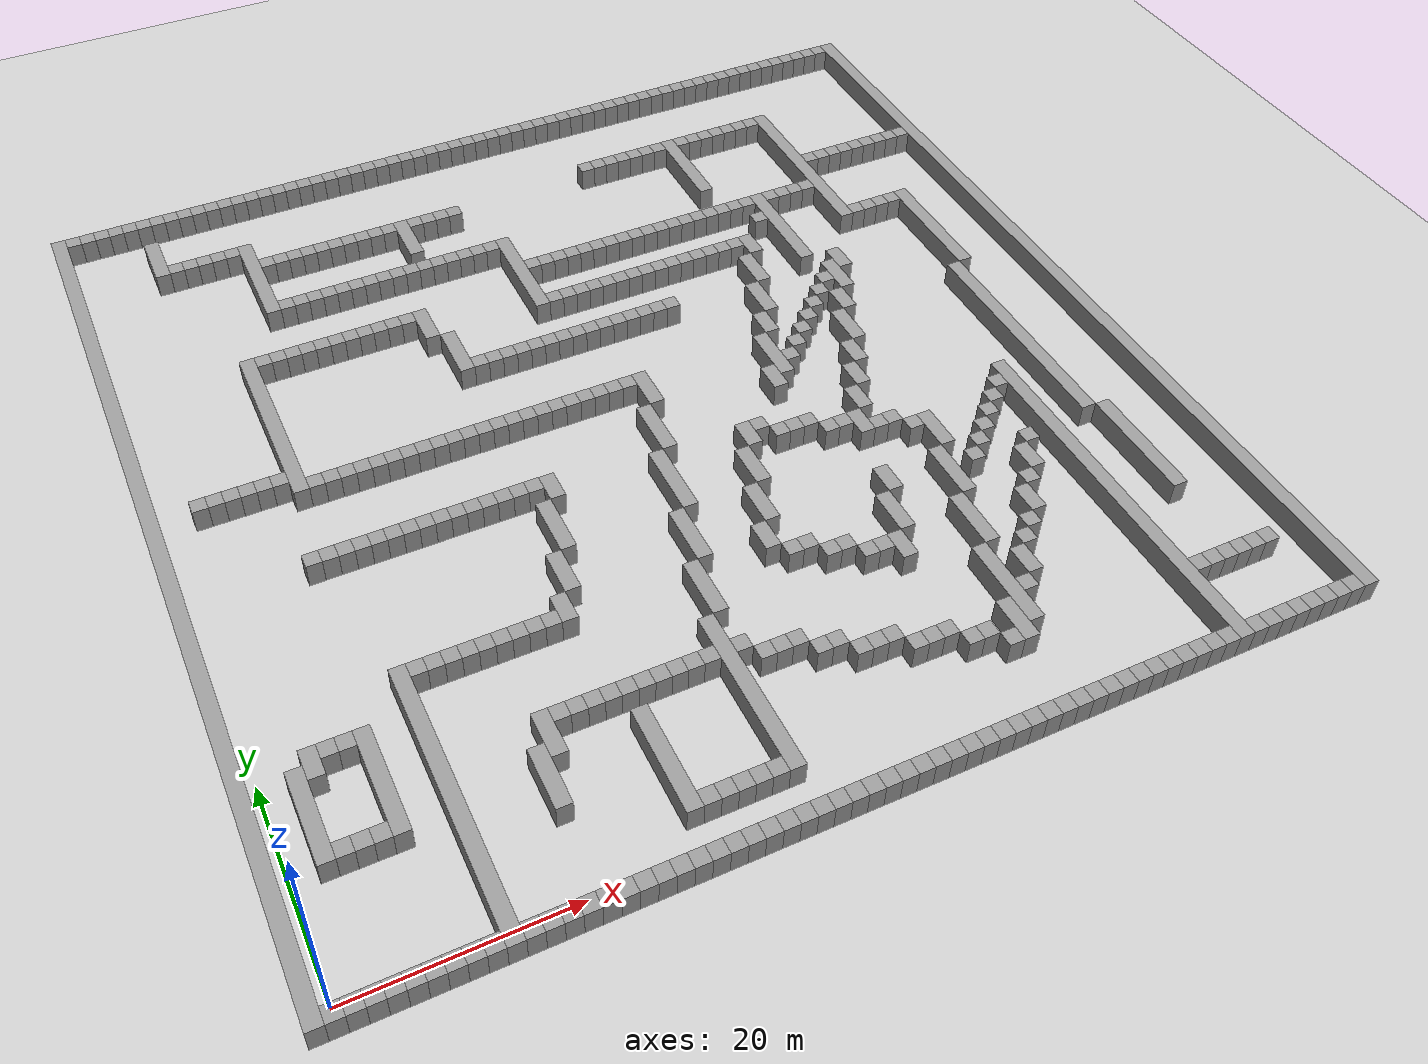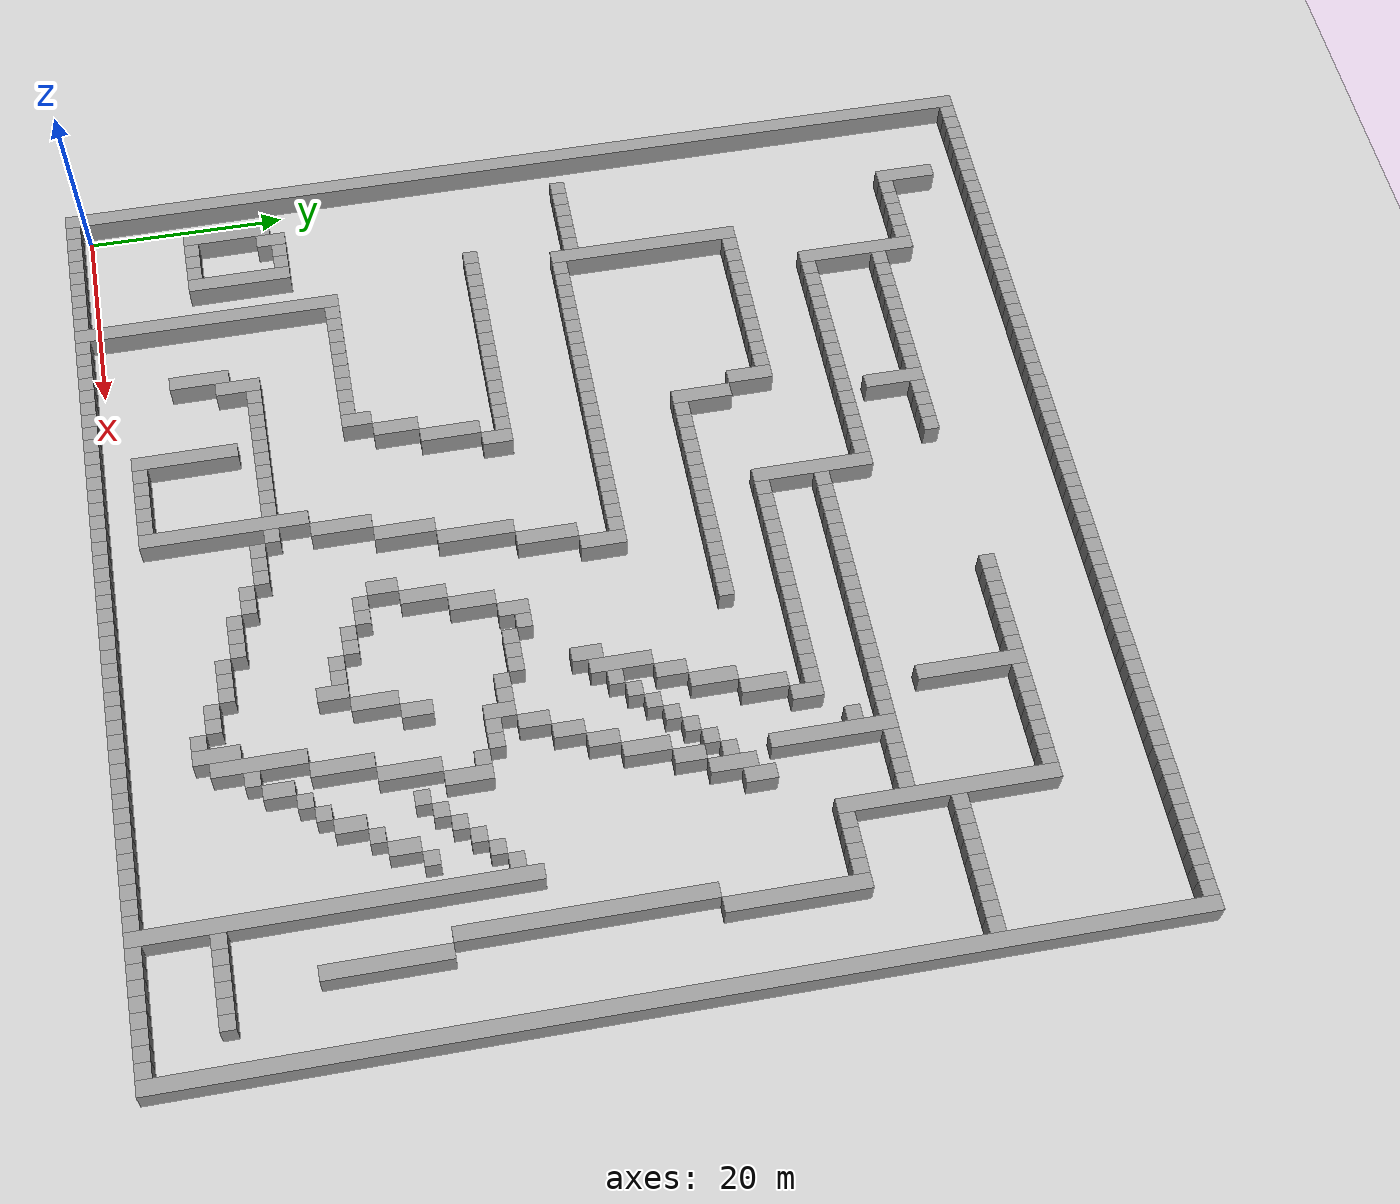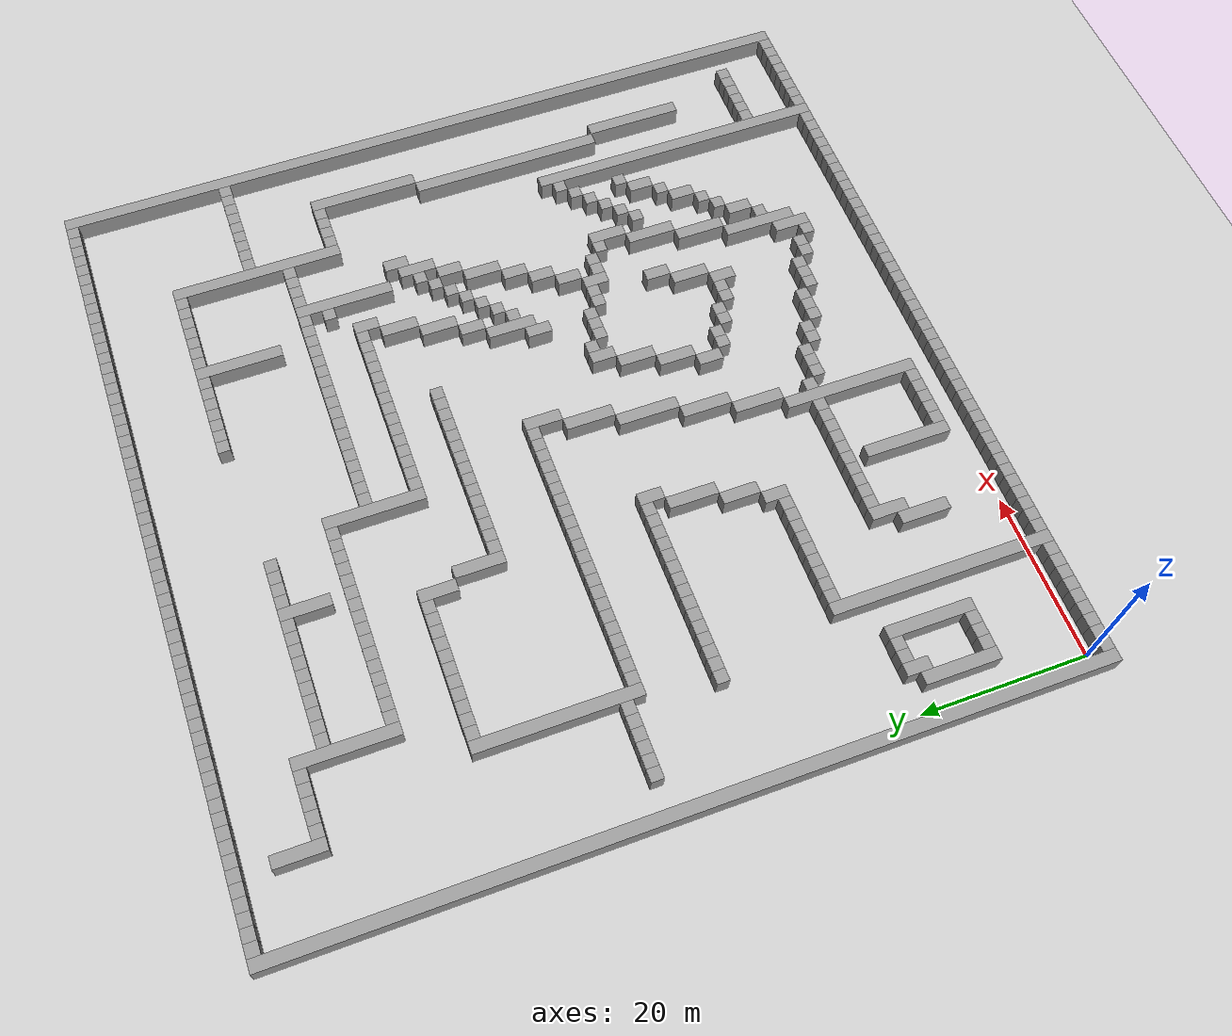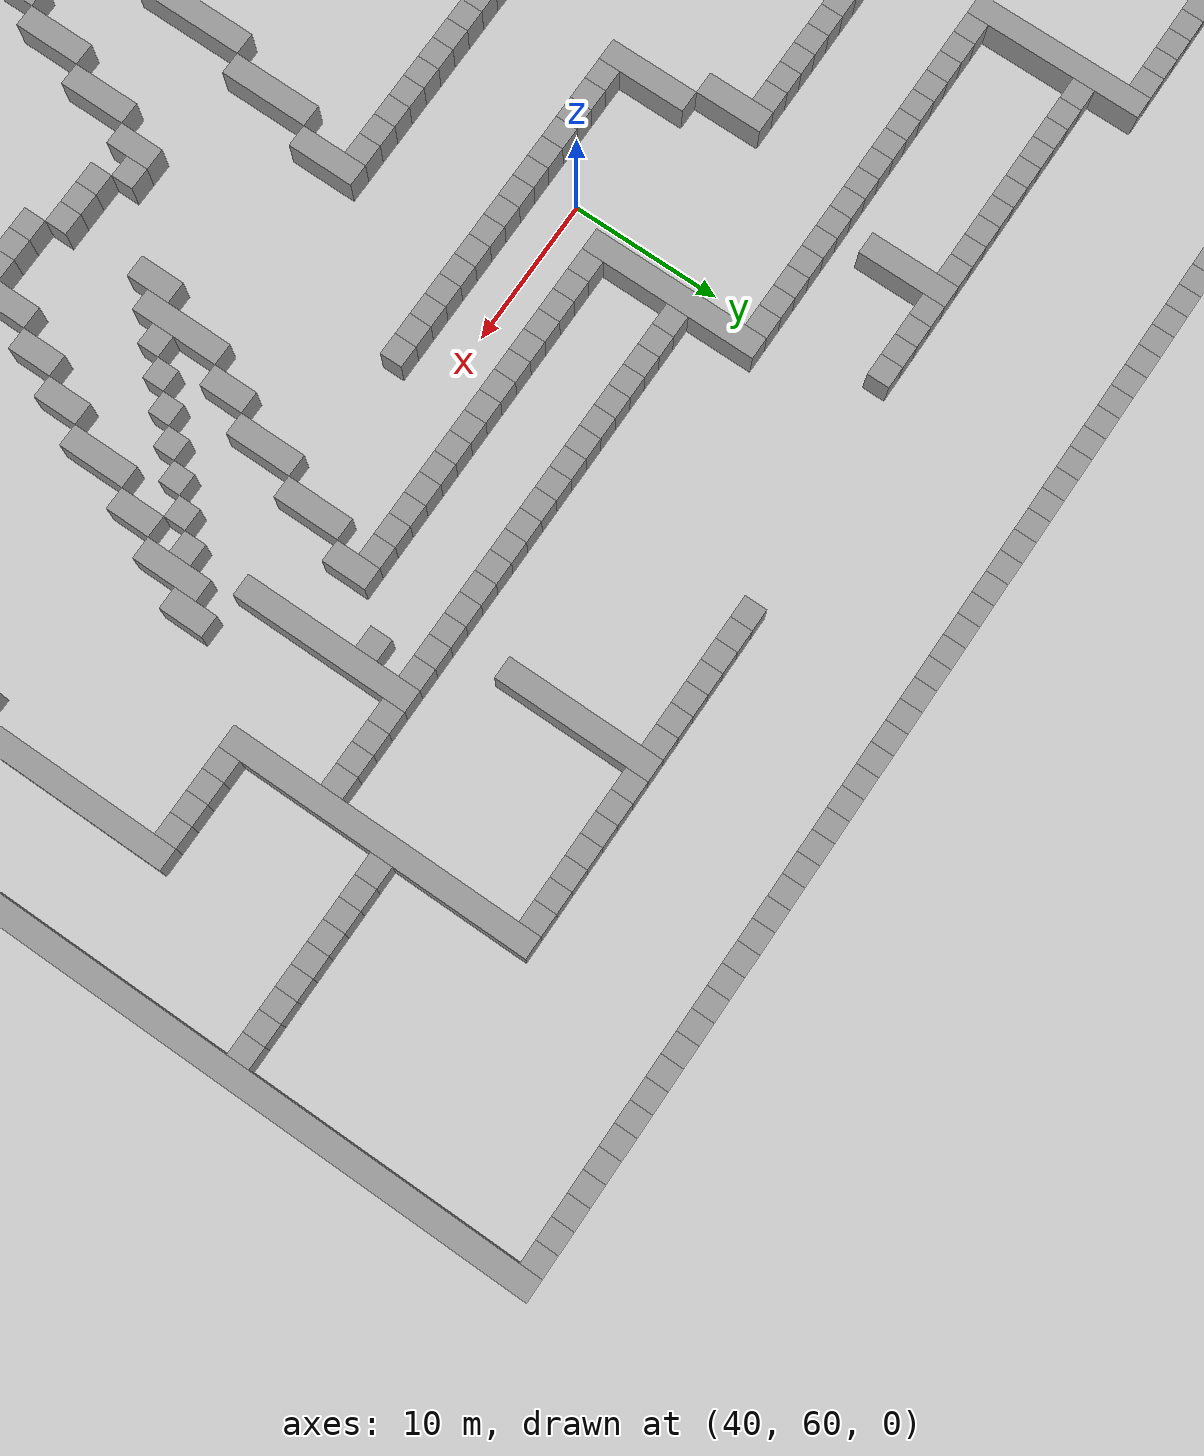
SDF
<?xml version='1.0'?>
        <sdf version='1.4'>
            <world name='1_wall'>
                <light name='sun' type='directional'>
                    <cast_shadows>1</cast_shadows>
                    <pose>0 0 10 0 -0 0</pose>
                    <diffuse>0.8 0.8 0.8 1</diffuse>
                    <specular>0.2 0.2 0.2 1</specular>
                    <attenuation>
                    <range>1000</range>
                    <constant>0.9</constant>
                    <linear>0.01</linear>
                    <quadratic>0.001</quadratic>
                    </attenuation>
                    <direction>-0.5 0.1 -0.9</direction>
                </light>
                <model name='ground_plane'>
                    <static>1</static>
                    <link name='link'>
                        <collision name='collision'>
                        <geometry>
                            <plane>
                                <normal>0 0 1</normal>
                                <size>1000 1000</size>
                            </plane>
                        </geometry>
                        <surface>
                            <friction>
                                <ode>
                                    <mu>100</mu>
                                    <mu2>50</mu2>
                                </ode>
                            </friction>
                            <bounce/>
                                <contact>
                                    <ode/>
                                </contact>
                        </surface>
                        <max_contacts>10</max_contacts>
                        </collision>
                    <visual name='visual'>
                        <cast_shadows>0</cast_shadows>
                        <geometry>
                            <plane>
                                <normal>0 0 1</normal>
                                <size>10000 10000</size>
                            </plane>
                            </geometry>
                                <material>
                                <script>
                                        <uri>file://media/materials/scripts/gazebo.material</uri>
                                        <name>Gazebo/Grey</name>
                                        </script>
                                    </material>
                    </visual>
                    <velocity_decay>
                        <linear>0</linear>
                        <angular>0</angular>
                    </velocity_decay>
                    <self_collide>0</self_collide>
                        <kinematic>0</kinematic>
                        <gravity>1</gravity>
                    </link>
                </model>
                <physics type='ode'>
                    <max_step_size>0.01</max_step_size>
                    <real_time_factor>1</real_time_factor>
                    <real_time_update_rate>100</real_time_update_rate>
                    <gravity>0 0 -9.8</gravity>
                </physics>
            <scene>
                <ambient>0.4 0.4 0.4 1</ambient>
                <background>0.7 0.7 0.7 1</background>
                <shadows>1</shadows>
            </scene>
    <model name='Wall_0'>
     <static>1</static>
    <link name='Wall_0'>
    <collision name='Wall_Collision_0'>
        <geometry>
          <box>
            <size>96.0 1.5 2.5</size>
          </box>
        </geometry>
        <pose>0 0 1.25 0 -0 0</pose>
      </collision>
      <visual name='Wall_Visual_0'>
        <pose>0 0 1.25 0 -0 0</pose>
        <geometry>
          <box>
            <size>96.0 1.5 2.5</size>
          </box>
        </geometry>
        <material>
          <script>
            <uri>file://media/materials/scripts/gazebo.material</uri>
            <name>Gazebo/Grey</name>
          </script>
        </material>
      </visual>
      <velocity_decay>
        <linear>0</linear>
        <angular>0</angular>
      </velocity_decay>
      <pose>-1.5 45.75 0 0 0 1.5707963267948966</pose>
    </link>
     </model><model name='Wall_1'>
     <static>1</static>
    <link name='Wall_1'>
    <collision name='Wall_Collision_1'>
        <geometry>
          <box>
            <size>1.5 1.5 2.5</size>
          </box>
        </geometry>
        <pose>0 0 1.25 0 -0 0</pose>
      </collision>
      <visual name='Wall_Visual_1'>
        <pose>0 0 1.25 0 -0 0</pose>
        <geometry>
          <box>
            <size>1.5 1.5 2.5</size>
          </box>
        </geometry>
        <material>
          <script>
            <uri>file://media/materials/scripts/gazebo.material</uri>
            <name>Gazebo/Grey</name>
          </script>
        </material>
      </visual>
      <velocity_decay>
        <linear>0</linear>
        <angular>0</angular>
      </velocity_decay>
      <pose>0.0 -1.5 0 0 0 1.5707963267948966</pose>
    </link>
     </model><model name='Wall_2'>
     <static>1</static>
    <link name='Wall_2'>
    <collision name='Wall_Collision_2'>
        <geometry>
          <box>
            <size>1.5 1.5 2.5</size>
          </box>
        </geometry>
        <pose>0 0 1.25 0 -0 0</pose>
      </collision>
      <visual name='Wall_Visual_2'>
        <pose>0 0 1.25 0 -0 0</pose>
        <geometry>
          <box>
            <size>1.5 1.5 2.5</size>
          </box>
        </geometry>
        <material>
          <script>
            <uri>file://media/materials/scripts/gazebo.material</uri>
            <name>Gazebo/Grey</name>
          </script>
        </material>
      </visual>
      <velocity_decay>
        <linear>0</linear>
        <angular>0</angular>
      </velocity_decay>
      <pose>0.0 93.0 0 0 0 1.5707963267948966</pose>
    </link>
     </model><model name='Wall_3'>
     <static>1</static>
    <link name='Wall_3'>
    <collision name='Wall_Collision_3'>
        <geometry>
          <box>
            <size>1.5 1.5 2.5</size>
          </box>
        </geometry>
        <pose>0 0 1.25 0 -0 0</pose>
      </collision>
      <visual name='Wall_Visual_3'>
        <pose>0 0 1.25 0 -0 0</pose>
        <geometry>
          <box>
            <size>1.5 1.5 2.5</size>
          </box>
        </geometry>
        <material>
          <script>
            <uri>file://media/materials/scripts/gazebo.material</uri>
            <name>Gazebo/Grey</name>
          </script>
        </material>
      </visual>
      <velocity_decay>
        <linear>0</linear>
        <angular>0</angular>
      </velocity_decay>
      <pose>1.5 -1.5 0 0 0 1.5707963267948966</pose>
    </link>
     </model><model name='Wall_4'>
     <static>1</static>
    <link name='Wall_4'>
    <collision name='Wall_Collision_4'>
        <geometry>
          <box>
            <size>1.5 1.5 2.5</size>
          </box>
        </geometry>
        <pose>0 0 1.25 0 -0 0</pose>
      </collision>
      <visual name='Wall_Visual_4'>
        <pose>0 0 1.25 0 -0 0</pose>
        <geometry>
          <box>
            <size>1.5 1.5 2.5</size>
          </box>
        </geometry>
        <material>
          <script>
            <uri>file://media/materials/scripts/gazebo.material</uri>
            <name>Gazebo/Grey</name>
          </script>
        </material>
      </visual>
      <velocity_decay>
        <linear>0</linear>
        <angular>0</angular>
      </velocity_decay>
      <pose>1.5 93.0 0 0 0 1.5707963267948966</pose>
    </link>
     </model><model name='Wall_5'>
     <static>1</static>
    <link name='Wall_5'>
    <collision name='Wall_Collision_5'>
        <geometry>
          <box>
            <size>1.5 1.5 2.5</size>
          </box>
        </geometry>
        <pose>0 0 1.25 0 -0 0</pose>
      </collision>
      <visual name='Wall_Visual_5'>
        <pose>0 0 1.25 0 -0 0</pose>
        <geometry>
          <box>
            <size>1.5 1.5 2.5</size>
          </box>
        </geometry>
        <material>
          <script>
            <uri>file://media/materials/scripts/gazebo.material</uri>
            <name>Gazebo/Grey</name>
          </script>
        </material>
      </visual>
      <velocity_decay>
        <linear>0</linear>
        <angular>0</angular>
      </velocity_decay>
      <pose>3.0 -1.5 0 0 0 1.5707963267948966</pose>
    </link>
     </model><model name='Wall_6'>
     <static>1</static>
    <link name='Wall_6'>
    <collision name='Wall_Collision_6'>
        <geometry>
          <box>
            <size>9.0 1.5 2.5</size>
          </box>
        </geometry>
        <pose>0 0 1.25 0 -0 0</pose>
      </collision>
      <visual name='Wall_Visual_6'>
        <pose>0 0 1.25 0 -0 0</pose>
        <geometry>
          <box>
            <size>9.0 1.5 2.5</size>
          </box>
        </geometry>
        <material>
          <script>
            <uri>file://media/materials/scripts/gazebo.material</uri>
            <name>Gazebo/Grey</name>
          </script>
        </material>
      </visual>
      <velocity_decay>
        <linear>0</linear>
        <angular>0</angular>
      </velocity_decay>
      <pose>3.0 14.25 0 0 0 1.5707963267948966</pose>
    </link>
     </model><model name='Wall_7'>
     <static>1</static>
    <link name='Wall_7'>
    <collision name='Wall_Collision_7'>
        <geometry>
          <box>
            <size>1.5 1.5 2.5</size>
          </box>
        </geometry>
        <pose>0 0 1.25 0 -0 0</pose>
      </collision>
      <visual name='Wall_Visual_7'>
        <pose>0 0 1.25 0 -0 0</pose>
        <geometry>
          <box>
            <size>1.5 1.5 2.5</size>
          </box>
        </geometry>
        <material>
          <script>
            <uri>file://media/materials/scripts/gazebo.material</uri>
            <name>Gazebo/Grey</name>
          </script>
        </material>
      </visual>
      <velocity_decay>
        <linear>0</linear>
        <angular>0</angular>
      </velocity_decay>
      <pose>3.0 49.5 0 0 0 1.5707963267948966</pose>
    </link>
     </model><model name='Wall_8'>
     <static>1</static>
    <link name='Wall_8'>
    <collision name='Wall_Collision_8'>
        <geometry>
          <box>
            <size>1.5 1.5 2.5</size>
          </box>
        </geometry>
        <pose>0 0 1.25 0 -0 0</pose>
      </collision>
      <visual name='Wall_Visual_8'>
        <pose>0 0 1.25 0 -0 0</pose>
        <geometry>
          <box>
            <size>1.5 1.5 2.5</size>
          </box>
        </geometry>
        <material>
          <script>
            <uri>file://media/materials/scripts/gazebo.material</uri>
            <name>Gazebo/Grey</name>
          </script>
        </material>
      </visual>
      <velocity_decay>
        <linear>0</linear>
        <angular>0</angular>
      </velocity_decay>
      <pose>3.0 93.0 0 0 0 1.5707963267948966</pose>
    </link>
     </model><model name='Wall_9'>
     <static>1</static>
    <link name='Wall_9'>
    <collision name='Wall_Collision_9'>
        <geometry>
          <box>
            <size>1.5 1.5 2.5</size>
          </box>
        </geometry>
        <pose>0 0 1.25 0 -0 0</pose>
      </collision>
      <visual name='Wall_Visual_9'>
        <pose>0 0 1.25 0 -0 0</pose>
        <geometry>
          <box>
            <size>1.5 1.5 2.5</size>
          </box>
        </geometry>
        <material>
          <script>
            <uri>file://media/materials/scripts/gazebo.material</uri>
            <name>Gazebo/Grey</name>
          </script>
        </material>
      </visual>
      <velocity_decay>
        <linear>0</linear>
        <angular>0</angular>
      </velocity_decay>
      <pose>4.5 -1.5 0 0 0 1.5707963267948966</pose>
    </link>
     </model><model name='Wall_10'>
     <static>1</static>
    <link name='Wall_10'>
    <collision name='Wall_Collision_10'>
        <geometry>
          <box>
            <size>1.5 1.5 2.5</size>
          </box>
        </geometry>
        <pose>0 0 1.25 0 -0 0</pose>
      </collision>
      <visual name='Wall_Visual_10'>
        <pose>0 0 1.25 0 -0 0</pose>
        <geometry>
          <box>
            <size>1.5 1.5 2.5</size>
          </box>
        </geometry>
        <material>
          <script>
            <uri>file://media/materials/scripts/gazebo.material</uri>
            <name>Gazebo/Grey</name>
          </script>
        </material>
      </visual>
      <velocity_decay>
        <linear>0</linear>
        <angular>0</angular>
      </velocity_decay>
      <pose>4.5 10.5 0 0 0 1.5707963267948966</pose>
    </link>
     </model><model name='Wall_11'>
     <static>1</static>
    <link name='Wall_11'>
    <collision name='Wall_Collision_11'>
        <geometry>
          <box>
            <size>3.0 1.5 2.5</size>
          </box>
        </geometry>
        <pose>0 0 1.25 0 -0 0</pose>
      </collision>
      <visual name='Wall_Visual_11'>
        <pose>0 0 1.25 0 -0 0</pose>
        <geometry>
          <box>
            <size>3.0 1.5 2.5</size>
          </box>
        </geometry>
        <material>
          <script>
            <uri>file://media/materials/scripts/gazebo.material</uri>
            <name>Gazebo/Grey</name>
          </script>
        </material>
      </visual>
      <velocity_decay>
        <linear>0</linear>
        <angular>0</angular>
      </velocity_decay>
      <pose>4.5 18.75 0 0 0 1.5707963267948966</pose>
    </link>
     </model><model name='Wall_12'>
     <static>1</static>
    <link name='Wall_12'>
    <collision name='Wall_Collision_12'>
        <geometry>
          <box>
            <size>1.5 1.5 2.5</size>
          </box>
        </geometry>
        <pose>0 0 1.25 0 -0 0</pose>
      </collision>
      <visual name='Wall_Visual_12'>
        <pose>0 0 1.25 0 -0 0</pose>
        <geometry>
          <box>
            <size>1.5 1.5 2.5</size>
          </box>
        </geometry>
        <material>
          <script>
            <uri>file://media/materials/scripts/gazebo.material</uri>
            <name>Gazebo/Grey</name>
          </script>
        </material>
      </visual>
      <velocity_decay>
        <linear>0</linear>
        <angular>0</angular>
      </velocity_decay>
      <pose>4.5 49.5 0 0 0 1.5707963267948966</pose>
    </link>
     </model><model name='Wall_13'>
     <static>1</static>
    <link name='Wall_13'>
    <collision name='Wall_Collision_13'>
        <geometry>
          <box>
            <size>1.5 1.5 2.5</size>
          </box>
        </geometry>
        <pose>0 0 1.25 0 -0 0</pose>
      </collision>
      <visual name='Wall_Visual_13'>
        <pose>0 0 1.25 0 -0 0</pose>
        <geometry>
          <box>
            <size>1.5 1.5 2.5</size>
          </box>
        </geometry>
        <material>
          <script>
            <uri>file://media/materials/scripts/gazebo.material</uri>
            <name>Gazebo/Grey</name>
          </script>
        </material>
      </visual>
      <velocity_decay>
        <linear>0</linear>
        <angular>0</angular>
      </velocity_decay>
      <pose>4.5 93.0 0 0 0 1.5707963267948966</pose>
    </link>
     </model><model name='Wall_14'>
     <static>1</static>
    <link name='Wall_14'>
    <collision name='Wall_Collision_14'>
        <geometry>
          <box>
            <size>1.5 1.5 2.5</size>
          </box>
        </geometry>
        <pose>0 0 1.25 0 -0 0</pose>
      </collision>
      <visual name='Wall_Visual_14'>
        <pose>0 0 1.25 0 -0 0</pose>
        <geometry>
          <box>
            <size>1.5 1.5 2.5</size>
          </box>
        </geometry>
        <material>
          <script>
            <uri>file://media/materials/scripts/gazebo.material</uri>
            <name>Gazebo/Grey</name>
          </script>
        </material>
      </visual>
      <velocity_decay>
        <linear>0</linear>
        <angular>0</angular>
      </velocity_decay>
      <pose>6.0 -1.5 0 0 0 1.5707963267948966</pose>
    </link>
     </model><model name='Wall_15'>
     <static>1</static>
    <link name='Wall_15'>
    <collision name='Wall_Collision_15'>
        <geometry>
          <box>
            <size>1.5 1.5 2.5</size>
          </box>
        </geometry>
        <pose>0 0 1.25 0 -0 0</pose>
      </collision>
      <visual name='Wall_Visual_15'>
        <pose>0 0 1.25 0 -0 0</pose>
        <geometry>
          <box>
            <size>1.5 1.5 2.5</size>
          </box>
        </geometry>
        <material>
          <script>
            <uri>file://media/materials/scripts/gazebo.material</uri>
            <name>Gazebo/Grey</name>
          </script>
        </material>
      </visual>
      <velocity_decay>
        <linear>0</linear>
        <angular>0</angular>
      </velocity_decay>
      <pose>6.0 10.5 0 0 0 1.5707963267948966</pose>
    </link>
     </model><model name='Wall_16'>
     <static>1</static>
    <link name='Wall_16'>
    <collision name='Wall_Collision_16'>
        <geometry>
          <box>
            <size>1.5 1.5 2.5</size>
          </box>
        </geometry>
        <pose>0 0 1.25 0 -0 0</pose>
      </collision>
      <visual name='Wall_Visual_16'>
        <pose>0 0 1.25 0 -0 0</pose>
        <geometry>
          <box>
            <size>1.5 1.5 2.5</size>
          </box>
        </geometry>
        <material>
          <script>
            <uri>file://media/materials/scripts/gazebo.material</uri>
            <name>Gazebo/Grey</name>
          </script>
        </material>
      </visual>
      <velocity_decay>
        <linear>0</linear>
        <angular>0</angular>
      </velocity_decay>
      <pose>6.0 19.5 0 0 0 1.5707963267948966</pose>
    </link>
     </model><model name='Wall_17'>
     <static>1</static>
    <link name='Wall_17'>
    <collision name='Wall_Collision_17'>
        <geometry>
          <box>
            <size>1.5 1.5 2.5</size>
          </box>
        </geometry>
        <pose>0 0 1.25 0 -0 0</pose>
      </collision>
      <visual name='Wall_Visual_17'>
        <pose>0 0 1.25 0 -0 0</pose>
        <geometry>
          <box>
            <size>1.5 1.5 2.5</size>
          </box>
        </geometry>
        <material>
          <script>
            <uri>file://media/materials/scripts/gazebo.material</uri>
            <name>Gazebo/Grey</name>
          </script>
        </material>
      </visual>
      <velocity_decay>
        <linear>0</linear>
        <angular>0</angular>
      </velocity_decay>
      <pose>6.0 49.5 0 0 0 1.5707963267948966</pose>
    </link>
     </model><model name='Wall_18'>
     <static>1</static>
    <link name='Wall_18'>
    <collision name='Wall_Collision_18'>
        <geometry>
          <box>
            <size>1.5 1.5 2.5</size>
          </box>
        </geometry>
        <pose>0 0 1.25 0 -0 0</pose>
      </collision>
      <visual name='Wall_Visual_18'>
        <pose>0 0 1.25 0 -0 0</pose>
        <geometry>
          <box>
            <size>1.5 1.5 2.5</size>
          </box>
        </geometry>
        <material>
          <script>
            <uri>file://media/materials/scripts/gazebo.material</uri>
            <name>Gazebo/Grey</name>
          </script>
        </material>
      </visual>
      <velocity_decay>
        <linear>0</linear>
        <angular>0</angular>
      </velocity_decay>
      <pose>6.0 93.0 0 0 0 1.5707963267948966</pose>
    </link>
     </model><model name='Wall_19'>
     <static>1</static>
    <link name='Wall_19'>
    <collision name='Wall_Collision_19'>
        <geometry>
          <box>
            <size>1.5 1.5 2.5</size>
          </box>
        </geometry>
        <pose>0 0 1.25 0 -0 0</pose>
      </collision>
      <visual name='Wall_Visual_19'>
        <pose>0 0 1.25 0 -0 0</pose>
        <geometry>
          <box>
            <size>1.5 1.5 2.5</size>
          </box>
        </geometry>
        <material>
          <script>
            <uri>file://media/materials/scripts/gazebo.material</uri>
            <name>Gazebo/Grey</name>
          </script>
        </material>
      </visual>
      <velocity_decay>
        <linear>0</linear>
        <angular>0</angular>
      </velocity_decay>
      <pose>7.5 -1.5 0 0 0 1.5707963267948966</pose>
    </link>
     </model><model name='Wall_20'>
     <static>1</static>
    <link name='Wall_20'>
    <collision name='Wall_Collision_20'>
        <geometry>
          <box>
            <size>1.5 1.5 2.5</size>
          </box>
        </geometry>
        <pose>0 0 1.25 0 -0 0</pose>
      </collision>
      <visual name='Wall_Visual_20'>
        <pose>0 0 1.25 0 -0 0</pose>
        <geometry>
          <box>
            <size>1.5 1.5 2.5</size>
          </box>
        </geometry>
        <material>
          <script>
            <uri>file://media/materials/scripts/gazebo.material</uri>
            <name>Gazebo/Grey</name>
          </script>
        </material>
      </visual>
      <velocity_decay>
        <linear>0</linear>
        <angular>0</angular>
      </velocity_decay>
      <pose>7.5 10.5 0 0 0 1.5707963267948966</pose>
    </link>
     </model><model name='Wall_21'>
     <static>1</static>
    <link name='Wall_21'>
    <collision name='Wall_Collision_21'>
        <geometry>
          <box>
            <size>1.5 1.5 2.5</size>
          </box>
        </geometry>
        <pose>0 0 1.25 0 -0 0</pose>
      </collision>
      <visual name='Wall_Visual_21'>
        <pose>0 0 1.25 0 -0 0</pose>
        <geometry>
          <box>
            <size>1.5 1.5 2.5</size>
          </box>
        </geometry>
        <material>
          <script>
            <uri>file://media/materials/scripts/gazebo.material</uri>
            <name>Gazebo/Grey</name>
          </script>
        </material>
      </visual>
      <velocity_decay>
        <linear>0</linear>
        <angular>0</angular>
      </velocity_decay>
      <pose>7.5 19.5 0 0 0 1.5707963267948966</pose>
    </link>
     </model><model name='Wall_22'>
     <static>1</static>
    <link name='Wall_22'>
    <collision name='Wall_Collision_22'>
        <geometry>
          <box>
            <size>1.5 1.5 2.5</size>
          </box>
        </geometry>
        <pose>0 0 1.25 0 -0 0</pose>
      </collision>
      <visual name='Wall_Visual_22'>
        <pose>0 0 1.25 0 -0 0</pose>
        <geometry>
          <box>
            <size>1.5 1.5 2.5</size>
          </box>
        </geometry>
        <material>
          <script>
            <uri>file://media/materials/scripts/gazebo.material</uri>
            <name>Gazebo/Grey</name>
          </script>
        </material>
      </visual>
      <velocity_decay>
        <linear>0</linear>
        <angular>0</angular>
      </velocity_decay>
      <pose>7.5 49.5 0 0 0 1.5707963267948966</pose>
    </link>
     </model><model name='Wall_23'>
     <static>1</static>
    <link name='Wall_23'>
    <collision name='Wall_Collision_23'>
        <geometry>
          <box>
            <size>6.0 1.5 2.5</size>
          </box>
        </geometry>
        <pose>0 0 1.25 0 -0 0</pose>
      </collision>
      <visual name='Wall_Visual_23'>
        <pose>0 0 1.25 0 -0 0</pose>
        <geometry>
          <box>
            <size>6.0 1.5 2.5</size>
          </box>
        </geometry>
        <material>
          <script>
            <uri>file://media/materials/scripts/gazebo.material</uri>
            <name>Gazebo/Grey</name>
          </script>
        </material>
      </visual>
      <velocity_decay>
        <linear>0</linear>
        <angular>0</angular>
      </velocity_decay>
      <pose>7.5 86.25 0 0 0 1.5707963267948966</pose>
    </link>
     </model><model name='Wall_24'>
     <static>1</static>
    <link name='Wall_24'>
    <collision name='Wall_Collision_24'>
        <geometry>
          <box>
            <size>1.5 1.5 2.5</size>
          </box>
        </geometry>
        <pose>0 0 1.25 0 -0 0</pose>
      </collision>
      <visual name='Wall_Visual_24'>
        <pose>0 0 1.25 0 -0 0</pose>
        <geometry>
          <box>
            <size>1.5 1.5 2.5</size>
          </box>
        </geometry>
        <material>
          <script>
            <uri>file://media/materials/scripts/gazebo.material</uri>
            <name>Gazebo/Grey</name>
          </script>
        </material>
      </visual>
      <velocity_decay>
        <linear>0</linear>
        <angular>0</angular>
      </velocity_decay>
      <pose>7.5 93.0 0 0 0 1.5707963267948966</pose>
    </link>
     </model><model name='Wall_25'>
     <static>1</static>
    <link name='Wall_25'>
    <collision name='Wall_Collision_25'>
        <geometry>
          <box>
            <size>1.5 1.5 2.5</size>
          </box>
        </geometry>
        <pose>0 0 1.25 0 -0 0</pose>
      </collision>
      <visual name='Wall_Visual_25'>
        <pose>0 0 1.25 0 -0 0</pose>
        <geometry>
          <box>
            <size>1.5 1.5 2.5</size>
          </box>
        </geometry>
        <material>
          <script>
            <uri>file://media/materials/scripts/gazebo.material</uri>
            <name>Gazebo/Grey</name>
          </script>
        </material>
      </visual>
      <velocity_decay>
        <linear>0</linear>
        <angular>0</angular>
      </velocity_decay>
      <pose>9.0 -1.5 0 0 0 1.5707963267948966</pose>
    </link>
     </model><model name='Wall_26'>
     <static>1</static>
    <link name='Wall_26'>
    <collision name='Wall_Collision_26'>
        <geometry>
          <box>
            <size>10.5 1.5 2.5</size>
          </box>
        </geometry>
        <pose>0 0 1.25 0 -0 0</pose>
      </collision>
      <visual name='Wall_Visual_26'>
        <pose>0 0 1.25 0 -0 0</pose>
        <geometry>
          <box>
            <size>10.5 1.5 2.5</size>
          </box>
        </geometry>
        <material>
          <script>
            <uri>file://media/materials/scripts/gazebo.material</uri>
            <name>Gazebo/Grey</name>
          </script>
        </material>
      </visual>
      <velocity_decay>
        <linear>0</linear>
        <angular>0</angular>
      </velocity_decay>
      <pose>9.0 15.0 0 0 0 1.5707963267948966</pose>
    </link>
     </model><model name='Wall_27'>
     <static>1</static>
    <link name='Wall_27'>
    <collision name='Wall_Collision_27'>
        <geometry>
          <box>
            <size>1.5 1.5 2.5</size>
          </box>
        </geometry>
        <pose>0 0 1.25 0 -0 0</pose>
      </collision>
      <visual name='Wall_Visual_27'>
        <pose>0 0 1.25 0 -0 0</pose>
        <geometry>
          <box>
            <size>1.5 1.5 2.5</size>
          </box>
        </geometry>
        <material>
          <script>
            <uri>file://media/materials/scripts/gazebo.material</uri>
            <name>Gazebo/Grey</name>
          </script>
        </material>
      </visual>
      <velocity_decay>
        <linear>0</linear>
        <angular>0</angular>
      </velocity_decay>
      <pose>9.0 49.5 0 0 0 1.5707963267948966</pose>
    </link>
     </model><model name='Wall_28'>
     <static>1</static>
    <link name='Wall_28'>
    <collision name='Wall_Collision_28'>
        <geometry>
          <box>
            <size>1.5 1.5 2.5</size>
          </box>
        </geometry>
        <pose>0 0 1.25 0 -0 0</pose>
      </collision>
      <visual name='Wall_Visual_28'>
        <pose>0 0 1.25 0 -0 0</pose>
        <geometry>
          <box>
            <size>1.5 1.5 2.5</size>
          </box>
        </geometry>
        <material>
          <script>
            <uri>file://media/materials/scripts/gazebo.material</uri>
            <name>Gazebo/Grey</name>
          </script>
        </material>
      </visual>
      <velocity_decay>
        <linear>0</linear>
        <angular>0</angular>
      </velocity_decay>
      <pose>9.0 84.0 0 0 0 1.5707963267948966</pose>
    </link>
     </model><model name='Wall_29'>
     <static>1</static>
    <link name='Wall_29'>
    <collision name='Wall_Collision_29'>
        <geometry>
          <box>
            <size>1.5 1.5 2.5</size>
          </box>
        </geometry>
        <pose>0 0 1.25 0 -0 0</pose>
      </collision>
      <visual name='Wall_Visual_29'>
        <pose>0 0 1.25 0 -0 0</pose>
        <geometry>
          <box>
            <size>1.5 1.5 2.5</size>
          </box>
        </geometry>
        <material>
          <script>
            <uri>file://media/materials/scripts/gazebo.material</uri>
            <name>Gazebo/Grey</name>
          </script>
        </material>
      </visual>
      <velocity_decay>
        <linear>0</linear>
        <angular>0</angular>
      </velocity_decay>
      <pose>9.0 93.0 0 0 0 1.5707963267948966</pose>
    </link>
     </model><model name='Wall_30'>
     <static>1</static>
    <link name='Wall_30'>
    <collision name='Wall_Collision_30'>
        <geometry>
          <box>
            <size>1.5 1.5 2.5</size>
          </box>
        </geometry>
        <pose>0 0 1.25 0 -0 0</pose>
      </collision>
      <visual name='Wall_Visual_30'>
        <pose>0 0 1.25 0 -0 0</pose>
        <geometry>
          <box>
            <size>1.5 1.5 2.5</size>
          </box>
        </geometry>
        <material>
          <script>
            <uri>file://media/materials/scripts/gazebo.material</uri>
            <name>Gazebo/Grey</name>
          </script>
        </material>
      </visual>
      <velocity_decay>
        <linear>0</linear>
        <angular>0</angular>
      </velocity_decay>
      <pose>10.5 -1.5 0 0 0 1.5707963267948966</pose>
    </link>
     </model><model name='Wall_31'>
     <static>1</static>
    <link name='Wall_31'>
    <collision name='Wall_Collision_31'>
        <geometry>
          <box>
            <size>1.5 1.5 2.5</size>
          </box>
        </geometry>
        <pose>0 0 1.25 0 -0 0</pose>
      </collision>
      <visual name='Wall_Visual_31'>
        <pose>0 0 1.25 0 -0 0</pose>
        <geometry>
          <box>
            <size>1.5 1.5 2.5</size>
          </box>
        </geometry>
        <material>
          <script>
            <uri>file://media/materials/scripts/gazebo.material</uri>
            <name>Gazebo/Grey</name>
          </script>
        </material>
      </visual>
      <velocity_decay>
        <linear>0</linear>
        <angular>0</angular>
      </velocity_decay>
      <pose>10.5 39.0 0 0 0 1.5707963267948966</pose>
    </link>
     </model><model name='Wall_32'>
     <static>1</static>
    <link name='Wall_32'>
    <collision name='Wall_Collision_32'>
        <geometry>
          <box>
            <size>1.5 1.5 2.5</size>
          </box>
        </geometry>
        <pose>0 0 1.25 0 -0 0</pose>
      </collision>
      <visual name='Wall_Visual_32'>
        <pose>0 0 1.25 0 -0 0</pose>
        <geometry>
          <box>
            <size>1.5 1.5 2.5</size>
          </box>
        </geometry>
        <material>
          <script>
            <uri>file://media/materials/scripts/gazebo.material</uri>
            <name>Gazebo/Grey</name>
          </script>
        </material>
      </visual>
      <velocity_decay>
        <linear>0</linear>
        <angular>0</angular>
      </velocity_decay>
      <pose>10.5 49.5 0 0 0 1.5707963267948966</pose>
    </link>
     </model><model name='Wall_33'>
     <static>1</static>
    <link name='Wall_33'>
    <collision name='Wall_Collision_33'>
        <geometry>
          <box>
            <size>1.5 1.5 2.5</size>
          </box>
        </geometry>
        <pose>0 0 1.25 0 -0 0</pose>
      </collision>
      <visual name='Wall_Visual_33'>
        <pose>0 0 1.25 0 -0 0</pose>
        <geometry>
          <box>
            <size>1.5 1.5 2.5</size>
          </box>
        </geometry>
        <material>
          <script>
            <uri>file://media/materials/scripts/gazebo.material</uri>
            <name>Gazebo/Grey</name>
          </script>
        </material>
      </visual>
      <velocity_decay>
        <linear>0</linear>
        <angular>0</angular>
      </velocity_decay>
      <pose>10.5 84.0 0 0 0 1.5707963267948966</pose>
    </link>
     </model><model name='Wall_34'>
     <static>1</static>
    <link name='Wall_34'>
    <collision name='Wall_Collision_34'>
        <geometry>
          <box>
            <size>1.5 1.5 2.5</size>
          </box>
        </geometry>
        <pose>0 0 1.25 0 -0 0</pose>
      </collision>
      <visual name='Wall_Visual_34'>
        <pose>0 0 1.25 0 -0 0</pose>
        <geometry>
          <box>
            <size>1.5 1.5 2.5</size>
          </box>
        </geometry>
        <material>
          <script>
            <uri>file://media/materials/scripts/gazebo.material</uri>
            <name>Gazebo/Grey</name>
          </script>
        </material>
      </visual>
      <velocity_decay>
        <linear>0</linear>
        <angular>0</angular>
      </velocity_decay>
      <pose>10.5 93.0 0 0 0 1.5707963267948966</pose>
    </link>
     </model><model name='Wall_35'>
     <static>1</static>
    <link name='Wall_35'>
    <collision name='Wall_Collision_35'>
        <geometry>
          <box>
            <size>1.5 1.5 2.5</size>
          </box>
        </geometry>
        <pose>0 0 1.25 0 -0 0</pose>
      </collision>
      <visual name='Wall_Visual_35'>
        <pose>0 0 1.25 0 -0 0</pose>
        <geometry>
          <box>
            <size>1.5 1.5 2.5</size>
          </box>
        </geometry>
        <material>
          <script>
            <uri>file://media/materials/scripts/gazebo.material</uri>
            <name>Gazebo/Grey</name>
          </script>
        </material>
      </visual>
      <velocity_decay>
        <linear>0</linear>
        <angular>0</angular>
      </velocity_decay>
      <pose>12.0 -1.5 0 0 0 1.5707963267948966</pose>
    </link>
     </model><model name='Wall_36'>
     <static>1</static>
    <link name='Wall_36'>
    <collision name='Wall_Collision_36'>
        <geometry>
          <box>
            <size>1.5 1.5 2.5</size>
          </box>
        </geometry>
        <pose>0 0 1.25 0 -0 0</pose>
      </collision>
      <visual name='Wall_Visual_36'>
        <pose>0 0 1.25 0 -0 0</pose>
        <geometry>
          <box>
            <size>1.5 1.5 2.5</size>
          </box>
        </geometry>
        <material>
          <script>
            <uri>file://media/materials/scripts/gazebo.material</uri>
            <name>Gazebo/Grey</name>
          </script>
        </material>
      </visual>
      <velocity_decay>
        <linear>0</linear>
        <angular>0</angular>
      </velocity_decay>
      <pose>12.0 39.0 0 0 0 1.5707963267948966</pose>
    </link>
     </model><model name='Wall_37'>
     <static>1</static>
    <link name='Wall_37'>
    <collision name='Wall_Collision_37'>
        <geometry>
          <box>
            <size>19.5 1.5 2.5</size>
          </box>
        </geometry>
        <pose>0 0 1.25 0 -0 0</pose>
      </collision>
      <visual name='Wall_Visual_37'>
        <pose>0 0 1.25 0 -0 0</pose>
        <geometry>
          <box>
            <size>19.5 1.5 2.5</size>
          </box>
        </geometry>
        <material>
          <script>
            <uri>file://media/materials/scripts/gazebo.material</uri>
            <name>Gazebo/Grey</name>
          </script>
        </material>
      </visual>
      <velocity_decay>
        <linear>0</linear>
        <angular>0</angular>
      </velocity_decay>
      <pose>12.0 57.0 0 0 0 1.5707963267948966</pose>
    </link>
     </model><model name='Wall_38'>
     <static>1</static>
    <link name='Wall_38'>
    <collision name='Wall_Collision_38'>
        <geometry>
          <box>
            <size>1.5 1.5 2.5</size>
          </box>
        </geometry>
        <pose>0 0 1.25 0 -0 0</pose>
      </collision>
      <visual name='Wall_Visual_38'>
        <pose>0 0 1.25 0 -0 0</pose>
        <geometry>
          <box>
            <size>1.5 1.5 2.5</size>
          </box>
        </geometry>
        <material>
          <script>
            <uri>file://media/materials/scripts/gazebo.material</uri>
            <name>Gazebo/Grey</name>
          </script>
        </material>
      </visual>
      <velocity_decay>
        <linear>0</linear>
        <angular>0</angular>
      </velocity_decay>
      <pose>12.0 84.0 0 0 0 1.5707963267948966</pose>
    </link>
     </model><model name='Wall_39'>
     <static>1</static>
    <link name='Wall_39'>
    <collision name='Wall_Collision_39'>
        <geometry>
          <box>
            <size>1.5 1.5 2.5</size>
          </box>
        </geometry>
        <pose>0 0 1.25 0 -0 0</pose>
      </collision>
      <visual name='Wall_Visual_39'>
        <pose>0 0 1.25 0 -0 0</pose>
        <geometry>
          <box>
            <size>1.5 1.5 2.5</size>
          </box>
        </geometry>
        <material>
          <script>
            <uri>file://media/materials/scripts/gazebo.material</uri>
            <name>Gazebo/Grey</name>
          </script>
        </material>
      </visual>
      <velocity_decay>
        <linear>0</linear>
        <angular>0</angular>
      </velocity_decay>
      <pose>12.0 93.0 0 0 0 1.5707963267948966</pose>
    </link>
     </model><model name='Wall_40'>
     <static>1</static>
    <link name='Wall_40'>
    <collision name='Wall_Collision_40'>
        <geometry>
          <box>
            <size>27.0 1.5 2.5</size>
          </box>
        </geometry>
        <pose>0 0 1.25 0 -0 0</pose>
      </collision>
      <visual name='Wall_Visual_40'>
        <pose>0 0 1.25 0 -0 0</pose>
        <geometry>
          <box>
            <size>27.0 1.5 2.5</size>
          </box>
        </geometry>
        <material>
          <script>
            <uri>file://media/materials/scripts/gazebo.material</uri>
            <name>Gazebo/Grey</name>
          </script>
        </material>
      </visual>
      <velocity_decay>
        <linear>0</linear>
        <angular>0</angular>
      </velocity_decay>
      <pose>13.5 11.25 0 0 0 1.5707963267948966</pose>
    </link>
     </model><model name='Wall_41'>
     <static>1</static>
    <link name='Wall_41'>
    <collision name='Wall_Collision_41'>
        <geometry>
          <box>
            <size>1.5 1.5 2.5</size>
          </box>
        </geometry>
        <pose>0 0 1.25 0 -0 0</pose>
      </collision>
      <visual name='Wall_Visual_41'>
        <pose>0 0 1.25 0 -0 0</pose>
        <geometry>
          <box>
            <size>1.5 1.5 2.5</size>
          </box>
        </geometry>
        <material>
          <script>
            <uri>file://media/materials/scripts/gazebo.material</uri>
            <name>Gazebo/Grey</name>
          </script>
        </material>
      </visual>
      <velocity_decay>
        <linear>0</linear>
        <angular>0</angular>
      </velocity_decay>
      <pose>13.5 39.0 0 0 0 1.5707963267948966</pose>
    </link>
     </model><model name='Wall_42'>
     <static>1</static>
    <link name='Wall_42'>
    <collision name='Wall_Collision_42'>
        <geometry>
          <box>
            <size>1.5 1.5 2.5</size>
          </box>
        </geometry>
        <pose>0 0 1.25 0 -0 0</pose>
      </collision>
      <visual name='Wall_Visual_42'>
        <pose>0 0 1.25 0 -0 0</pose>
        <geometry>
          <box>
            <size>1.5 1.5 2.5</size>
          </box>
        </geometry>
        <material>
          <script>
            <uri>file://media/materials/scripts/gazebo.material</uri>
            <name>Gazebo/Grey</name>
          </script>
        </material>
      </visual>
      <velocity_decay>
        <linear>0</linear>
        <angular>0</angular>
      </velocity_decay>
      <pose>13.5 48.0 0 0 0 1.5707963267948966</pose>
    </link>
     </model><model name='Wall_43'>
     <static>1</static>
    <link name='Wall_43'>
    <collision name='Wall_Collision_43'>
        <geometry>
          <box>
            <size>1.5 1.5 2.5</size>
          </box>
        </geometry>
        <pose>0 0 1.25 0 -0 0</pose>
      </collision>
      <visual name='Wall_Visual_43'>
        <pose>0 0 1.25 0 -0 0</pose>
        <geometry>
          <box>
            <size>1.5 1.5 2.5</size>
          </box>
        </geometry>
        <material>
          <script>
            <uri>file://media/materials/scripts/gazebo.material</uri>
            <name>Gazebo/Grey</name>
          </script>
        </material>
      </visual>
      <velocity_decay>
        <linear>0</linear>
        <angular>0</angular>
      </velocity_decay>
      <pose>13.5 66.0 0 0 0 1.5707963267948966</pose>
    </link>
     </model><model name='Wall_44'>
     <static>1</static>
    <link name='Wall_44'>
    <collision name='Wall_Collision_44'>
        <geometry>
          <box>
            <size>1.5 1.5 2.5</size>
          </box>
        </geometry>
        <pose>0 0 1.25 0 -0 0</pose>
      </collision>
      <visual name='Wall_Visual_44'>
        <pose>0 0 1.25 0 -0 0</pose>
        <geometry>
          <box>
            <size>1.5 1.5 2.5</size>
          </box>
        </geometry>
        <material>
          <script>
            <uri>file://media/materials/scripts/gazebo.material</uri>
            <name>Gazebo/Grey</name>
          </script>
        </material>
      </visual>
      <velocity_decay>
        <linear>0</linear>
        <angular>0</angular>
      </velocity_decay>
      <pose>13.5 84.0 0 0 0 1.5707963267948966</pose>
    </link>
     </model><model name='Wall_45'>
     <static>1</static>
    <link name='Wall_45'>
    <collision name='Wall_Collision_45'>
        <geometry>
          <box>
            <size>1.5 1.5 2.5</size>
          </box>
        </geometry>
        <pose>0 0 1.25 0 -0 0</pose>
      </collision>
      <visual name='Wall_Visual_45'>
        <pose>0 0 1.25 0 -0 0</pose>
        <geometry>
          <box>
            <size>1.5 1.5 2.5</size>
          </box>
        </geometry>
        <material>
          <script>
            <uri>file://media/materials/scripts/gazebo.material</uri>
            <name>Gazebo/Grey</name>
          </script>
        </material>
      </visual>
      <velocity_decay>
        <linear>0</linear>
        <angular>0</angular>
      </velocity_decay>
      <pose>13.5 93.0 0 0 0 1.5707963267948966</pose>
    </link>
     </model><model name='Wall_46'>
     <static>1</static>
    <link name='Wall_46'>
    <collision name='Wall_Collision_46'>
        <geometry>
          <box>
            <size>1.5 1.5 2.5</size>
          </box>
        </geometry>
        <pose>0 0 1.25 0 -0 0</pose>
      </collision>
      <visual name='Wall_Visual_46'>
        <pose>0 0 1.25 0 -0 0</pose>
        <geometry>
          <box>
            <size>1.5 1.5 2.5</size>
          </box>
        </geometry>
        <material>
          <script>
            <uri>file://media/materials/scripts/gazebo.material</uri>
            <name>Gazebo/Grey</name>
          </script>
        </material>
      </visual>
      <velocity_decay>
        <linear>0</linear>
        <angular>0</angular>
      </velocity_decay>
      <pose>15.0 -1.5 0 0 0 1.5707963267948966</pose>
    </link>
     </model><model name='Wall_47'>
     <static>1</static>
    <link name='Wall_47'>
    <collision name='Wall_Collision_47'>
        <geometry>
          <box>
            <size>1.5 1.5 2.5</size>
          </box>
        </geometry>
        <pose>0 0 1.25 0 -0 0</pose>
      </collision>
      <visual name='Wall_Visual_47'>
        <pose>0 0 1.25 0 -0 0</pose>
        <geometry>
          <box>
            <size>1.5 1.5 2.5</size>
          </box>
        </geometry>
        <material>
          <script>
            <uri>file://media/materials/scripts/gazebo.material</uri>
            <name>Gazebo/Grey</name>
          </script>
        </material>
      </visual>
      <velocity_decay>
        <linear>0</linear>
        <angular>0</angular>
      </velocity_decay>
      <pose>15.0 24.0 0 0 0 1.5707963267948966</pose>
    </link>
     </model><model name='Wall_48'>
     <static>1</static>
    <link name='Wall_48'>
    <collision name='Wall_Collision_48'>
        <geometry>
          <box>
            <size>1.5 1.5 2.5</size>
          </box>
        </geometry>
        <pose>0 0 1.25 0 -0 0</pose>
      </collision>
      <visual name='Wall_Visual_48'>
        <pose>0 0 1.25 0 -0 0</pose>
        <geometry>
          <box>
            <size>1.5 1.5 2.5</size>
          </box>
        </geometry>
        <material>
          <script>
            <uri>file://media/materials/scripts/gazebo.material</uri>
            <name>Gazebo/Grey</name>
          </script>
        </material>
      </visual>
      <velocity_decay>
        <linear>0</linear>
        <angular>0</angular>
      </velocity_decay>
      <pose>15.0 39.0 0 0 0 1.5707963267948966</pose>
    </link>
     </model><model name='Wall_49'>
     <static>1</static>
    <link name='Wall_49'>
    <collision name='Wall_Collision_49'>
        <geometry>
          <box>
            <size>1.5 1.5 2.5</size>
          </box>
        </geometry>
        <pose>0 0 1.25 0 -0 0</pose>
      </collision>
      <visual name='Wall_Visual_49'>
        <pose>0 0 1.25 0 -0 0</pose>
        <geometry>
          <box>
            <size>1.5 1.5 2.5</size>
          </box>
        </geometry>
        <material>
          <script>
            <uri>file://media/materials/scripts/gazebo.material</uri>
            <name>Gazebo/Grey</name>
          </script>
        </material>
      </visual>
      <velocity_decay>
        <linear>0</linear>
        <angular>0</angular>
      </velocity_decay>
      <pose>15.0 48.0 0 0 0 1.5707963267948966</pose>
    </link>
     </model><model name='Wall_50'>
     <static>1</static>
    <link name='Wall_50'>
    <collision name='Wall_Collision_50'>
        <geometry>
          <box>
            <size>1.5 1.5 2.5</size>
          </box>
        </geometry>
        <pose>0 0 1.25 0 -0 0</pose>
      </collision>
      <visual name='Wall_Visual_50'>
        <pose>0 0 1.25 0 -0 0</pose>
        <geometry>
          <box>
            <size>1.5 1.5 2.5</size>
          </box>
        </geometry>
        <material>
          <script>
            <uri>file://media/materials/scripts/gazebo.material</uri>
            <name>Gazebo/Grey</name>
          </script>
        </material>
      </visual>
      <velocity_decay>
        <linear>0</linear>
        <angular>0</angular>
      </velocity_decay>
      <pose>15.0 66.0 0 0 0 1.5707963267948966</pose>
    </link>
     </model><model name='Wall_51'>
     <static>1</static>
    <link name='Wall_51'>
    <collision name='Wall_Collision_51'>
        <geometry>
          <box>
            <size>1.5 1.5 2.5</size>
          </box>
        </geometry>
        <pose>0 0 1.25 0 -0 0</pose>
      </collision>
      <visual name='Wall_Visual_51'>
        <pose>0 0 1.25 0 -0 0</pose>
        <geometry>
          <box>
            <size>1.5 1.5 2.5</size>
          </box>
        </geometry>
        <material>
          <script>
            <uri>file://media/materials/scripts/gazebo.material</uri>
            <name>Gazebo/Grey</name>
          </script>
        </material>
      </visual>
      <velocity_decay>
        <linear>0</linear>
        <angular>0</angular>
      </velocity_decay>
      <pose>15.0 84.0 0 0 0 1.5707963267948966</pose>
    </link>
     </model><model name='Wall_52'>
     <static>1</static>
    <link name='Wall_52'>
    <collision name='Wall_Collision_52'>
        <geometry>
          <box>
            <size>1.5 1.5 2.5</size>
          </box>
        </geometry>
        <pose>0 0 1.25 0 -0 0</pose>
      </collision>
      <visual name='Wall_Visual_52'>
        <pose>0 0 1.25 0 -0 0</pose>
        <geometry>
          <box>
            <size>1.5 1.5 2.5</size>
          </box>
        </geometry>
        <material>
          <script>
            <uri>file://media/materials/scripts/gazebo.material</uri>
            <name>Gazebo/Grey</name>
          </script>
        </material>
      </visual>
      <velocity_decay>
        <linear>0</linear>
        <angular>0</angular>
      </velocity_decay>
      <pose>15.0 93.0 0 0 0 1.5707963267948966</pose>
    </link>
     </model><model name='Wall_53'>
     <static>1</static>
    <link name='Wall_53'>
    <collision name='Wall_Collision_53'>
        <geometry>
          <box>
            <size>1.5 1.5 2.5</size>
          </box>
        </geometry>
        <pose>0 0 1.25 0 -0 0</pose>
      </collision>
      <visual name='Wall_Visual_53'>
        <pose>0 0 1.25 0 -0 0</pose>
        <geometry>
          <box>
            <size>1.5 1.5 2.5</size>
          </box>
        </geometry>
        <material>
          <script>
            <uri>file://media/materials/scripts/gazebo.material</uri>
            <name>Gazebo/Grey</name>
          </script>
        </material>
      </visual>
      <velocity_decay>
        <linear>0</linear>
        <angular>0</angular>
      </velocity_decay>
      <pose>16.5 -1.5 0 0 0 1.5707963267948966</pose>
    </link>
     </model><model name='Wall_54'>
     <static>1</static>
    <link name='Wall_54'>
    <collision name='Wall_Collision_54'>
        <geometry>
          <box>
            <size>1.5 1.5 2.5</size>
          </box>
        </geometry>
        <pose>0 0 1.25 0 -0 0</pose>
      </collision>
      <visual name='Wall_Visual_54'>
        <pose>0 0 1.25 0 -0 0</pose>
        <geometry>
          <box>
            <size>1.5 1.5 2.5</size>
          </box>
        </geometry>
        <material>
          <script>
            <uri>file://media/materials/scripts/gazebo.material</uri>
            <name>Gazebo/Grey</name>
          </script>
        </material>
      </visual>
      <velocity_decay>
        <linear>0</linear>
        <angular>0</angular>
      </velocity_decay>
      <pose>16.5 24.0 0 0 0 1.5707963267948966</pose>
    </link>
     </model><model name='Wall_55'>
     <static>1</static>
    <link name='Wall_55'>
    <collision name='Wall_Collision_55'>
        <geometry>
          <box>
            <size>1.5 1.5 2.5</size>
          </box>
        </geometry>
        <pose>0 0 1.25 0 -0 0</pose>
      </collision>
      <visual name='Wall_Visual_55'>
        <pose>0 0 1.25 0 -0 0</pose>
        <geometry>
          <box>
            <size>1.5 1.5 2.5</size>
          </box>
        </geometry>
        <material>
          <script>
            <uri>file://media/materials/scripts/gazebo.material</uri>
            <name>Gazebo/Grey</name>
          </script>
        </material>
      </visual>
      <velocity_decay>
        <linear>0</linear>
        <angular>0</angular>
      </velocity_decay>
      <pose>16.5 39.0 0 0 0 1.5707963267948966</pose>
    </link>
     </model><model name='Wall_56'>
     <static>1</static>
    <link name='Wall_56'>
    <collision name='Wall_Collision_56'>
        <geometry>
          <box>
            <size>1.5 1.5 2.5</size>
          </box>
        </geometry>
        <pose>0 0 1.25 0 -0 0</pose>
      </collision>
      <visual name='Wall_Visual_56'>
        <pose>0 0 1.25 0 -0 0</pose>
        <geometry>
          <box>
            <size>1.5 1.5 2.5</size>
          </box>
        </geometry>
        <material>
          <script>
            <uri>file://media/materials/scripts/gazebo.material</uri>
            <name>Gazebo/Grey</name>
          </script>
        </material>
      </visual>
      <velocity_decay>
        <linear>0</linear>
        <angular>0</angular>
      </velocity_decay>
      <pose>16.5 48.0 0 0 0 1.5707963267948966</pose>
    </link>
     </model><model name='Wall_57'>
     <static>1</static>
    <link name='Wall_57'>
    <collision name='Wall_Collision_57'>
        <geometry>
          <box>
            <size>1.5 1.5 2.5</size>
          </box>
        </geometry>
        <pose>0 0 1.25 0 -0 0</pose>
      </collision>
      <visual name='Wall_Visual_57'>
        <pose>0 0 1.25 0 -0 0</pose>
        <geometry>
          <box>
            <size>1.5 1.5 2.5</size>
          </box>
        </geometry>
        <material>
          <script>
            <uri>file://media/materials/scripts/gazebo.material</uri>
            <name>Gazebo/Grey</name>
          </script>
        </material>
      </visual>
      <velocity_decay>
        <linear>0</linear>
        <angular>0</angular>
      </velocity_decay>
      <pose>16.5 66.0 0 0 0 1.5707963267948966</pose>
    </link>
     </model><model name='Wall_58'>
     <static>1</static>
    <link name='Wall_58'>
    <collision name='Wall_Collision_58'>
        <geometry>
          <box>
            <size>12.0 1.5 2.5</size>
          </box>
        </geometry>
        <pose>0 0 1.25 0 -0 0</pose>
      </collision>
      <visual name='Wall_Visual_58'>
        <pose>0 0 1.25 0 -0 0</pose>
        <geometry>
          <box>
            <size>12.0 1.5 2.5</size>
          </box>
        </geometry>
        <material>
          <script>
            <uri>file://media/materials/scripts/gazebo.material</uri>
            <name>Gazebo/Grey</name>
          </script>
        </material>
      </visual>
      <velocity_decay>
        <linear>0</linear>
        <angular>0</angular>
      </velocity_decay>
      <pose>16.5 78.75 0 0 0 1.5707963267948966</pose>
    </link>
     </model><model name='Wall_59'>
     <static>1</static>
    <link name='Wall_59'>
    <collision name='Wall_Collision_59'>
        <geometry>
          <box>
            <size>1.5 1.5 2.5</size>
          </box>
        </geometry>
        <pose>0 0 1.25 0 -0 0</pose>
      </collision>
      <visual name='Wall_Visual_59'>
        <pose>0 0 1.25 0 -0 0</pose>
        <geometry>
          <box>
            <size>1.5 1.5 2.5</size>
          </box>
        </geometry>
        <material>
          <script>
            <uri>file://media/materials/scripts/gazebo.material</uri>
            <name>Gazebo/Grey</name>
          </script>
        </material>
      </visual>
      <velocity_decay>
        <linear>0</linear>
        <angular>0</angular>
      </velocity_decay>
      <pose>16.5 93.0 0 0 0 1.5707963267948966</pose>
    </link>
     </model><model name='Wall_60'>
     <static>1</static>
    <link name='Wall_60'>
    <collision name='Wall_Collision_60'>
        <geometry>
          <box>
            <size>1.5 1.5 2.5</size>
          </box>
        </geometry>
        <pose>0 0 1.25 0 -0 0</pose>
      </collision>
      <visual name='Wall_Visual_60'>
        <pose>0 0 1.25 0 -0 0</pose>
        <geometry>
          <box>
            <size>1.5 1.5 2.5</size>
          </box>
        </geometry>
        <material>
          <script>
            <uri>file://media/materials/scripts/gazebo.material</uri>
            <name>Gazebo/Grey</name>
          </script>
        </material>
      </visual>
      <velocity_decay>
        <linear>0</linear>
        <angular>0</angular>
      </velocity_decay>
      <pose>18.0 -1.5 0 0 0 1.5707963267948966</pose>
    </link>
     </model><model name='Wall_61'>
     <static>1</static>
    <link name='Wall_61'>
    <collision name='Wall_Collision_61'>
        <geometry>
          <box>
            <size>1.5 1.5 2.5</size>
          </box>
        </geometry>
        <pose>0 0 1.25 0 -0 0</pose>
      </collision>
      <visual name='Wall_Visual_61'>
        <pose>0 0 1.25 0 -0 0</pose>
        <geometry>
          <box>
            <size>1.5 1.5 2.5</size>
          </box>
        </geometry>
        <material>
          <script>
            <uri>file://media/materials/scripts/gazebo.material</uri>
            <name>Gazebo/Grey</name>
          </script>
        </material>
      </visual>
      <velocity_decay>
        <linear>0</linear>
        <angular>0</angular>
      </velocity_decay>
      <pose>18.0 24.0 0 0 0 1.5707963267948966</pose>
    </link>
     </model><model name='Wall_62'>
     <static>1</static>
    <link name='Wall_62'>
    <collision name='Wall_Collision_62'>
        <geometry>
          <box>
            <size>1.5 1.5 2.5</size>
          </box>
        </geometry>
        <pose>0 0 1.25 0 -0 0</pose>
      </collision>
      <visual name='Wall_Visual_62'>
        <pose>0 0 1.25 0 -0 0</pose>
        <geometry>
          <box>
            <size>1.5 1.5 2.5</size>
          </box>
        </geometry>
        <material>
          <script>
            <uri>file://media/materials/scripts/gazebo.material</uri>
            <name>Gazebo/Grey</name>
          </script>
        </material>
      </visual>
      <velocity_decay>
        <linear>0</linear>
        <angular>0</angular>
      </velocity_decay>
      <pose>18.0 39.0 0 0 0 1.5707963267948966</pose>
    </link>
     </model><model name='Wall_63'>
     <static>1</static>
    <link name='Wall_63'>
    <collision name='Wall_Collision_63'>
        <geometry>
          <box>
            <size>1.5 1.5 2.5</size>
          </box>
        </geometry>
        <pose>0 0 1.25 0 -0 0</pose>
      </collision>
      <visual name='Wall_Visual_63'>
        <pose>0 0 1.25 0 -0 0</pose>
        <geometry>
          <box>
            <size>1.5 1.5 2.5</size>
          </box>
        </geometry>
        <material>
          <script>
            <uri>file://media/materials/scripts/gazebo.material</uri>
            <name>Gazebo/Grey</name>
          </script>
        </material>
      </visual>
      <velocity_decay>
        <linear>0</linear>
        <angular>0</angular>
      </velocity_decay>
      <pose>18.0 48.0 0 0 0 1.5707963267948966</pose>
    </link>
     </model><model name='Wall_64'>
     <static>1</static>
    <link name='Wall_64'>
    <collision name='Wall_Collision_64'>
        <geometry>
          <box>
            <size>1.5 1.5 2.5</size>
          </box>
        </geometry>
        <pose>0 0 1.25 0 -0 0</pose>
      </collision>
      <visual name='Wall_Visual_64'>
        <pose>0 0 1.25 0 -0 0</pose>
        <geometry>
          <box>
            <size>1.5 1.5 2.5</size>
          </box>
        </geometry>
        <material>
          <script>
            <uri>file://media/materials/scripts/gazebo.material</uri>
            <name>Gazebo/Grey</name>
          </script>
        </material>
      </visual>
      <velocity_decay>
        <linear>0</linear>
        <angular>0</angular>
      </velocity_decay>
      <pose>18.0 66.0 0 0 0 1.5707963267948966</pose>
    </link>
     </model><model name='Wall_65'>
     <static>1</static>
    <link name='Wall_65'>
    <collision name='Wall_Collision_65'>
        <geometry>
          <box>
            <size>1.5 1.5 2.5</size>
          </box>
        </geometry>
        <pose>0 0 1.25 0 -0 0</pose>
      </collision>
      <visual name='Wall_Visual_65'>
        <pose>0 0 1.25 0 -0 0</pose>
        <geometry>
          <box>
            <size>1.5 1.5 2.5</size>
          </box>
        </geometry>
        <material>
          <script>
            <uri>file://media/materials/scripts/gazebo.material</uri>
            <name>Gazebo/Grey</name>
          </script>
        </material>
      </visual>
      <velocity_decay>
        <linear>0</linear>
        <angular>0</angular>
      </velocity_decay>
      <pose>18.0 73.5 0 0 0 1.5707963267948966</pose>
    </link>
     </model><model name='Wall_66'>
     <static>1</static>
    <link name='Wall_66'>
    <collision name='Wall_Collision_66'>
        <geometry>
          <box>
            <size>1.5 1.5 2.5</size>
          </box>
        </geometry>
        <pose>0 0 1.25 0 -0 0</pose>
      </collision>
      <visual name='Wall_Visual_66'>
        <pose>0 0 1.25 0 -0 0</pose>
        <geometry>
          <box>
            <size>1.5 1.5 2.5</size>
          </box>
        </geometry>
        <material>
          <script>
            <uri>file://media/materials/scripts/gazebo.material</uri>
            <name>Gazebo/Grey</name>
          </script>
        </material>
      </visual>
      <velocity_decay>
        <linear>0</linear>
        <angular>0</angular>
      </velocity_decay>
      <pose>18.0 81.0 0 0 0 1.5707963267948966</pose>
    </link>
     </model><model name='Wall_67'>
     <static>1</static>
    <link name='Wall_67'>
    <collision name='Wall_Collision_67'>
        <geometry>
          <box>
            <size>1.5 1.5 2.5</size>
          </box>
        </geometry>
        <pose>0 0 1.25 0 -0 0</pose>
      </collision>
      <visual name='Wall_Visual_67'>
        <pose>0 0 1.25 0 -0 0</pose>
        <geometry>
          <box>
            <size>1.5 1.5 2.5</size>
          </box>
        </geometry>
        <material>
          <script>
            <uri>file://media/materials/scripts/gazebo.material</uri>
            <name>Gazebo/Grey</name>
          </script>
        </material>
      </visual>
      <velocity_decay>
        <linear>0</linear>
        <angular>0</angular>
      </velocity_decay>
      <pose>18.0 93.0 0 0 0 1.5707963267948966</pose>
    </link>
     </model><model name='Wall_68'>
     <static>1</static>
    <link name='Wall_68'>
    <collision name='Wall_Collision_68'>
        <geometry>
          <box>
            <size>1.5 1.5 2.5</size>
          </box>
        </geometry>
        <pose>0 0 1.25 0 -0 0</pose>
      </collision>
      <visual name='Wall_Visual_68'>
        <pose>0 0 1.25 0 -0 0</pose>
        <geometry>
          <box>
            <size>1.5 1.5 2.5</size>
          </box>
        </geometry>
        <material>
          <script>
            <uri>file://media/materials/scripts/gazebo.material</uri>
            <name>Gazebo/Grey</name>
          </script>
        </material>
      </visual>
      <velocity_decay>
        <linear>0</linear>
        <angular>0</angular>
      </velocity_decay>
      <pose>19.5 -1.5 0 0 0 1.5707963267948966</pose>
    </link>
     </model><model name='Wall_69'>
     <static>1</static>
    <link name='Wall_69'>
    <collision name='Wall_Collision_69'>
        <geometry>
          <box>
            <size>1.5 1.5 2.5</size>
          </box>
        </geometry>
        <pose>0 0 1.25 0 -0 0</pose>
      </collision>
      <visual name='Wall_Visual_69'>
        <pose>0 0 1.25 0 -0 0</pose>
        <geometry>
          <box>
            <size>1.5 1.5 2.5</size>
          </box>
        </geometry>
        <material>
          <script>
            <uri>file://media/materials/scripts/gazebo.material</uri>
            <name>Gazebo/Grey</name>
          </script>
        </material>
      </visual>
      <velocity_decay>
        <linear>0</linear>
        <angular>0</angular>
      </velocity_decay>
      <pose>19.5 24.0 0 0 0 1.5707963267948966</pose>
    </link>
     </model><model name='Wall_70'>
     <static>1</static>
    <link name='Wall_70'>
    <collision name='Wall_Collision_70'>
        <geometry>
          <box>
            <size>1.5 1.5 2.5</size>
          </box>
        </geometry>
        <pose>0 0 1.25 0 -0 0</pose>
      </collision>
      <visual name='Wall_Visual_70'>
        <pose>0 0 1.25 0 -0 0</pose>
        <geometry>
          <box>
            <size>1.5 1.5 2.5</size>
          </box>
        </geometry>
        <material>
          <script>
            <uri>file://media/materials/scripts/gazebo.material</uri>
            <name>Gazebo/Grey</name>
          </script>
        </material>
      </visual>
      <velocity_decay>
        <linear>0</linear>
        <angular>0</angular>
      </velocity_decay>
      <pose>19.5 39.0 0 0 0 1.5707963267948966</pose>
    </link>
     </model><model name='Wall_71'>
     <static>1</static>
    <link name='Wall_71'>
    <collision name='Wall_Collision_71'>
        <geometry>
          <box>
            <size>1.5 1.5 2.5</size>
          </box>
        </geometry>
        <pose>0 0 1.25 0 -0 0</pose>
      </collision>
      <visual name='Wall_Visual_71'>
        <pose>0 0 1.25 0 -0 0</pose>
        <geometry>
          <box>
            <size>1.5 1.5 2.5</size>
          </box>
        </geometry>
        <material>
          <script>
            <uri>file://media/materials/scripts/gazebo.material</uri>
            <name>Gazebo/Grey</name>
          </script>
        </material>
      </visual>
      <velocity_decay>
        <linear>0</linear>
        <angular>0</angular>
      </velocity_decay>
      <pose>19.5 48.0 0 0 0 1.5707963267948966</pose>
    </link>
     </model><model name='Wall_72'>
     <static>1</static>
    <link name='Wall_72'>
    <collision name='Wall_Collision_72'>
        <geometry>
          <box>
            <size>1.5 1.5 2.5</size>
          </box>
        </geometry>
        <pose>0 0 1.25 0 -0 0</pose>
      </collision>
      <visual name='Wall_Visual_72'>
        <pose>0 0 1.25 0 -0 0</pose>
        <geometry>
          <box>
            <size>1.5 1.5 2.5</size>
          </box>
        </geometry>
        <material>
          <script>
            <uri>file://media/materials/scripts/gazebo.material</uri>
            <name>Gazebo/Grey</name>
          </script>
        </material>
      </visual>
      <velocity_decay>
        <linear>0</linear>
        <angular>0</angular>
      </velocity_decay>
      <pose>19.5 66.0 0 0 0 1.5707963267948966</pose>
    </link>
     </model><model name='Wall_73'>
     <static>1</static>
    <link name='Wall_73'>
    <collision name='Wall_Collision_73'>
        <geometry>
          <box>
            <size>1.5 1.5 2.5</size>
          </box>
        </geometry>
        <pose>0 0 1.25 0 -0 0</pose>
      </collision>
      <visual name='Wall_Visual_73'>
        <pose>0 0 1.25 0 -0 0</pose>
        <geometry>
          <box>
            <size>1.5 1.5 2.5</size>
          </box>
        </geometry>
        <material>
          <script>
            <uri>file://media/materials/scripts/gazebo.material</uri>
            <name>Gazebo/Grey</name>
          </script>
        </material>
      </visual>
      <velocity_decay>
        <linear>0</linear>
        <angular>0</angular>
      </velocity_decay>
      <pose>19.5 73.5 0 0 0 1.5707963267948966</pose>
    </link>
     </model><model name='Wall_74'>
     <static>1</static>
    <link name='Wall_74'>
    <collision name='Wall_Collision_74'>
        <geometry>
          <box>
            <size>1.5 1.5 2.5</size>
          </box>
        </geometry>
        <pose>0 0 1.25 0 -0 0</pose>
      </collision>
      <visual name='Wall_Visual_74'>
        <pose>0 0 1.25 0 -0 0</pose>
        <geometry>
          <box>
            <size>1.5 1.5 2.5</size>
          </box>
        </geometry>
        <material>
          <script>
            <uri>file://media/materials/scripts/gazebo.material</uri>
            <name>Gazebo/Grey</name>
          </script>
        </material>
      </visual>
      <velocity_decay>
        <linear>0</linear>
        <angular>0</angular>
      </velocity_decay>
      <pose>19.5 81.0 0 0 0 1.5707963267948966</pose>
    </link>
     </model><model name='Wall_75'>
     <static>1</static>
    <link name='Wall_75'>
    <collision name='Wall_Collision_75'>
        <geometry>
          <box>
            <size>1.5 1.5 2.5</size>
          </box>
        </geometry>
        <pose>0 0 1.25 0 -0 0</pose>
      </collision>
      <visual name='Wall_Visual_75'>
        <pose>0 0 1.25 0 -0 0</pose>
        <geometry>
          <box>
            <size>1.5 1.5 2.5</size>
          </box>
        </geometry>
        <material>
          <script>
            <uri>file://media/materials/scripts/gazebo.material</uri>
            <name>Gazebo/Grey</name>
          </script>
        </material>
      </visual>
      <velocity_decay>
        <linear>0</linear>
        <angular>0</angular>
      </velocity_decay>
      <pose>19.5 93.0 0 0 0 1.5707963267948966</pose>
    </link>
     </model><model name='Wall_76'>
     <static>1</static>
    <link name='Wall_76'>
    <collision name='Wall_Collision_76'>
        <geometry>
          <box>
            <size>1.5 1.5 2.5</size>
          </box>
        </geometry>
        <pose>0 0 1.25 0 -0 0</pose>
      </collision>
      <visual name='Wall_Visual_76'>
        <pose>0 0 1.25 0 -0 0</pose>
        <geometry>
          <box>
            <size>1.5 1.5 2.5</size>
          </box>
        </geometry>
        <material>
          <script>
            <uri>file://media/materials/scripts/gazebo.material</uri>
            <name>Gazebo/Grey</name>
          </script>
        </material>
      </visual>
      <velocity_decay>
        <linear>0</linear>
        <angular>0</angular>
      </velocity_decay>
      <pose>21.0 -1.5 0 0 0 1.5707963267948966</pose>
    </link>
     </model><model name='Wall_77'>
     <static>1</static>
    <link name='Wall_77'>
    <collision name='Wall_Collision_77'>
        <geometry>
          <box>
            <size>6.0 1.5 2.5</size>
          </box>
        </geometry>
        <pose>0 0 1.25 0 -0 0</pose>
      </collision>
      <visual name='Wall_Visual_77'>
        <pose>0 0 1.25 0 -0 0</pose>
        <geometry>
          <box>
            <size>6.0 1.5 2.5</size>
          </box>
        </geometry>
        <material>
          <script>
            <uri>file://media/materials/scripts/gazebo.material</uri>
            <name>Gazebo/Grey</name>
          </script>
        </material>
      </visual>
      <velocity_decay>
        <linear>0</linear>
        <angular>0</angular>
      </velocity_decay>
      <pose>21.0 9.75 0 0 0 1.5707963267948966</pose>
    </link>
     </model><model name='Wall_78'>
     <static>1</static>
    <link name='Wall_78'>
    <collision name='Wall_Collision_78'>
        <geometry>
          <box>
            <size>1.5 1.5 2.5</size>
          </box>
        </geometry>
        <pose>0 0 1.25 0 -0 0</pose>
      </collision>
      <visual name='Wall_Visual_78'>
        <pose>0 0 1.25 0 -0 0</pose>
        <geometry>
          <box>
            <size>1.5 1.5 2.5</size>
          </box>
        </geometry>
        <material>
          <script>
            <uri>file://media/materials/scripts/gazebo.material</uri>
            <name>Gazebo/Grey</name>
          </script>
        </material>
      </visual>
      <velocity_decay>
        <linear>0</linear>
        <angular>0</angular>
      </velocity_decay>
      <pose>21.0 24.0 0 0 0 1.5707963267948966</pose>
    </link>
     </model><model name='Wall_79'>
     <static>1</static>
    <link name='Wall_79'>
    <collision name='Wall_Collision_79'>
        <geometry>
          <box>
            <size>1.5 1.5 2.5</size>
          </box>
        </geometry>
        <pose>0 0 1.25 0 -0 0</pose>
      </collision>
      <visual name='Wall_Visual_79'>
        <pose>0 0 1.25 0 -0 0</pose>
        <geometry>
          <box>
            <size>1.5 1.5 2.5</size>
          </box>
        </geometry>
        <material>
          <script>
            <uri>file://media/materials/scripts/gazebo.material</uri>
            <name>Gazebo/Grey</name>
          </script>
        </material>
      </visual>
      <velocity_decay>
        <linear>0</linear>
        <angular>0</angular>
      </velocity_decay>
      <pose>21.0 39.0 0 0 0 1.5707963267948966</pose>
    </link>
     </model><model name='Wall_80'>
     <static>1</static>
    <link name='Wall_80'>
    <collision name='Wall_Collision_80'>
        <geometry>
          <box>
            <size>1.5 1.5 2.5</size>
          </box>
        </geometry>
        <pose>0 0 1.25 0 -0 0</pose>
      </collision>
      <visual name='Wall_Visual_80'>
        <pose>0 0 1.25 0 -0 0</pose>
        <geometry>
          <box>
            <size>1.5 1.5 2.5</size>
          </box>
        </geometry>
        <material>
          <script>
            <uri>file://media/materials/scripts/gazebo.material</uri>
            <name>Gazebo/Grey</name>
          </script>
        </material>
      </visual>
      <velocity_decay>
        <linear>0</linear>
        <angular>0</angular>
      </velocity_decay>
      <pose>21.0 48.0 0 0 0 1.5707963267948966</pose>
    </link>
     </model><model name='Wall_81'>
     <static>1</static>
    <link name='Wall_81'>
    <collision name='Wall_Collision_81'>
        <geometry>
          <box>
            <size>1.5 1.5 2.5</size>
          </box>
        </geometry>
        <pose>0 0 1.25 0 -0 0</pose>
      </collision>
      <visual name='Wall_Visual_81'>
        <pose>0 0 1.25 0 -0 0</pose>
        <geometry>
          <box>
            <size>1.5 1.5 2.5</size>
          </box>
        </geometry>
        <material>
          <script>
            <uri>file://media/materials/scripts/gazebo.material</uri>
            <name>Gazebo/Grey</name>
          </script>
        </material>
      </visual>
      <velocity_decay>
        <linear>0</linear>
        <angular>0</angular>
      </velocity_decay>
      <pose>21.0 66.0 0 0 0 1.5707963267948966</pose>
    </link>
     </model><model name='Wall_82'>
     <static>1</static>
    <link name='Wall_82'>
    <collision name='Wall_Collision_82'>
        <geometry>
          <box>
            <size>1.5 1.5 2.5</size>
          </box>
        </geometry>
        <pose>0 0 1.25 0 -0 0</pose>
      </collision>
      <visual name='Wall_Visual_82'>
        <pose>0 0 1.25 0 -0 0</pose>
        <geometry>
          <box>
            <size>1.5 1.5 2.5</size>
          </box>
        </geometry>
        <material>
          <script>
            <uri>file://media/materials/scripts/gazebo.material</uri>
            <name>Gazebo/Grey</name>
          </script>
        </material>
      </visual>
      <velocity_decay>
        <linear>0</linear>
        <angular>0</angular>
      </velocity_decay>
      <pose>21.0 73.5 0 0 0 1.5707963267948966</pose>
    </link>
     </model><model name='Wall_83'>
     <static>1</static>
    <link name='Wall_83'>
    <collision name='Wall_Collision_83'>
        <geometry>
          <box>
            <size>1.5 1.5 2.5</size>
          </box>
        </geometry>
        <pose>0 0 1.25 0 -0 0</pose>
      </collision>
      <visual name='Wall_Visual_83'>
        <pose>0 0 1.25 0 -0 0</pose>
        <geometry>
          <box>
            <size>1.5 1.5 2.5</size>
          </box>
        </geometry>
        <material>
          <script>
            <uri>file://media/materials/scripts/gazebo.material</uri>
            <name>Gazebo/Grey</name>
          </script>
        </material>
      </visual>
      <velocity_decay>
        <linear>0</linear>
        <angular>0</angular>
      </velocity_decay>
      <pose>21.0 81.0 0 0 0 1.5707963267948966</pose>
    </link>
     </model><model name='Wall_84'>
     <static>1</static>
    <link name='Wall_84'>
    <collision name='Wall_Collision_84'>
        <geometry>
          <box>
            <size>1.5 1.5 2.5</size>
          </box>
        </geometry>
        <pose>0 0 1.25 0 -0 0</pose>
      </collision>
      <visual name='Wall_Visual_84'>
        <pose>0 0 1.25 0 -0 0</pose>
        <geometry>
          <box>
            <size>1.5 1.5 2.5</size>
          </box>
        </geometry>
        <material>
          <script>
            <uri>file://media/materials/scripts/gazebo.material</uri>
            <name>Gazebo/Grey</name>
          </script>
        </material>
      </visual>
      <velocity_decay>
        <linear>0</linear>
        <angular>0</angular>
      </velocity_decay>
      <pose>21.0 93.0 0 0 0 1.5707963267948966</pose>
    </link>
     </model><model name='Wall_85'>
     <static>1</static>
    <link name='Wall_85'>
    <collision name='Wall_Collision_85'>
        <geometry>
          <box>
            <size>1.5 1.5 2.5</size>
          </box>
        </geometry>
        <pose>0 0 1.25 0 -0 0</pose>
      </collision>
      <visual name='Wall_Visual_85'>
        <pose>0 0 1.25 0 -0 0</pose>
        <geometry>
          <box>
            <size>1.5 1.5 2.5</size>
          </box>
        </geometry>
        <material>
          <script>
            <uri>file://media/materials/scripts/gazebo.material</uri>
            <name>Gazebo/Grey</name>
          </script>
        </material>
      </visual>
      <velocity_decay>
        <linear>0</linear>
        <angular>0</angular>
      </velocity_decay>
      <pose>22.5 -1.5 0 0 0 1.5707963267948966</pose>
    </link>
     </model><model name='Wall_86'>
     <static>1</static>
    <link name='Wall_86'>
    <collision name='Wall_Collision_86'>
        <geometry>
          <box>
            <size>4.5 1.5 2.5</size>
          </box>
        </geometry>
        <pose>0 0 1.25 0 -0 0</pose>
      </collision>
      <visual name='Wall_Visual_86'>
        <pose>0 0 1.25 0 -0 0</pose>
        <geometry>
          <box>
            <size>4.5 1.5 2.5</size>
          </box>
        </geometry>
        <material>
          <script>
            <uri>file://media/materials/scripts/gazebo.material</uri>
            <name>Gazebo/Grey</name>
          </script>
        </material>
      </visual>
      <velocity_decay>
        <linear>0</linear>
        <angular>0</angular>
      </velocity_decay>
      <pose>22.5 13.5 0 0 0 1.5707963267948966</pose>
    </link>
     </model><model name='Wall_87'>
     <static>1</static>
    <link name='Wall_87'>
    <collision name='Wall_Collision_87'>
        <geometry>
          <box>
            <size>1.5 1.5 2.5</size>
          </box>
        </geometry>
        <pose>0 0 1.25 0 -0 0</pose>
      </collision>
      <visual name='Wall_Visual_87'>
        <pose>0 0 1.25 0 -0 0</pose>
        <geometry>
          <box>
            <size>1.5 1.5 2.5</size>
          </box>
        </geometry>
        <material>
          <script>
            <uri>file://media/materials/scripts/gazebo.material</uri>
            <name>Gazebo/Grey</name>
          </script>
        </material>
      </visual>
      <velocity_decay>
        <linear>0</linear>
        <angular>0</angular>
      </velocity_decay>
      <pose>22.5 24.0 0 0 0 1.5707963267948966</pose>
    </link>
     </model><model name='Wall_88'>
     <static>1</static>
    <link name='Wall_88'>
    <collision name='Wall_Collision_88'>
        <geometry>
          <box>
            <size>1.5 1.5 2.5</size>
          </box>
        </geometry>
        <pose>0 0 1.25 0 -0 0</pose>
      </collision>
      <visual name='Wall_Visual_88'>
        <pose>0 0 1.25 0 -0 0</pose>
        <geometry>
          <box>
            <size>1.5 1.5 2.5</size>
          </box>
        </geometry>
        <material>
          <script>
            <uri>file://media/materials/scripts/gazebo.material</uri>
            <name>Gazebo/Grey</name>
          </script>
        </material>
      </visual>
      <velocity_decay>
        <linear>0</linear>
        <angular>0</angular>
      </velocity_decay>
      <pose>22.5 39.0 0 0 0 1.5707963267948966</pose>
    </link>
     </model><model name='Wall_89'>
     <static>1</static>
    <link name='Wall_89'>
    <collision name='Wall_Collision_89'>
        <geometry>
          <box>
            <size>1.5 1.5 2.5</size>
          </box>
        </geometry>
        <pose>0 0 1.25 0 -0 0</pose>
      </collision>
      <visual name='Wall_Visual_89'>
        <pose>0 0 1.25 0 -0 0</pose>
        <geometry>
          <box>
            <size>1.5 1.5 2.5</size>
          </box>
        </geometry>
        <material>
          <script>
            <uri>file://media/materials/scripts/gazebo.material</uri>
            <name>Gazebo/Grey</name>
          </script>
        </material>
      </visual>
      <velocity_decay>
        <linear>0</linear>
        <angular>0</angular>
      </velocity_decay>
      <pose>22.5 48.0 0 0 0 1.5707963267948966</pose>
    </link>
     </model><model name='Wall_90'>
     <static>1</static>
    <link name='Wall_90'>
    <collision name='Wall_Collision_90'>
        <geometry>
          <box>
            <size>1.5 1.5 2.5</size>
          </box>
        </geometry>
        <pose>0 0 1.25 0 -0 0</pose>
      </collision>
      <visual name='Wall_Visual_90'>
        <pose>0 0 1.25 0 -0 0</pose>
        <geometry>
          <box>
            <size>1.5 1.5 2.5</size>
          </box>
        </geometry>
        <material>
          <script>
            <uri>file://media/materials/scripts/gazebo.material</uri>
            <name>Gazebo/Grey</name>
          </script>
        </material>
      </visual>
      <velocity_decay>
        <linear>0</linear>
        <angular>0</angular>
      </velocity_decay>
      <pose>22.5 66.0 0 0 0 1.5707963267948966</pose>
    </link>
     </model><model name='Wall_91'>
     <static>1</static>
    <link name='Wall_91'>
    <collision name='Wall_Collision_91'>
        <geometry>
          <box>
            <size>1.5 1.5 2.5</size>
          </box>
        </geometry>
        <pose>0 0 1.25 0 -0 0</pose>
      </collision>
      <visual name='Wall_Visual_91'>
        <pose>0 0 1.25 0 -0 0</pose>
        <geometry>
          <box>
            <size>1.5 1.5 2.5</size>
          </box>
        </geometry>
        <material>
          <script>
            <uri>file://media/materials/scripts/gazebo.material</uri>
            <name>Gazebo/Grey</name>
          </script>
        </material>
      </visual>
      <velocity_decay>
        <linear>0</linear>
        <angular>0</angular>
      </velocity_decay>
      <pose>22.5 73.5 0 0 0 1.5707963267948966</pose>
    </link>
     </model><model name='Wall_92'>
     <static>1</static>
    <link name='Wall_92'>
    <collision name='Wall_Collision_92'>
        <geometry>
          <box>
            <size>1.5 1.5 2.5</size>
          </box>
        </geometry>
        <pose>0 0 1.25 0 -0 0</pose>
      </collision>
      <visual name='Wall_Visual_92'>
        <pose>0 0 1.25 0 -0 0</pose>
        <geometry>
          <box>
            <size>1.5 1.5 2.5</size>
          </box>
        </geometry>
        <material>
          <script>
            <uri>file://media/materials/scripts/gazebo.material</uri>
            <name>Gazebo/Grey</name>
          </script>
        </material>
      </visual>
      <velocity_decay>
        <linear>0</linear>
        <angular>0</angular>
      </velocity_decay>
      <pose>22.5 81.0 0 0 0 1.5707963267948966</pose>
    </link>
     </model><model name='Wall_93'>
     <static>1</static>
    <link name='Wall_93'>
    <collision name='Wall_Collision_93'>
        <geometry>
          <box>
            <size>1.5 1.5 2.5</size>
          </box>
        </geometry>
        <pose>0 0 1.25 0 -0 0</pose>
      </collision>
      <visual name='Wall_Visual_93'>
        <pose>0 0 1.25 0 -0 0</pose>
        <geometry>
          <box>
            <size>1.5 1.5 2.5</size>
          </box>
        </geometry>
        <material>
          <script>
            <uri>file://media/materials/scripts/gazebo.material</uri>
            <name>Gazebo/Grey</name>
          </script>
        </material>
      </visual>
      <velocity_decay>
        <linear>0</linear>
        <angular>0</angular>
      </velocity_decay>
      <pose>22.5 93.0 0 0 0 1.5707963267948966</pose>
    </link>
     </model><model name='Wall_94'>
     <static>1</static>
    <link name='Wall_94'>
    <collision name='Wall_Collision_94'>
        <geometry>
          <box>
            <size>1.5 1.5 2.5</size>
          </box>
        </geometry>
        <pose>0 0 1.25 0 -0 0</pose>
      </collision>
      <visual name='Wall_Visual_94'>
        <pose>0 0 1.25 0 -0 0</pose>
        <geometry>
          <box>
            <size>1.5 1.5 2.5</size>
          </box>
        </geometry>
        <material>
          <script>
            <uri>file://media/materials/scripts/gazebo.material</uri>
            <name>Gazebo/Grey</name>
          </script>
        </material>
      </visual>
      <velocity_decay>
        <linear>0</linear>
        <angular>0</angular>
      </velocity_decay>
      <pose>24.0 -1.5 0 0 0 1.5707963267948966</pose>
    </link>
     </model><model name='Wall_95'>
     <static>1</static>
    <link name='Wall_95'>
    <collision name='Wall_Collision_95'>
        <geometry>
          <box>
            <size>1.5 1.5 2.5</size>
          </box>
        </geometry>
        <pose>0 0 1.25 0 -0 0</pose>
      </collision>
      <visual name='Wall_Visual_95'>
        <pose>0 0 1.25 0 -0 0</pose>
        <geometry>
          <box>
            <size>1.5 1.5 2.5</size>
          </box>
        </geometry>
        <material>
          <script>
            <uri>file://media/materials/scripts/gazebo.material</uri>
            <name>Gazebo/Grey</name>
          </script>
        </material>
      </visual>
      <velocity_decay>
        <linear>0</linear>
        <angular>0</angular>
      </velocity_decay>
      <pose>24.0 15.0 0 0 0 1.5707963267948966</pose>
    </link>
     </model><model name='Wall_96'>
     <static>1</static>
    <link name='Wall_96'>
    <collision name='Wall_Collision_96'>
        <geometry>
          <box>
            <size>1.5 1.5 2.5</size>
          </box>
        </geometry>
        <pose>0 0 1.25 0 -0 0</pose>
      </collision>
      <visual name='Wall_Visual_96'>
        <pose>0 0 1.25 0 -0 0</pose>
        <geometry>
          <box>
            <size>1.5 1.5 2.5</size>
          </box>
        </geometry>
        <material>
          <script>
            <uri>file://media/materials/scripts/gazebo.material</uri>
            <name>Gazebo/Grey</name>
          </script>
        </material>
      </visual>
      <velocity_decay>
        <linear>0</linear>
        <angular>0</angular>
      </velocity_decay>
      <pose>24.0 24.0 0 0 0 1.5707963267948966</pose>
    </link>
     </model><model name='Wall_97'>
     <static>1</static>
    <link name='Wall_97'>
    <collision name='Wall_Collision_97'>
        <geometry>
          <box>
            <size>1.5 1.5 2.5</size>
          </box>
        </geometry>
        <pose>0 0 1.25 0 -0 0</pose>
      </collision>
      <visual name='Wall_Visual_97'>
        <pose>0 0 1.25 0 -0 0</pose>
        <geometry>
          <box>
            <size>1.5 1.5 2.5</size>
          </box>
        </geometry>
        <material>
          <script>
            <uri>file://media/materials/scripts/gazebo.material</uri>
            <name>Gazebo/Grey</name>
          </script>
        </material>
      </visual>
      <velocity_decay>
        <linear>0</linear>
        <angular>0</angular>
      </velocity_decay>
      <pose>24.0 39.0 0 0 0 1.5707963267948966</pose>
    </link>
     </model><model name='Wall_98'>
     <static>1</static>
    <link name='Wall_98'>
    <collision name='Wall_Collision_98'>
        <geometry>
          <box>
            <size>1.5 1.5 2.5</size>
          </box>
        </geometry>
        <pose>0 0 1.25 0 -0 0</pose>
      </collision>
      <visual name='Wall_Visual_98'>
        <pose>0 0 1.25 0 -0 0</pose>
        <geometry>
          <box>
            <size>1.5 1.5 2.5</size>
          </box>
        </geometry>
        <material>
          <script>
            <uri>file://media/materials/scripts/gazebo.material</uri>
            <name>Gazebo/Grey</name>
          </script>
        </material>
      </visual>
      <velocity_decay>
        <linear>0</linear>
        <angular>0</angular>
      </velocity_decay>
      <pose>24.0 48.0 0 0 0 1.5707963267948966</pose>
    </link>
     </model><model name='Wall_99'>
     <static>1</static>
    <link name='Wall_99'>
    <collision name='Wall_Collision_99'>
        <geometry>
          <box>
            <size>1.5 1.5 2.5</size>
          </box>
        </geometry>
        <pose>0 0 1.25 0 -0 0</pose>
      </collision>
      <visual name='Wall_Visual_99'>
        <pose>0 0 1.25 0 -0 0</pose>
        <geometry>
          <box>
            <size>1.5 1.5 2.5</size>
          </box>
        </geometry>
        <material>
          <script>
            <uri>file://media/materials/scripts/gazebo.material</uri>
            <name>Gazebo/Grey</name>
          </script>
        </material>
      </visual>
      <velocity_decay>
        <linear>0</linear>
        <angular>0</angular>
      </velocity_decay>
      <pose>24.0 66.0 0 0 0 1.5707963267948966</pose>
    </link>
     </model><model name='Wall_100'>
     <static>1</static>
    <link name='Wall_100'>
    <collision name='Wall_Collision_100'>
        <geometry>
          <box>
            <size>1.5 1.5 2.5</size>
          </box>
        </geometry>
        <pose>0 0 1.25 0 -0 0</pose>
      </collision>
      <visual name='Wall_Visual_100'>
        <pose>0 0 1.25 0 -0 0</pose>
        <geometry>
          <box>
            <size>1.5 1.5 2.5</size>
          </box>
        </geometry>
        <material>
          <script>
            <uri>file://media/materials/scripts/gazebo.material</uri>
            <name>Gazebo/Grey</name>
          </script>
        </material>
      </visual>
      <velocity_decay>
        <linear>0</linear>
        <angular>0</angular>
      </velocity_decay>
      <pose>24.0 73.5 0 0 0 1.5707963267948966</pose>
    </link>
     </model><model name='Wall_101'>
     <static>1</static>
    <link name='Wall_101'>
    <collision name='Wall_Collision_101'>
        <geometry>
          <box>
            <size>1.5 1.5 2.5</size>
          </box>
        </geometry>
        <pose>0 0 1.25 0 -0 0</pose>
      </collision>
      <visual name='Wall_Visual_101'>
        <pose>0 0 1.25 0 -0 0</pose>
        <geometry>
          <box>
            <size>1.5 1.5 2.5</size>
          </box>
        </geometry>
        <material>
          <script>
            <uri>file://media/materials/scripts/gazebo.material</uri>
            <name>Gazebo/Grey</name>
          </script>
        </material>
      </visual>
      <velocity_decay>
        <linear>0</linear>
        <angular>0</angular>
      </velocity_decay>
      <pose>24.0 81.0 0 0 0 1.5707963267948966</pose>
    </link>
     </model><model name='Wall_102'>
     <static>1</static>
    <link name='Wall_102'>
    <collision name='Wall_Collision_102'>
        <geometry>
          <box>
            <size>1.5 1.5 2.5</size>
          </box>
        </geometry>
        <pose>0 0 1.25 0 -0 0</pose>
      </collision>
      <visual name='Wall_Visual_102'>
        <pose>0 0 1.25 0 -0 0</pose>
        <geometry>
          <box>
            <size>1.5 1.5 2.5</size>
          </box>
        </geometry>
        <material>
          <script>
            <uri>file://media/materials/scripts/gazebo.material</uri>
            <name>Gazebo/Grey</name>
          </script>
        </material>
      </visual>
      <velocity_decay>
        <linear>0</linear>
        <angular>0</angular>
      </velocity_decay>
      <pose>24.0 93.0 0 0 0 1.5707963267948966</pose>
    </link>
     </model><model name='Wall_103'>
     <static>1</static>
    <link name='Wall_103'>
    <collision name='Wall_Collision_103'>
        <geometry>
          <box>
            <size>1.5 1.5 2.5</size>
          </box>
        </geometry>
        <pose>0 0 1.25 0 -0 0</pose>
      </collision>
      <visual name='Wall_Visual_103'>
        <pose>0 0 1.25 0 -0 0</pose>
        <geometry>
          <box>
            <size>1.5 1.5 2.5</size>
          </box>
        </geometry>
        <material>
          <script>
            <uri>file://media/materials/scripts/gazebo.material</uri>
            <name>Gazebo/Grey</name>
          </script>
        </material>
      </visual>
      <velocity_decay>
        <linear>0</linear>
        <angular>0</angular>
      </velocity_decay>
      <pose>25.5 -1.5 0 0 0 1.5707963267948966</pose>
    </link>
     </model><model name='Wall_104'>
     <static>1</static>
    <link name='Wall_104'>
    <collision name='Wall_Collision_104'>
        <geometry>
          <box>
            <size>1.5 1.5 2.5</size>
          </box>
        </geometry>
        <pose>0 0 1.25 0 -0 0</pose>
      </collision>
      <visual name='Wall_Visual_104'>
        <pose>0 0 1.25 0 -0 0</pose>
        <geometry>
          <box>
            <size>1.5 1.5 2.5</size>
          </box>
        </geometry>
        <material>
          <script>
            <uri>file://media/materials/scripts/gazebo.material</uri>
            <name>Gazebo/Grey</name>
          </script>
        </material>
      </visual>
      <velocity_decay>
        <linear>0</linear>
        <angular>0</angular>
      </velocity_decay>
      <pose>25.5 15.0 0 0 0 1.5707963267948966</pose>
    </link>
     </model><model name='Wall_105'>
     <static>1</static>
    <link name='Wall_105'>
    <collision name='Wall_Collision_105'>
        <geometry>
          <box>
            <size>1.5 1.5 2.5</size>
          </box>
        </geometry>
        <pose>0 0 1.25 0 -0 0</pose>
      </collision>
      <visual name='Wall_Visual_105'>
        <pose>0 0 1.25 0 -0 0</pose>
        <geometry>
          <box>
            <size>1.5 1.5 2.5</size>
          </box>
        </geometry>
        <material>
          <script>
            <uri>file://media/materials/scripts/gazebo.material</uri>
            <name>Gazebo/Grey</name>
          </script>
        </material>
      </visual>
      <velocity_decay>
        <linear>0</linear>
        <angular>0</angular>
      </velocity_decay>
      <pose>25.5 24.0 0 0 0 1.5707963267948966</pose>
    </link>
     </model><model name='Wall_106'>
     <static>1</static>
    <link name='Wall_106'>
    <collision name='Wall_Collision_106'>
        <geometry>
          <box>
            <size>1.5 1.5 2.5</size>
          </box>
        </geometry>
        <pose>0 0 1.25 0 -0 0</pose>
      </collision>
      <visual name='Wall_Visual_106'>
        <pose>0 0 1.25 0 -0 0</pose>
        <geometry>
          <box>
            <size>1.5 1.5 2.5</size>
          </box>
        </geometry>
        <material>
          <script>
            <uri>file://media/materials/scripts/gazebo.material</uri>
            <name>Gazebo/Grey</name>
          </script>
        </material>
      </visual>
      <velocity_decay>
        <linear>0</linear>
        <angular>0</angular>
      </velocity_decay>
      <pose>25.5 39.0 0 0 0 1.5707963267948966</pose>
    </link>
     </model><model name='Wall_107'>
     <static>1</static>
    <link name='Wall_107'>
    <collision name='Wall_Collision_107'>
        <geometry>
          <box>
            <size>1.5 1.5 2.5</size>
          </box>
        </geometry>
        <pose>0 0 1.25 0 -0 0</pose>
      </collision>
      <visual name='Wall_Visual_107'>
        <pose>0 0 1.25 0 -0 0</pose>
        <geometry>
          <box>
            <size>1.5 1.5 2.5</size>
          </box>
        </geometry>
        <material>
          <script>
            <uri>file://media/materials/scripts/gazebo.material</uri>
            <name>Gazebo/Grey</name>
          </script>
        </material>
      </visual>
      <velocity_decay>
        <linear>0</linear>
        <angular>0</angular>
      </velocity_decay>
      <pose>25.5 48.0 0 0 0 1.5707963267948966</pose>
    </link>
     </model><model name='Wall_108'>
     <static>1</static>
    <link name='Wall_108'>
    <collision name='Wall_Collision_108'>
        <geometry>
          <box>
            <size>1.5 1.5 2.5</size>
          </box>
        </geometry>
        <pose>0 0 1.25 0 -0 0</pose>
      </collision>
      <visual name='Wall_Visual_108'>
        <pose>0 0 1.25 0 -0 0</pose>
        <geometry>
          <box>
            <size>1.5 1.5 2.5</size>
          </box>
        </geometry>
        <material>
          <script>
            <uri>file://media/materials/scripts/gazebo.material</uri>
            <name>Gazebo/Grey</name>
          </script>
        </material>
      </visual>
      <velocity_decay>
        <linear>0</linear>
        <angular>0</angular>
      </velocity_decay>
      <pose>25.5 66.0 0 0 0 1.5707963267948966</pose>
    </link>
     </model><model name='Wall_109'>
     <static>1</static>
    <link name='Wall_109'>
    <collision name='Wall_Collision_109'>
        <geometry>
          <box>
            <size>1.5 1.5 2.5</size>
          </box>
        </geometry>
        <pose>0 0 1.25 0 -0 0</pose>
      </collision>
      <visual name='Wall_Visual_109'>
        <pose>0 0 1.25 0 -0 0</pose>
        <geometry>
          <box>
            <size>1.5 1.5 2.5</size>
          </box>
        </geometry>
        <material>
          <script>
            <uri>file://media/materials/scripts/gazebo.material</uri>
            <name>Gazebo/Grey</name>
          </script>
        </material>
      </visual>
      <velocity_decay>
        <linear>0</linear>
        <angular>0</angular>
      </velocity_decay>
      <pose>25.5 73.5 0 0 0 1.5707963267948966</pose>
    </link>
     </model><model name='Wall_110'>
     <static>1</static>
    <link name='Wall_110'>
    <collision name='Wall_Collision_110'>
        <geometry>
          <box>
            <size>1.5 1.5 2.5</size>
          </box>
        </geometry>
        <pose>0 0 1.25 0 -0 0</pose>
      </collision>
      <visual name='Wall_Visual_110'>
        <pose>0 0 1.25 0 -0 0</pose>
        <geometry>
          <box>
            <size>1.5 1.5 2.5</size>
          </box>
        </geometry>
        <material>
          <script>
            <uri>file://media/materials/scripts/gazebo.material</uri>
            <name>Gazebo/Grey</name>
          </script>
        </material>
      </visual>
      <velocity_decay>
        <linear>0</linear>
        <angular>0</angular>
      </velocity_decay>
      <pose>25.5 81.0 0 0 0 1.5707963267948966</pose>
    </link>
     </model><model name='Wall_111'>
     <static>1</static>
    <link name='Wall_111'>
    <collision name='Wall_Collision_111'>
        <geometry>
          <box>
            <size>1.5 1.5 2.5</size>
          </box>
        </geometry>
        <pose>0 0 1.25 0 -0 0</pose>
      </collision>
      <visual name='Wall_Visual_111'>
        <pose>0 0 1.25 0 -0 0</pose>
        <geometry>
          <box>
            <size>1.5 1.5 2.5</size>
          </box>
        </geometry>
        <material>
          <script>
            <uri>file://media/materials/scripts/gazebo.material</uri>
            <name>Gazebo/Grey</name>
          </script>
        </material>
      </visual>
      <velocity_decay>
        <linear>0</linear>
        <angular>0</angular>
      </velocity_decay>
      <pose>25.5 93.0 0 0 0 1.5707963267948966</pose>
    </link>
     </model><model name='Wall_112'>
     <static>1</static>
    <link name='Wall_112'>
    <collision name='Wall_Collision_112'>
        <geometry>
          <box>
            <size>1.5 1.5 2.5</size>
          </box>
        </geometry>
        <pose>0 0 1.25 0 -0 0</pose>
      </collision>
      <visual name='Wall_Visual_112'>
        <pose>0 0 1.25 0 -0 0</pose>
        <geometry>
          <box>
            <size>1.5 1.5 2.5</size>
          </box>
        </geometry>
        <material>
          <script>
            <uri>file://media/materials/scripts/gazebo.material</uri>
            <name>Gazebo/Grey</name>
          </script>
        </material>
      </visual>
      <velocity_decay>
        <linear>0</linear>
        <angular>0</angular>
      </velocity_decay>
      <pose>27.0 -1.5 0 0 0 1.5707963267948966</pose>
    </link>
     </model><model name='Wall_113'>
     <static>1</static>
    <link name='Wall_113'>
    <collision name='Wall_Collision_113'>
        <geometry>
          <box>
            <size>1.5 1.5 2.5</size>
          </box>
        </geometry>
        <pose>0 0 1.25 0 -0 0</pose>
      </collision>
      <visual name='Wall_Visual_113'>
        <pose>0 0 1.25 0 -0 0</pose>
        <geometry>
          <box>
            <size>1.5 1.5 2.5</size>
          </box>
        </geometry>
        <material>
          <script>
            <uri>file://media/materials/scripts/gazebo.material</uri>
            <name>Gazebo/Grey</name>
          </script>
        </material>
      </visual>
      <velocity_decay>
        <linear>0</linear>
        <angular>0</angular>
      </velocity_decay>
      <pose>27.0 15.0 0 0 0 1.5707963267948966</pose>
    </link>
     </model><model name='Wall_114'>
     <static>1</static>
    <link name='Wall_114'>
    <collision name='Wall_Collision_114'>
        <geometry>
          <box>
            <size>1.5 1.5 2.5</size>
          </box>
        </geometry>
        <pose>0 0 1.25 0 -0 0</pose>
      </collision>
      <visual name='Wall_Visual_114'>
        <pose>0 0 1.25 0 -0 0</pose>
        <geometry>
          <box>
            <size>1.5 1.5 2.5</size>
          </box>
        </geometry>
        <material>
          <script>
            <uri>file://media/materials/scripts/gazebo.material</uri>
            <name>Gazebo/Grey</name>
          </script>
        </material>
      </visual>
      <velocity_decay>
        <linear>0</linear>
        <angular>0</angular>
      </velocity_decay>
      <pose>27.0 24.0 0 0 0 1.5707963267948966</pose>
    </link>
     </model><model name='Wall_115'>
     <static>1</static>
    <link name='Wall_115'>
    <collision name='Wall_Collision_115'>
        <geometry>
          <box>
            <size>1.5 1.5 2.5</size>
          </box>
        </geometry>
        <pose>0 0 1.25 0 -0 0</pose>
      </collision>
      <visual name='Wall_Visual_115'>
        <pose>0 0 1.25 0 -0 0</pose>
        <geometry>
          <box>
            <size>1.5 1.5 2.5</size>
          </box>
        </geometry>
        <material>
          <script>
            <uri>file://media/materials/scripts/gazebo.material</uri>
            <name>Gazebo/Grey</name>
          </script>
        </material>
      </visual>
      <velocity_decay>
        <linear>0</linear>
        <angular>0</angular>
      </velocity_decay>
      <pose>27.0 39.0 0 0 0 1.5707963267948966</pose>
    </link>
     </model><model name='Wall_116'>
     <static>1</static>
    <link name='Wall_116'>
    <collision name='Wall_Collision_116'>
        <geometry>
          <box>
            <size>1.5 1.5 2.5</size>
          </box>
        </geometry>
        <pose>0 0 1.25 0 -0 0</pose>
      </collision>
      <visual name='Wall_Visual_116'>
        <pose>0 0 1.25 0 -0 0</pose>
        <geometry>
          <box>
            <size>1.5 1.5 2.5</size>
          </box>
        </geometry>
        <material>
          <script>
            <uri>file://media/materials/scripts/gazebo.material</uri>
            <name>Gazebo/Grey</name>
          </script>
        </material>
      </visual>
      <velocity_decay>
        <linear>0</linear>
        <angular>0</angular>
      </velocity_decay>
      <pose>27.0 48.0 0 0 0 1.5707963267948966</pose>
    </link>
     </model><model name='Wall_117'>
     <static>1</static>
    <link name='Wall_117'>
    <collision name='Wall_Collision_117'>
        <geometry>
          <box>
            <size>1.5 1.5 2.5</size>
          </box>
        </geometry>
        <pose>0 0 1.25 0 -0 0</pose>
      </collision>
      <visual name='Wall_Visual_117'>
        <pose>0 0 1.25 0 -0 0</pose>
        <geometry>
          <box>
            <size>1.5 1.5 2.5</size>
          </box>
        </geometry>
        <material>
          <script>
            <uri>file://media/materials/scripts/gazebo.material</uri>
            <name>Gazebo/Grey</name>
          </script>
        </material>
      </visual>
      <velocity_decay>
        <linear>0</linear>
        <angular>0</angular>
      </velocity_decay>
      <pose>27.0 66.0 0 0 0 1.5707963267948966</pose>
    </link>
     </model><model name='Wall_118'>
     <static>1</static>
    <link name='Wall_118'>
    <collision name='Wall_Collision_118'>
        <geometry>
          <box>
            <size>1.5 1.5 2.5</size>
          </box>
        </geometry>
        <pose>0 0 1.25 0 -0 0</pose>
      </collision>
      <visual name='Wall_Visual_118'>
        <pose>0 0 1.25 0 -0 0</pose>
        <geometry>
          <box>
            <size>1.5 1.5 2.5</size>
          </box>
        </geometry>
        <material>
          <script>
            <uri>file://media/materials/scripts/gazebo.material</uri>
            <name>Gazebo/Grey</name>
          </script>
        </material>
      </visual>
      <velocity_decay>
        <linear>0</linear>
        <angular>0</angular>
      </velocity_decay>
      <pose>27.0 73.5 0 0 0 1.5707963267948966</pose>
    </link>
     </model><model name='Wall_119'>
     <static>1</static>
    <link name='Wall_119'>
    <collision name='Wall_Collision_119'>
        <geometry>
          <box>
            <size>1.5 1.5 2.5</size>
          </box>
        </geometry>
        <pose>0 0 1.25 0 -0 0</pose>
      </collision>
      <visual name='Wall_Visual_119'>
        <pose>0 0 1.25 0 -0 0</pose>
        <geometry>
          <box>
            <size>1.5 1.5 2.5</size>
          </box>
        </geometry>
        <material>
          <script>
            <uri>file://media/materials/scripts/gazebo.material</uri>
            <name>Gazebo/Grey</name>
          </script>
        </material>
      </visual>
      <velocity_decay>
        <linear>0</linear>
        <angular>0</angular>
      </velocity_decay>
      <pose>27.0 81.0 0 0 0 1.5707963267948966</pose>
    </link>
     </model><model name='Wall_120'>
     <static>1</static>
    <link name='Wall_120'>
    <collision name='Wall_Collision_120'>
        <geometry>
          <box>
            <size>1.5 1.5 2.5</size>
          </box>
        </geometry>
        <pose>0 0 1.25 0 -0 0</pose>
      </collision>
      <visual name='Wall_Visual_120'>
        <pose>0 0 1.25 0 -0 0</pose>
        <geometry>
          <box>
            <size>1.5 1.5 2.5</size>
          </box>
        </geometry>
        <material>
          <script>
            <uri>file://media/materials/scripts/gazebo.material</uri>
            <name>Gazebo/Grey</name>
          </script>
        </material>
      </visual>
      <velocity_decay>
        <linear>0</linear>
        <angular>0</angular>
      </velocity_decay>
      <pose>27.0 93.0 0 0 0 1.5707963267948966</pose>
    </link>
     </model><model name='Wall_121'>
     <static>1</static>
    <link name='Wall_121'>
    <collision name='Wall_Collision_121'>
        <geometry>
          <box>
            <size>1.5 1.5 2.5</size>
          </box>
        </geometry>
        <pose>0 0 1.25 0 -0 0</pose>
      </collision>
      <visual name='Wall_Visual_121'>
        <pose>0 0 1.25 0 -0 0</pose>
        <geometry>
          <box>
            <size>1.5 1.5 2.5</size>
          </box>
        </geometry>
        <material>
          <script>
            <uri>file://media/materials/scripts/gazebo.material</uri>
            <name>Gazebo/Grey</name>
          </script>
        </material>
      </visual>
      <velocity_decay>
        <linear>0</linear>
        <angular>0</angular>
      </velocity_decay>
      <pose>28.5 -1.5 0 0 0 1.5707963267948966</pose>
    </link>
     </model><model name='Wall_122'>
     <static>1</static>
    <link name='Wall_122'>
    <collision name='Wall_Collision_122'>
        <geometry>
          <box>
            <size>1.5 1.5 2.5</size>
          </box>
        </geometry>
        <pose>0 0 1.25 0 -0 0</pose>
      </collision>
      <visual name='Wall_Visual_122'>
        <pose>0 0 1.25 0 -0 0</pose>
        <geometry>
          <box>
            <size>1.5 1.5 2.5</size>
          </box>
        </geometry>
        <material>
          <script>
            <uri>file://media/materials/scripts/gazebo.material</uri>
            <name>Gazebo/Grey</name>
          </script>
        </material>
      </visual>
      <velocity_decay>
        <linear>0</linear>
        <angular>0</angular>
      </velocity_decay>
      <pose>28.5 15.0 0 0 0 1.5707963267948966</pose>
    </link>
     </model><model name='Wall_123'>
     <static>1</static>
    <link name='Wall_123'>
    <collision name='Wall_Collision_123'>
        <geometry>
          <box>
            <size>3.0 1.5 2.5</size>
          </box>
        </geometry>
        <pose>0 0 1.25 0 -0 0</pose>
      </collision>
      <visual name='Wall_Visual_123'>
        <pose>0 0 1.25 0 -0 0</pose>
        <geometry>
          <box>
            <size>3.0 1.5 2.5</size>
          </box>
        </geometry>
        <material>
          <script>
            <uri>file://media/materials/scripts/gazebo.material</uri>
            <name>Gazebo/Grey</name>
          </script>
        </material>
      </visual>
      <velocity_decay>
        <linear>0</linear>
        <angular>0</angular>
      </velocity_decay>
      <pose>28.5 24.75 0 0 0 1.5707963267948966</pose>
    </link>
     </model><model name='Wall_124'>
     <static>1</static>
    <link name='Wall_124'>
    <collision name='Wall_Collision_124'>
        <geometry>
          <box>
            <size>1.5 1.5 2.5</size>
          </box>
        </geometry>
        <pose>0 0 1.25 0 -0 0</pose>
      </collision>
      <visual name='Wall_Visual_124'>
        <pose>0 0 1.25 0 -0 0</pose>
        <geometry>
          <box>
            <size>1.5 1.5 2.5</size>
          </box>
        </geometry>
        <material>
          <script>
            <uri>file://media/materials/scripts/gazebo.material</uri>
            <name>Gazebo/Grey</name>
          </script>
        </material>
      </visual>
      <velocity_decay>
        <linear>0</linear>
        <angular>0</angular>
      </velocity_decay>
      <pose>28.5 39.0 0 0 0 1.5707963267948966</pose>
    </link>
     </model><model name='Wall_125'>
     <static>1</static>
    <link name='Wall_125'>
    <collision name='Wall_Collision_125'>
        <geometry>
          <box>
            <size>1.5 1.5 2.5</size>
          </box>
        </geometry>
        <pose>0 0 1.25 0 -0 0</pose>
      </collision>
      <visual name='Wall_Visual_125'>
        <pose>0 0 1.25 0 -0 0</pose>
        <geometry>
          <box>
            <size>1.5 1.5 2.5</size>
          </box>
        </geometry>
        <material>
          <script>
            <uri>file://media/materials/scripts/gazebo.material</uri>
            <name>Gazebo/Grey</name>
          </script>
        </material>
      </visual>
      <velocity_decay>
        <linear>0</linear>
        <angular>0</angular>
      </velocity_decay>
      <pose>28.5 48.0 0 0 0 1.5707963267948966</pose>
    </link>
     </model><model name='Wall_126'>
     <static>1</static>
    <link name='Wall_126'>
    <collision name='Wall_Collision_126'>
        <geometry>
          <box>
            <size>1.5 1.5 2.5</size>
          </box>
        </geometry>
        <pose>0 0 1.25 0 -0 0</pose>
      </collision>
      <visual name='Wall_Visual_126'>
        <pose>0 0 1.25 0 -0 0</pose>
        <geometry>
          <box>
            <size>1.5 1.5 2.5</size>
          </box>
        </geometry>
        <material>
          <script>
            <uri>file://media/materials/scripts/gazebo.material</uri>
            <name>Gazebo/Grey</name>
          </script>
        </material>
      </visual>
      <velocity_decay>
        <linear>0</linear>
        <angular>0</angular>
      </velocity_decay>
      <pose>28.5 66.0 0 0 0 1.5707963267948966</pose>
    </link>
     </model><model name='Wall_127'>
     <static>1</static>
    <link name='Wall_127'>
    <collision name='Wall_Collision_127'>
        <geometry>
          <box>
            <size>1.5 1.5 2.5</size>
          </box>
        </geometry>
        <pose>0 0 1.25 0 -0 0</pose>
      </collision>
      <visual name='Wall_Visual_127'>
        <pose>0 0 1.25 0 -0 0</pose>
        <geometry>
          <box>
            <size>1.5 1.5 2.5</size>
          </box>
        </geometry>
        <material>
          <script>
            <uri>file://media/materials/scripts/gazebo.material</uri>
            <name>Gazebo/Grey</name>
          </script>
        </material>
      </visual>
      <velocity_decay>
        <linear>0</linear>
        <angular>0</angular>
      </velocity_decay>
      <pose>28.5 73.5 0 0 0 1.5707963267948966</pose>
    </link>
     </model><model name='Wall_128'>
     <static>1</static>
    <link name='Wall_128'>
    <collision name='Wall_Collision_128'>
        <geometry>
          <box>
            <size>1.5 1.5 2.5</size>
          </box>
        </geometry>
        <pose>0 0 1.25 0 -0 0</pose>
      </collision>
      <visual name='Wall_Visual_128'>
        <pose>0 0 1.25 0 -0 0</pose>
        <geometry>
          <box>
            <size>1.5 1.5 2.5</size>
          </box>
        </geometry>
        <material>
          <script>
            <uri>file://media/materials/scripts/gazebo.material</uri>
            <name>Gazebo/Grey</name>
          </script>
        </material>
      </visual>
      <velocity_decay>
        <linear>0</linear>
        <angular>0</angular>
      </velocity_decay>
      <pose>28.5 81.0 0 0 0 1.5707963267948966</pose>
    </link>
     </model><model name='Wall_129'>
     <static>1</static>
    <link name='Wall_129'>
    <collision name='Wall_Collision_129'>
        <geometry>
          <box>
            <size>1.5 1.5 2.5</size>
          </box>
        </geometry>
        <pose>0 0 1.25 0 -0 0</pose>
      </collision>
      <visual name='Wall_Visual_129'>
        <pose>0 0 1.25 0 -0 0</pose>
        <geometry>
          <box>
            <size>1.5 1.5 2.5</size>
          </box>
        </geometry>
        <material>
          <script>
            <uri>file://media/materials/scripts/gazebo.material</uri>
            <name>Gazebo/Grey</name>
          </script>
        </material>
      </visual>
      <velocity_decay>
        <linear>0</linear>
        <angular>0</angular>
      </velocity_decay>
      <pose>28.5 93.0 0 0 0 1.5707963267948966</pose>
    </link>
     </model><model name='Wall_130'>
     <static>1</static>
    <link name='Wall_130'>
    <collision name='Wall_Collision_130'>
        <geometry>
          <box>
            <size>1.5 1.5 2.5</size>
          </box>
        </geometry>
        <pose>0 0 1.25 0 -0 0</pose>
      </collision>
      <visual name='Wall_Visual_130'>
        <pose>0 0 1.25 0 -0 0</pose>
        <geometry>
          <box>
            <size>1.5 1.5 2.5</size>
          </box>
        </geometry>
        <material>
          <script>
            <uri>file://media/materials/scripts/gazebo.material</uri>
            <name>Gazebo/Grey</name>
          </script>
        </material>
      </visual>
      <velocity_decay>
        <linear>0</linear>
        <angular>0</angular>
      </velocity_decay>
      <pose>30.0 -1.5 0 0 0 1.5707963267948966</pose>
    </link>
     </model><model name='Wall_131'>
     <static>1</static>
    <link name='Wall_131'>
    <collision name='Wall_Collision_131'>
        <geometry>
          <box>
            <size>10.5 1.5 2.5</size>
          </box>
        </geometry>
        <pose>0 0 1.25 0 -0 0</pose>
      </collision>
      <visual name='Wall_Visual_131'>
        <pose>0 0 1.25 0 -0 0</pose>
        <geometry>
          <box>
            <size>10.5 1.5 2.5</size>
          </box>
        </geometry>
        <material>
          <script>
            <uri>file://media/materials/scripts/gazebo.material</uri>
            <name>Gazebo/Grey</name>
          </script>
        </material>
      </visual>
      <velocity_decay>
        <linear>0</linear>
        <angular>0</angular>
      </velocity_decay>
      <pose>30.0 7.5 0 0 0 1.5707963267948966</pose>
    </link>
     </model><model name='Wall_132'>
     <static>1</static>
    <link name='Wall_132'>
    <collision name='Wall_Collision_132'>
        <geometry>
          <box>
            <size>1.5 1.5 2.5</size>
          </box>
        </geometry>
        <pose>0 0 1.25 0 -0 0</pose>
      </collision>
      <visual name='Wall_Visual_132'>
        <pose>0 0 1.25 0 -0 0</pose>
        <geometry>
          <box>
            <size>1.5 1.5 2.5</size>
          </box>
        </geometry>
        <material>
          <script>
            <uri>file://media/materials/scripts/gazebo.material</uri>
            <name>Gazebo/Grey</name>
          </script>
        </material>
      </visual>
      <velocity_decay>
        <linear>0</linear>
        <angular>0</angular>
      </velocity_decay>
      <pose>30.0 15.0 0 0 0 1.5707963267948966</pose>
    </link>
     </model><model name='Wall_133'>
     <static>1</static>
    <link name='Wall_133'>
    <collision name='Wall_Collision_133'>
        <geometry>
          <box>
            <size>4.5 1.5 2.5</size>
          </box>
        </geometry>
        <pose>0 0 1.25 0 -0 0</pose>
      </collision>
      <visual name='Wall_Visual_133'>
        <pose>0 0 1.25 0 -0 0</pose>
        <geometry>
          <box>
            <size>4.5 1.5 2.5</size>
          </box>
        </geometry>
        <material>
          <script>
            <uri>file://media/materials/scripts/gazebo.material</uri>
            <name>Gazebo/Grey</name>
          </script>
        </material>
      </visual>
      <velocity_decay>
        <linear>0</linear>
        <angular>0</angular>
      </velocity_decay>
      <pose>30.0 28.5 0 0 0 1.5707963267948966</pose>
    </link>
     </model><model name='Wall_134'>
     <static>1</static>
    <link name='Wall_134'>
    <collision name='Wall_Collision_134'>
        <geometry>
          <box>
            <size>1.5 1.5 2.5</size>
          </box>
        </geometry>
        <pose>0 0 1.25 0 -0 0</pose>
      </collision>
      <visual name='Wall_Visual_134'>
        <pose>0 0 1.25 0 -0 0</pose>
        <geometry>
          <box>
            <size>1.5 1.5 2.5</size>
          </box>
        </geometry>
        <material>
          <script>
            <uri>file://media/materials/scripts/gazebo.material</uri>
            <name>Gazebo/Grey</name>
          </script>
        </material>
      </visual>
      <velocity_decay>
        <linear>0</linear>
        <angular>0</angular>
      </velocity_decay>
      <pose>30.0 39.0 0 0 0 1.5707963267948966</pose>
    </link>
     </model><model name='Wall_135'>
     <static>1</static>
    <link name='Wall_135'>
    <collision name='Wall_Collision_135'>
        <geometry>
          <box>
            <size>1.5 1.5 2.5</size>
          </box>
        </geometry>
        <pose>0 0 1.25 0 -0 0</pose>
      </collision>
      <visual name='Wall_Visual_135'>
        <pose>0 0 1.25 0 -0 0</pose>
        <geometry>
          <box>
            <size>1.5 1.5 2.5</size>
          </box>
        </geometry>
        <material>
          <script>
            <uri>file://media/materials/scripts/gazebo.material</uri>
            <name>Gazebo/Grey</name>
          </script>
        </material>
      </visual>
      <velocity_decay>
        <linear>0</linear>
        <angular>0</angular>
      </velocity_decay>
      <pose>30.0 48.0 0 0 0 1.5707963267948966</pose>
    </link>
     </model><model name='Wall_136'>
     <static>1</static>
    <link name='Wall_136'>
    <collision name='Wall_Collision_136'>
        <geometry>
          <box>
            <size>4.5 1.5 2.5</size>
          </box>
        </geometry>
        <pose>0 0 1.25 0 -0 0</pose>
      </collision>
      <visual name='Wall_Visual_136'>
        <pose>0 0 1.25 0 -0 0</pose>
        <geometry>
          <box>
            <size>4.5 1.5 2.5</size>
          </box>
        </geometry>
        <material>
          <script>
            <uri>file://media/materials/scripts/gazebo.material</uri>
            <name>Gazebo/Grey</name>
          </script>
        </material>
      </visual>
      <velocity_decay>
        <linear>0</linear>
        <angular>0</angular>
      </velocity_decay>
      <pose>30.0 64.5 0 0 0 1.5707963267948966</pose>
    </link>
     </model><model name='Wall_137'>
     <static>1</static>
    <link name='Wall_137'>
    <collision name='Wall_Collision_137'>
        <geometry>
          <box>
            <size>1.5 1.5 2.5</size>
          </box>
        </geometry>
        <pose>0 0 1.25 0 -0 0</pose>
      </collision>
      <visual name='Wall_Visual_137'>
        <pose>0 0 1.25 0 -0 0</pose>
        <geometry>
          <box>
            <size>1.5 1.5 2.5</size>
          </box>
        </geometry>
        <material>
          <script>
            <uri>file://media/materials/scripts/gazebo.material</uri>
            <name>Gazebo/Grey</name>
          </script>
        </material>
      </visual>
      <velocity_decay>
        <linear>0</linear>
        <angular>0</angular>
      </velocity_decay>
      <pose>30.0 73.5 0 0 0 1.5707963267948966</pose>
    </link>
     </model><model name='Wall_138'>
     <static>1</static>
    <link name='Wall_138'>
    <collision name='Wall_Collision_138'>
        <geometry>
          <box>
            <size>1.5 1.5 2.5</size>
          </box>
        </geometry>
        <pose>0 0 1.25 0 -0 0</pose>
      </collision>
      <visual name='Wall_Visual_138'>
        <pose>0 0 1.25 0 -0 0</pose>
        <geometry>
          <box>
            <size>1.5 1.5 2.5</size>
          </box>
        </geometry>
        <material>
          <script>
            <uri>file://media/materials/scripts/gazebo.material</uri>
            <name>Gazebo/Grey</name>
          </script>
        </material>
      </visual>
      <velocity_decay>
        <linear>0</linear>
        <angular>0</angular>
      </velocity_decay>
      <pose>30.0 81.0 0 0 0 1.5707963267948966</pose>
    </link>
     </model><model name='Wall_139'>
     <static>1</static>
    <link name='Wall_139'>
    <collision name='Wall_Collision_139'>
        <geometry>
          <box>
            <size>1.5 1.5 2.5</size>
          </box>
        </geometry>
        <pose>0 0 1.25 0 -0 0</pose>
      </collision>
      <visual name='Wall_Visual_139'>
        <pose>0 0 1.25 0 -0 0</pose>
        <geometry>
          <box>
            <size>1.5 1.5 2.5</size>
          </box>
        </geometry>
        <material>
          <script>
            <uri>file://media/materials/scripts/gazebo.material</uri>
            <name>Gazebo/Grey</name>
          </script>
        </material>
      </visual>
      <velocity_decay>
        <linear>0</linear>
        <angular>0</angular>
      </velocity_decay>
      <pose>30.0 93.0 0 0 0 1.5707963267948966</pose>
    </link>
     </model><model name='Wall_140'>
     <static>1</static>
    <link name='Wall_140'>
    <collision name='Wall_Collision_140'>
        <geometry>
          <box>
            <size>1.5 1.5 2.5</size>
          </box>
        </geometry>
        <pose>0 0 1.25 0 -0 0</pose>
      </collision>
      <visual name='Wall_Visual_140'>
        <pose>0 0 1.25 0 -0 0</pose>
        <geometry>
          <box>
            <size>1.5 1.5 2.5</size>
          </box>
        </geometry>
        <material>
          <script>
            <uri>file://media/materials/scripts/gazebo.material</uri>
            <name>Gazebo/Grey</name>
          </script>
        </material>
      </visual>
      <velocity_decay>
        <linear>0</linear>
        <angular>0</angular>
      </velocity_decay>
      <pose>31.5 -1.5 0 0 0 1.5707963267948966</pose>
    </link>
     </model><model name='Wall_141'>
     <static>1</static>
    <link name='Wall_141'>
    <collision name='Wall_Collision_141'>
        <geometry>
          <box>
            <size>1.5 1.5 2.5</size>
          </box>
        </geometry>
        <pose>0 0 1.25 0 -0 0</pose>
      </collision>
      <visual name='Wall_Visual_141'>
        <pose>0 0 1.25 0 -0 0</pose>
        <geometry>
          <box>
            <size>1.5 1.5 2.5</size>
          </box>
        </geometry>
        <material>
          <script>
            <uri>file://media/materials/scripts/gazebo.material</uri>
            <name>Gazebo/Grey</name>
          </script>
        </material>
      </visual>
      <velocity_decay>
        <linear>0</linear>
        <angular>0</angular>
      </velocity_decay>
      <pose>31.5 3.0 0 0 0 1.5707963267948966</pose>
    </link>
     </model><model name='Wall_142'>
     <static>1</static>
    <link name='Wall_142'>
    <collision name='Wall_Collision_142'>
        <geometry>
          <box>
            <size>1.5 1.5 2.5</size>
          </box>
        </geometry>
        <pose>0 0 1.25 0 -0 0</pose>
      </collision>
      <visual name='Wall_Visual_142'>
        <pose>0 0 1.25 0 -0 0</pose>
        <geometry>
          <box>
            <size>1.5 1.5 2.5</size>
          </box>
        </geometry>
        <material>
          <script>
            <uri>file://media/materials/scripts/gazebo.material</uri>
            <name>Gazebo/Grey</name>
          </script>
        </material>
      </visual>
      <velocity_decay>
        <linear>0</linear>
        <angular>0</angular>
      </velocity_decay>
      <pose>31.5 15.0 0 0 0 1.5707963267948966</pose>
    </link>
     </model><model name='Wall_143'>
     <static>1</static>
    <link name='Wall_143'>
    <collision name='Wall_Collision_143'>
        <geometry>
          <box>
            <size>6.0 1.5 2.5</size>
          </box>
        </geometry>
        <pose>0 0 1.25 0 -0 0</pose>
      </collision>
      <visual name='Wall_Visual_143'>
        <pose>0 0 1.25 0 -0 0</pose>
        <geometry>
          <box>
            <size>6.0 1.5 2.5</size>
          </box>
        </geometry>
        <material>
          <script>
            <uri>file://media/materials/scripts/gazebo.material</uri>
            <name>Gazebo/Grey</name>
          </script>
        </material>
      </visual>
      <velocity_decay>
        <linear>0</linear>
        <angular>0</angular>
      </velocity_decay>
      <pose>31.5 33.75 0 0 0 1.5707963267948966</pose>
    </link>
     </model><model name='Wall_144'>
     <static>1</static>
    <link name='Wall_144'>
    <collision name='Wall_Collision_144'>
        <geometry>
          <box>
            <size>1.5 1.5 2.5</size>
          </box>
        </geometry>
        <pose>0 0 1.25 0 -0 0</pose>
      </collision>
      <visual name='Wall_Visual_144'>
        <pose>0 0 1.25 0 -0 0</pose>
        <geometry>
          <box>
            <size>1.5 1.5 2.5</size>
          </box>
        </geometry>
        <material>
          <script>
            <uri>file://media/materials/scripts/gazebo.material</uri>
            <name>Gazebo/Grey</name>
          </script>
        </material>
      </visual>
      <velocity_decay>
        <linear>0</linear>
        <angular>0</angular>
      </velocity_decay>
      <pose>31.5 39.0 0 0 0 1.5707963267948966</pose>
    </link>
     </model><model name='Wall_145'>
     <static>1</static>
    <link name='Wall_145'>
    <collision name='Wall_Collision_145'>
        <geometry>
          <box>
            <size>1.5 1.5 2.5</size>
          </box>
        </geometry>
        <pose>0 0 1.25 0 -0 0</pose>
      </collision>
      <visual name='Wall_Visual_145'>
        <pose>0 0 1.25 0 -0 0</pose>
        <geometry>
          <box>
            <size>1.5 1.5 2.5</size>
          </box>
        </geometry>
        <material>
          <script>
            <uri>file://media/materials/scripts/gazebo.material</uri>
            <name>Gazebo/Grey</name>
          </script>
        </material>
      </visual>
      <velocity_decay>
        <linear>0</linear>
        <angular>0</angular>
      </velocity_decay>
      <pose>31.5 48.0 0 0 0 1.5707963267948966</pose>
    </link>
     </model><model name='Wall_146'>
     <static>1</static>
    <link name='Wall_146'>
    <collision name='Wall_Collision_146'>
        <geometry>
          <box>
            <size>6.0 1.5 2.5</size>
          </box>
        </geometry>
        <pose>0 0 1.25 0 -0 0</pose>
      </collision>
      <visual name='Wall_Visual_146'>
        <pose>0 0 1.25 0 -0 0</pose>
        <geometry>
          <box>
            <size>6.0 1.5 2.5</size>
          </box>
        </geometry>
        <material>
          <script>
            <uri>file://media/materials/scripts/gazebo.material</uri>
            <name>Gazebo/Grey</name>
          </script>
        </material>
      </visual>
      <velocity_decay>
        <linear>0</linear>
        <angular>0</angular>
      </velocity_decay>
      <pose>31.5 59.25 0 0 0 1.5707963267948966</pose>
    </link>
     </model><model name='Wall_147'>
     <static>1</static>
    <link name='Wall_147'>
    <collision name='Wall_Collision_147'>
        <geometry>
          <box>
            <size>1.5 1.5 2.5</size>
          </box>
        </geometry>
        <pose>0 0 1.25 0 -0 0</pose>
      </collision>
      <visual name='Wall_Visual_147'>
        <pose>0 0 1.25 0 -0 0</pose>
        <geometry>
          <box>
            <size>1.5 1.5 2.5</size>
          </box>
        </geometry>
        <material>
          <script>
            <uri>file://media/materials/scripts/gazebo.material</uri>
            <name>Gazebo/Grey</name>
          </script>
        </material>
      </visual>
      <velocity_decay>
        <linear>0</linear>
        <angular>0</angular>
      </velocity_decay>
      <pose>31.5 73.5 0 0 0 1.5707963267948966</pose>
    </link>
     </model><model name='Wall_148'>
     <static>1</static>
    <link name='Wall_148'>
    <collision name='Wall_Collision_148'>
        <geometry>
          <box>
            <size>1.5 1.5 2.5</size>
          </box>
        </geometry>
        <pose>0 0 1.25 0 -0 0</pose>
      </collision>
      <visual name='Wall_Visual_148'>
        <pose>0 0 1.25 0 -0 0</pose>
        <geometry>
          <box>
            <size>1.5 1.5 2.5</size>
          </box>
        </geometry>
        <material>
          <script>
            <uri>file://media/materials/scripts/gazebo.material</uri>
            <name>Gazebo/Grey</name>
          </script>
        </material>
      </visual>
      <velocity_decay>
        <linear>0</linear>
        <angular>0</angular>
      </velocity_decay>
      <pose>31.5 81.0 0 0 0 1.5707963267948966</pose>
    </link>
     </model><model name='Wall_149'>
     <static>1</static>
    <link name='Wall_149'>
    <collision name='Wall_Collision_149'>
        <geometry>
          <box>
            <size>1.5 1.5 2.5</size>
          </box>
        </geometry>
        <pose>0 0 1.25 0 -0 0</pose>
      </collision>
      <visual name='Wall_Visual_149'>
        <pose>0 0 1.25 0 -0 0</pose>
        <geometry>
          <box>
            <size>1.5 1.5 2.5</size>
          </box>
        </geometry>
        <material>
          <script>
            <uri>file://media/materials/scripts/gazebo.material</uri>
            <name>Gazebo/Grey</name>
          </script>
        </material>
      </visual>
      <velocity_decay>
        <linear>0</linear>
        <angular>0</angular>
      </velocity_decay>
      <pose>31.5 93.0 0 0 0 1.5707963267948966</pose>
    </link>
     </model><model name='Wall_150'>
     <static>1</static>
    <link name='Wall_150'>
    <collision name='Wall_Collision_150'>
        <geometry>
          <box>
            <size>1.5 1.5 2.5</size>
          </box>
        </geometry>
        <pose>0 0 1.25 0 -0 0</pose>
      </collision>
      <visual name='Wall_Visual_150'>
        <pose>0 0 1.25 0 -0 0</pose>
        <geometry>
          <box>
            <size>1.5 1.5 2.5</size>
          </box>
        </geometry>
        <material>
          <script>
            <uri>file://media/materials/scripts/gazebo.material</uri>
            <name>Gazebo/Grey</name>
          </script>
        </material>
      </visual>
      <velocity_decay>
        <linear>0</linear>
        <angular>0</angular>
      </velocity_decay>
      <pose>33.0 -1.5 0 0 0 1.5707963267948966</pose>
    </link>
     </model><model name='Wall_151'>
     <static>1</static>
    <link name='Wall_151'>
    <collision name='Wall_Collision_151'>
        <geometry>
          <box>
            <size>1.5 1.5 2.5</size>
          </box>
        </geometry>
        <pose>0 0 1.25 0 -0 0</pose>
      </collision>
      <visual name='Wall_Visual_151'>
        <pose>0 0 1.25 0 -0 0</pose>
        <geometry>
          <box>
            <size>1.5 1.5 2.5</size>
          </box>
        </geometry>
        <material>
          <script>
            <uri>file://media/materials/scripts/gazebo.material</uri>
            <name>Gazebo/Grey</name>
          </script>
        </material>
      </visual>
      <velocity_decay>
        <linear>0</linear>
        <angular>0</angular>
      </velocity_decay>
      <pose>33.0 3.0 0 0 0 1.5707963267948966</pose>
    </link>
     </model><model name='Wall_152'>
     <static>1</static>
    <link name='Wall_152'>
    <collision name='Wall_Collision_152'>
        <geometry>
          <box>
            <size>1.5 1.5 2.5</size>
          </box>
        </geometry>
        <pose>0 0 1.25 0 -0 0</pose>
      </collision>
      <visual name='Wall_Visual_152'>
        <pose>0 0 1.25 0 -0 0</pose>
        <geometry>
          <box>
            <size>1.5 1.5 2.5</size>
          </box>
        </geometry>
        <material>
          <script>
            <uri>file://media/materials/scripts/gazebo.material</uri>
            <name>Gazebo/Grey</name>
          </script>
        </material>
      </visual>
      <velocity_decay>
        <linear>0</linear>
        <angular>0</angular>
      </velocity_decay>
      <pose>33.0 15.0 0 0 0 1.5707963267948966</pose>
    </link>
     </model><model name='Wall_153'>
     <static>1</static>
    <link name='Wall_153'>
    <collision name='Wall_Collision_153'>
        <geometry>
          <box>
            <size>3.0 1.5 2.5</size>
          </box>
        </geometry>
        <pose>0 0 1.25 0 -0 0</pose>
      </collision>
      <visual name='Wall_Visual_153'>
        <pose>0 0 1.25 0 -0 0</pose>
        <geometry>
          <box>
            <size>3.0 1.5 2.5</size>
          </box>
        </geometry>
        <material>
          <script>
            <uri>file://media/materials/scripts/gazebo.material</uri>
            <name>Gazebo/Grey</name>
          </script>
        </material>
      </visual>
      <velocity_decay>
        <linear>0</linear>
        <angular>0</angular>
      </velocity_decay>
      <pose>33.0 38.25 0 0 0 1.5707963267948966</pose>
    </link>
     </model><model name='Wall_154'>
     <static>1</static>
    <link name='Wall_154'>
    <collision name='Wall_Collision_154'>
        <geometry>
          <box>
            <size>1.5 1.5 2.5</size>
          </box>
        </geometry>
        <pose>0 0 1.25 0 -0 0</pose>
      </collision>
      <visual name='Wall_Visual_154'>
        <pose>0 0 1.25 0 -0 0</pose>
        <geometry>
          <box>
            <size>1.5 1.5 2.5</size>
          </box>
        </geometry>
        <material>
          <script>
            <uri>file://media/materials/scripts/gazebo.material</uri>
            <name>Gazebo/Grey</name>
          </script>
        </material>
      </visual>
      <velocity_decay>
        <linear>0</linear>
        <angular>0</angular>
      </velocity_decay>
      <pose>33.0 48.0 0 0 0 1.5707963267948966</pose>
    </link>
     </model><model name='Wall_155'>
     <static>1</static>
    <link name='Wall_155'>
    <collision name='Wall_Collision_155'>
        <geometry>
          <box>
            <size>1.5 1.5 2.5</size>
          </box>
        </geometry>
        <pose>0 0 1.25 0 -0 0</pose>
      </collision>
      <visual name='Wall_Visual_155'>
        <pose>0 0 1.25 0 -0 0</pose>
        <geometry>
          <box>
            <size>1.5 1.5 2.5</size>
          </box>
        </geometry>
        <material>
          <script>
            <uri>file://media/materials/scripts/gazebo.material</uri>
            <name>Gazebo/Grey</name>
          </script>
        </material>
      </visual>
      <velocity_decay>
        <linear>0</linear>
        <angular>0</angular>
      </velocity_decay>
      <pose>33.0 57.0 0 0 0 1.5707963267948966</pose>
    </link>
     </model><model name='Wall_156'>
     <static>1</static>
    <link name='Wall_156'>
    <collision name='Wall_Collision_156'>
        <geometry>
          <box>
            <size>1.5 1.5 2.5</size>
          </box>
        </geometry>
        <pose>0 0 1.25 0 -0 0</pose>
      </collision>
      <visual name='Wall_Visual_156'>
        <pose>0 0 1.25 0 -0 0</pose>
        <geometry>
          <box>
            <size>1.5 1.5 2.5</size>
          </box>
        </geometry>
        <material>
          <script>
            <uri>file://media/materials/scripts/gazebo.material</uri>
            <name>Gazebo/Grey</name>
          </script>
        </material>
      </visual>
      <velocity_decay>
        <linear>0</linear>
        <angular>0</angular>
      </velocity_decay>
      <pose>33.0 73.5 0 0 0 1.5707963267948966</pose>
    </link>
     </model><model name='Wall_157'>
     <static>1</static>
    <link name='Wall_157'>
    <collision name='Wall_Collision_157'>
        <geometry>
          <box>
            <size>6.0 1.5 2.5</size>
          </box>
        </geometry>
        <pose>0 0 1.25 0 -0 0</pose>
      </collision>
      <visual name='Wall_Visual_157'>
        <pose>0 0 1.25 0 -0 0</pose>
        <geometry>
          <box>
            <size>6.0 1.5 2.5</size>
          </box>
        </geometry>
        <material>
          <script>
            <uri>file://media/materials/scripts/gazebo.material</uri>
            <name>Gazebo/Grey</name>
          </script>
        </material>
      </visual>
      <velocity_decay>
        <linear>0</linear>
        <angular>0</angular>
      </velocity_decay>
      <pose>33.0 78.75 0 0 0 1.5707963267948966</pose>
    </link>
     </model><model name='Wall_158'>
     <static>1</static>
    <link name='Wall_158'>
    <collision name='Wall_Collision_158'>
        <geometry>
          <box>
            <size>1.5 1.5 2.5</size>
          </box>
        </geometry>
        <pose>0 0 1.25 0 -0 0</pose>
      </collision>
      <visual name='Wall_Visual_158'>
        <pose>0 0 1.25 0 -0 0</pose>
        <geometry>
          <box>
            <size>1.5 1.5 2.5</size>
          </box>
        </geometry>
        <material>
          <script>
            <uri>file://media/materials/scripts/gazebo.material</uri>
            <name>Gazebo/Grey</name>
          </script>
        </material>
      </visual>
      <velocity_decay>
        <linear>0</linear>
        <angular>0</angular>
      </velocity_decay>
      <pose>33.0 93.0 0 0 0 1.5707963267948966</pose>
    </link>
     </model><model name='Wall_159'>
     <static>1</static>
    <link name='Wall_159'>
    <collision name='Wall_Collision_159'>
        <geometry>
          <box>
            <size>1.5 1.5 2.5</size>
          </box>
        </geometry>
        <pose>0 0 1.25 0 -0 0</pose>
      </collision>
      <visual name='Wall_Visual_159'>
        <pose>0 0 1.25 0 -0 0</pose>
        <geometry>
          <box>
            <size>1.5 1.5 2.5</size>
          </box>
        </geometry>
        <material>
          <script>
            <uri>file://media/materials/scripts/gazebo.material</uri>
            <name>Gazebo/Grey</name>
          </script>
        </material>
      </visual>
      <velocity_decay>
        <linear>0</linear>
        <angular>0</angular>
      </velocity_decay>
      <pose>34.5 -1.5 0 0 0 1.5707963267948966</pose>
    </link>
     </model><model name='Wall_160'>
     <static>1</static>
    <link name='Wall_160'>
    <collision name='Wall_Collision_160'>
        <geometry>
          <box>
            <size>1.5 1.5 2.5</size>
          </box>
        </geometry>
        <pose>0 0 1.25 0 -0 0</pose>
      </collision>
      <visual name='Wall_Visual_160'>
        <pose>0 0 1.25 0 -0 0</pose>
        <geometry>
          <box>
            <size>1.5 1.5 2.5</size>
          </box>
        </geometry>
        <material>
          <script>
            <uri>file://media/materials/scripts/gazebo.material</uri>
            <name>Gazebo/Grey</name>
          </script>
        </material>
      </visual>
      <velocity_decay>
        <linear>0</linear>
        <angular>0</angular>
      </velocity_decay>
      <pose>34.5 3.0 0 0 0 1.5707963267948966</pose>
    </link>
     </model><model name='Wall_161'>
     <static>1</static>
    <link name='Wall_161'>
    <collision name='Wall_Collision_161'>
        <geometry>
          <box>
            <size>1.5 1.5 2.5</size>
          </box>
        </geometry>
        <pose>0 0 1.25 0 -0 0</pose>
      </collision>
      <visual name='Wall_Visual_161'>
        <pose>0 0 1.25 0 -0 0</pose>
        <geometry>
          <box>
            <size>1.5 1.5 2.5</size>
          </box>
        </geometry>
        <material>
          <script>
            <uri>file://media/materials/scripts/gazebo.material</uri>
            <name>Gazebo/Grey</name>
          </script>
        </material>
      </visual>
      <velocity_decay>
        <linear>0</linear>
        <angular>0</angular>
      </velocity_decay>
      <pose>34.5 15.0 0 0 0 1.5707963267948966</pose>
    </link>
     </model><model name='Wall_162'>
     <static>1</static>
    <link name='Wall_162'>
    <collision name='Wall_Collision_162'>
        <geometry>
          <box>
            <size>1.5 1.5 2.5</size>
          </box>
        </geometry>
        <pose>0 0 1.25 0 -0 0</pose>
      </collision>
      <visual name='Wall_Visual_162'>
        <pose>0 0 1.25 0 -0 0</pose>
        <geometry>
          <box>
            <size>1.5 1.5 2.5</size>
          </box>
        </geometry>
        <material>
          <script>
            <uri>file://media/materials/scripts/gazebo.material</uri>
            <name>Gazebo/Grey</name>
          </script>
        </material>
      </visual>
      <velocity_decay>
        <linear>0</linear>
        <angular>0</angular>
      </velocity_decay>
      <pose>34.5 48.0 0 0 0 1.5707963267948966</pose>
    </link>
     </model><model name='Wall_163'>
     <static>1</static>
    <link name='Wall_163'>
    <collision name='Wall_Collision_163'>
        <geometry>
          <box>
            <size>1.5 1.5 2.5</size>
          </box>
        </geometry>
        <pose>0 0 1.25 0 -0 0</pose>
      </collision>
      <visual name='Wall_Visual_163'>
        <pose>0 0 1.25 0 -0 0</pose>
        <geometry>
          <box>
            <size>1.5 1.5 2.5</size>
          </box>
        </geometry>
        <material>
          <script>
            <uri>file://media/materials/scripts/gazebo.material</uri>
            <name>Gazebo/Grey</name>
          </script>
        </material>
      </visual>
      <velocity_decay>
        <linear>0</linear>
        <angular>0</angular>
      </velocity_decay>
      <pose>34.5 57.0 0 0 0 1.5707963267948966</pose>
    </link>
     </model><model name='Wall_164'>
     <static>1</static>
    <link name='Wall_164'>
    <collision name='Wall_Collision_164'>
        <geometry>
          <box>
            <size>1.5 1.5 2.5</size>
          </box>
        </geometry>
        <pose>0 0 1.25 0 -0 0</pose>
      </collision>
      <visual name='Wall_Visual_164'>
        <pose>0 0 1.25 0 -0 0</pose>
        <geometry>
          <box>
            <size>1.5 1.5 2.5</size>
          </box>
        </geometry>
        <material>
          <script>
            <uri>file://media/materials/scripts/gazebo.material</uri>
            <name>Gazebo/Grey</name>
          </script>
        </material>
      </visual>
      <velocity_decay>
        <linear>0</linear>
        <angular>0</angular>
      </velocity_decay>
      <pose>34.5 73.5 0 0 0 1.5707963267948966</pose>
    </link>
     </model><model name='Wall_165'>
     <static>1</static>
    <link name='Wall_165'>
    <collision name='Wall_Collision_165'>
        <geometry>
          <box>
            <size>1.5 1.5 2.5</size>
          </box>
        </geometry>
        <pose>0 0 1.25 0 -0 0</pose>
      </collision>
      <visual name='Wall_Visual_165'>
        <pose>0 0 1.25 0 -0 0</pose>
        <geometry>
          <box>
            <size>1.5 1.5 2.5</size>
          </box>
        </geometry>
        <material>
          <script>
            <uri>file://media/materials/scripts/gazebo.material</uri>
            <name>Gazebo/Grey</name>
          </script>
        </material>
      </visual>
      <velocity_decay>
        <linear>0</linear>
        <angular>0</angular>
      </velocity_decay>
      <pose>34.5 81.0 0 0 0 1.5707963267948966</pose>
    </link>
     </model><model name='Wall_166'>
     <static>1</static>
    <link name='Wall_166'>
    <collision name='Wall_Collision_166'>
        <geometry>
          <box>
            <size>1.5 1.5 2.5</size>
          </box>
        </geometry>
        <pose>0 0 1.25 0 -0 0</pose>
      </collision>
      <visual name='Wall_Visual_166'>
        <pose>0 0 1.25 0 -0 0</pose>
        <geometry>
          <box>
            <size>1.5 1.5 2.5</size>
          </box>
        </geometry>
        <material>
          <script>
            <uri>file://media/materials/scripts/gazebo.material</uri>
            <name>Gazebo/Grey</name>
          </script>
        </material>
      </visual>
      <velocity_decay>
        <linear>0</linear>
        <angular>0</angular>
      </velocity_decay>
      <pose>34.5 93.0 0 0 0 1.5707963267948966</pose>
    </link>
     </model><model name='Wall_167'>
     <static>1</static>
    <link name='Wall_167'>
    <collision name='Wall_Collision_167'>
        <geometry>
          <box>
            <size>1.5 1.5 2.5</size>
          </box>
        </geometry>
        <pose>0 0 1.25 0 -0 0</pose>
      </collision>
      <visual name='Wall_Visual_167'>
        <pose>0 0 1.25 0 -0 0</pose>
        <geometry>
          <box>
            <size>1.5 1.5 2.5</size>
          </box>
        </geometry>
        <material>
          <script>
            <uri>file://media/materials/scripts/gazebo.material</uri>
            <name>Gazebo/Grey</name>
          </script>
        </material>
      </visual>
      <velocity_decay>
        <linear>0</linear>
        <angular>0</angular>
      </velocity_decay>
      <pose>36.0 -1.5 0 0 0 1.5707963267948966</pose>
    </link>
     </model><model name='Wall_168'>
     <static>1</static>
    <link name='Wall_168'>
    <collision name='Wall_Collision_168'>
        <geometry>
          <box>
            <size>1.5 1.5 2.5</size>
          </box>
        </geometry>
        <pose>0 0 1.25 0 -0 0</pose>
      </collision>
      <visual name='Wall_Visual_168'>
        <pose>0 0 1.25 0 -0 0</pose>
        <geometry>
          <box>
            <size>1.5 1.5 2.5</size>
          </box>
        </geometry>
        <material>
          <script>
            <uri>file://media/materials/scripts/gazebo.material</uri>
            <name>Gazebo/Grey</name>
          </script>
        </material>
      </visual>
      <velocity_decay>
        <linear>0</linear>
        <angular>0</angular>
      </velocity_decay>
      <pose>36.0 3.0 0 0 0 1.5707963267948966</pose>
    </link>
     </model><model name='Wall_169'>
     <static>1</static>
    <link name='Wall_169'>
    <collision name='Wall_Collision_169'>
        <geometry>
          <box>
            <size>1.5 1.5 2.5</size>
          </box>
        </geometry>
        <pose>0 0 1.25 0 -0 0</pose>
      </collision>
      <visual name='Wall_Visual_169'>
        <pose>0 0 1.25 0 -0 0</pose>
        <geometry>
          <box>
            <size>1.5 1.5 2.5</size>
          </box>
        </geometry>
        <material>
          <script>
            <uri>file://media/materials/scripts/gazebo.material</uri>
            <name>Gazebo/Grey</name>
          </script>
        </material>
      </visual>
      <velocity_decay>
        <linear>0</linear>
        <angular>0</angular>
      </velocity_decay>
      <pose>36.0 15.0 0 0 0 1.5707963267948966</pose>
    </link>
     </model><model name='Wall_170'>
     <static>1</static>
    <link name='Wall_170'>
    <collision name='Wall_Collision_170'>
        <geometry>
          <box>
            <size>1.5 1.5 2.5</size>
          </box>
        </geometry>
        <pose>0 0 1.25 0 -0 0</pose>
      </collision>
      <visual name='Wall_Visual_170'>
        <pose>0 0 1.25 0 -0 0</pose>
        <geometry>
          <box>
            <size>1.5 1.5 2.5</size>
          </box>
        </geometry>
        <material>
          <script>
            <uri>file://media/materials/scripts/gazebo.material</uri>
            <name>Gazebo/Grey</name>
          </script>
        </material>
      </visual>
      <velocity_decay>
        <linear>0</linear>
        <angular>0</angular>
      </velocity_decay>
      <pose>36.0 48.0 0 0 0 1.5707963267948966</pose>
    </link>
     </model><model name='Wall_171'>
     <static>1</static>
    <link name='Wall_171'>
    <collision name='Wall_Collision_171'>
        <geometry>
          <box>
            <size>1.5 1.5 2.5</size>
          </box>
        </geometry>
        <pose>0 0 1.25 0 -0 0</pose>
      </collision>
      <visual name='Wall_Visual_171'>
        <pose>0 0 1.25 0 -0 0</pose>
        <geometry>
          <box>
            <size>1.5 1.5 2.5</size>
          </box>
        </geometry>
        <material>
          <script>
            <uri>file://media/materials/scripts/gazebo.material</uri>
            <name>Gazebo/Grey</name>
          </script>
        </material>
      </visual>
      <velocity_decay>
        <linear>0</linear>
        <angular>0</angular>
      </velocity_decay>
      <pose>36.0 57.0 0 0 0 1.5707963267948966</pose>
    </link>
     </model><model name='Wall_172'>
     <static>1</static>
    <link name='Wall_172'>
    <collision name='Wall_Collision_172'>
        <geometry>
          <box>
            <size>1.5 1.5 2.5</size>
          </box>
        </geometry>
        <pose>0 0 1.25 0 -0 0</pose>
      </collision>
      <visual name='Wall_Visual_172'>
        <pose>0 0 1.25 0 -0 0</pose>
        <geometry>
          <box>
            <size>1.5 1.5 2.5</size>
          </box>
        </geometry>
        <material>
          <script>
            <uri>file://media/materials/scripts/gazebo.material</uri>
            <name>Gazebo/Grey</name>
          </script>
        </material>
      </visual>
      <velocity_decay>
        <linear>0</linear>
        <angular>0</angular>
      </velocity_decay>
      <pose>36.0 73.5 0 0 0 1.5707963267948966</pose>
    </link>
     </model><model name='Wall_173'>
     <static>1</static>
    <link name='Wall_173'>
    <collision name='Wall_Collision_173'>
        <geometry>
          <box>
            <size>1.5 1.5 2.5</size>
          </box>
        </geometry>
        <pose>0 0 1.25 0 -0 0</pose>
      </collision>
      <visual name='Wall_Visual_173'>
        <pose>0 0 1.25 0 -0 0</pose>
        <geometry>
          <box>
            <size>1.5 1.5 2.5</size>
          </box>
        </geometry>
        <material>
          <script>
            <uri>file://media/materials/scripts/gazebo.material</uri>
            <name>Gazebo/Grey</name>
          </script>
        </material>
      </visual>
      <velocity_decay>
        <linear>0</linear>
        <angular>0</angular>
      </velocity_decay>
      <pose>36.0 81.0 0 0 0 1.5707963267948966</pose>
    </link>
     </model><model name='Wall_174'>
     <static>1</static>
    <link name='Wall_174'>
    <collision name='Wall_Collision_174'>
        <geometry>
          <box>
            <size>1.5 1.5 2.5</size>
          </box>
        </geometry>
        <pose>0 0 1.25 0 -0 0</pose>
      </collision>
      <visual name='Wall_Visual_174'>
        <pose>0 0 1.25 0 -0 0</pose>
        <geometry>
          <box>
            <size>1.5 1.5 2.5</size>
          </box>
        </geometry>
        <material>
          <script>
            <uri>file://media/materials/scripts/gazebo.material</uri>
            <name>Gazebo/Grey</name>
          </script>
        </material>
      </visual>
      <velocity_decay>
        <linear>0</linear>
        <angular>0</angular>
      </velocity_decay>
      <pose>36.0 93.0 0 0 0 1.5707963267948966</pose>
    </link>
     </model><model name='Wall_175'>
     <static>1</static>
    <link name='Wall_175'>
    <collision name='Wall_Collision_175'>
        <geometry>
          <box>
            <size>1.5 1.5 2.5</size>
          </box>
        </geometry>
        <pose>0 0 1.25 0 -0 0</pose>
      </collision>
      <visual name='Wall_Visual_175'>
        <pose>0 0 1.25 0 -0 0</pose>
        <geometry>
          <box>
            <size>1.5 1.5 2.5</size>
          </box>
        </geometry>
        <material>
          <script>
            <uri>file://media/materials/scripts/gazebo.material</uri>
            <name>Gazebo/Grey</name>
          </script>
        </material>
      </visual>
      <velocity_decay>
        <linear>0</linear>
        <angular>0</angular>
      </velocity_decay>
      <pose>37.5 -1.5 0 0 0 1.5707963267948966</pose>
    </link>
     </model><model name='Wall_176'>
     <static>1</static>
    <link name='Wall_176'>
    <collision name='Wall_Collision_176'>
        <geometry>
          <box>
            <size>1.5 1.5 2.5</size>
          </box>
        </geometry>
        <pose>0 0 1.25 0 -0 0</pose>
      </collision>
      <visual name='Wall_Visual_176'>
        <pose>0 0 1.25 0 -0 0</pose>
        <geometry>
          <box>
            <size>1.5 1.5 2.5</size>
          </box>
        </geometry>
        <material>
          <script>
            <uri>file://media/materials/scripts/gazebo.material</uri>
            <name>Gazebo/Grey</name>
          </script>
        </material>
      </visual>
      <velocity_decay>
        <linear>0</linear>
        <angular>0</angular>
      </velocity_decay>
      <pose>37.5 3.0 0 0 0 1.5707963267948966</pose>
    </link>
     </model><model name='Wall_177'>
     <static>1</static>
    <link name='Wall_177'>
    <collision name='Wall_Collision_177'>
        <geometry>
          <box>
            <size>1.5 1.5 2.5</size>
          </box>
        </geometry>
        <pose>0 0 1.25 0 -0 0</pose>
      </collision>
      <visual name='Wall_Visual_177'>
        <pose>0 0 1.25 0 -0 0</pose>
        <geometry>
          <box>
            <size>1.5 1.5 2.5</size>
          </box>
        </geometry>
        <material>
          <script>
            <uri>file://media/materials/scripts/gazebo.material</uri>
            <name>Gazebo/Grey</name>
          </script>
        </material>
      </visual>
      <velocity_decay>
        <linear>0</linear>
        <angular>0</angular>
      </velocity_decay>
      <pose>37.5 15.0 0 0 0 1.5707963267948966</pose>
    </link>
     </model><model name='Wall_178'>
     <static>1</static>
    <link name='Wall_178'>
    <collision name='Wall_Collision_178'>
        <geometry>
          <box>
            <size>1.5 1.5 2.5</size>
          </box>
        </geometry>
        <pose>0 0 1.25 0 -0 0</pose>
      </collision>
      <visual name='Wall_Visual_178'>
        <pose>0 0 1.25 0 -0 0</pose>
        <geometry>
          <box>
            <size>1.5 1.5 2.5</size>
          </box>
        </geometry>
        <material>
          <script>
            <uri>file://media/materials/scripts/gazebo.material</uri>
            <name>Gazebo/Grey</name>
          </script>
        </material>
      </visual>
      <velocity_decay>
        <linear>0</linear>
        <angular>0</angular>
      </velocity_decay>
      <pose>37.5 48.0 0 0 0 1.5707963267948966</pose>
    </link>
     </model><model name='Wall_179'>
     <static>1</static>
    <link name='Wall_179'>
    <collision name='Wall_Collision_179'>
        <geometry>
          <box>
            <size>1.5 1.5 2.5</size>
          </box>
        </geometry>
        <pose>0 0 1.25 0 -0 0</pose>
      </collision>
      <visual name='Wall_Visual_179'>
        <pose>0 0 1.25 0 -0 0</pose>
        <geometry>
          <box>
            <size>1.5 1.5 2.5</size>
          </box>
        </geometry>
        <material>
          <script>
            <uri>file://media/materials/scripts/gazebo.material</uri>
            <name>Gazebo/Grey</name>
          </script>
        </material>
      </visual>
      <velocity_decay>
        <linear>0</linear>
        <angular>0</angular>
      </velocity_decay>
      <pose>37.5 57.0 0 0 0 1.5707963267948966</pose>
    </link>
     </model><model name='Wall_180'>
     <static>1</static>
    <link name='Wall_180'>
    <collision name='Wall_Collision_180'>
        <geometry>
          <box>
            <size>1.5 1.5 2.5</size>
          </box>
        </geometry>
        <pose>0 0 1.25 0 -0 0</pose>
      </collision>
      <visual name='Wall_Visual_180'>
        <pose>0 0 1.25 0 -0 0</pose>
        <geometry>
          <box>
            <size>1.5 1.5 2.5</size>
          </box>
        </geometry>
        <material>
          <script>
            <uri>file://media/materials/scripts/gazebo.material</uri>
            <name>Gazebo/Grey</name>
          </script>
        </material>
      </visual>
      <velocity_decay>
        <linear>0</linear>
        <angular>0</angular>
      </velocity_decay>
      <pose>37.5 73.5 0 0 0 1.5707963267948966</pose>
    </link>
     </model><model name='Wall_181'>
     <static>1</static>
    <link name='Wall_181'>
    <collision name='Wall_Collision_181'>
        <geometry>
          <box>
            <size>1.5 1.5 2.5</size>
          </box>
        </geometry>
        <pose>0 0 1.25 0 -0 0</pose>
      </collision>
      <visual name='Wall_Visual_181'>
        <pose>0 0 1.25 0 -0 0</pose>
        <geometry>
          <box>
            <size>1.5 1.5 2.5</size>
          </box>
        </geometry>
        <material>
          <script>
            <uri>file://media/materials/scripts/gazebo.material</uri>
            <name>Gazebo/Grey</name>
          </script>
        </material>
      </visual>
      <velocity_decay>
        <linear>0</linear>
        <angular>0</angular>
      </velocity_decay>
      <pose>37.5 81.0 0 0 0 1.5707963267948966</pose>
    </link>
     </model><model name='Wall_182'>
     <static>1</static>
    <link name='Wall_182'>
    <collision name='Wall_Collision_182'>
        <geometry>
          <box>
            <size>1.5 1.5 2.5</size>
          </box>
        </geometry>
        <pose>0 0 1.25 0 -0 0</pose>
      </collision>
      <visual name='Wall_Visual_182'>
        <pose>0 0 1.25 0 -0 0</pose>
        <geometry>
          <box>
            <size>1.5 1.5 2.5</size>
          </box>
        </geometry>
        <material>
          <script>
            <uri>file://media/materials/scripts/gazebo.material</uri>
            <name>Gazebo/Grey</name>
          </script>
        </material>
      </visual>
      <velocity_decay>
        <linear>0</linear>
        <angular>0</angular>
      </velocity_decay>
      <pose>37.5 93.0 0 0 0 1.5707963267948966</pose>
    </link>
     </model><model name='Wall_183'>
     <static>1</static>
    <link name='Wall_183'>
    <collision name='Wall_Collision_183'>
        <geometry>
          <box>
            <size>1.5 1.5 2.5</size>
          </box>
        </geometry>
        <pose>0 0 1.25 0 -0 0</pose>
      </collision>
      <visual name='Wall_Visual_183'>
        <pose>0 0 1.25 0 -0 0</pose>
        <geometry>
          <box>
            <size>1.5 1.5 2.5</size>
          </box>
        </geometry>
        <material>
          <script>
            <uri>file://media/materials/scripts/gazebo.material</uri>
            <name>Gazebo/Grey</name>
          </script>
        </material>
      </visual>
      <velocity_decay>
        <linear>0</linear>
        <angular>0</angular>
      </velocity_decay>
      <pose>39.0 -1.5 0 0 0 1.5707963267948966</pose>
    </link>
     </model><model name='Wall_184'>
     <static>1</static>
    <link name='Wall_184'>
    <collision name='Wall_Collision_184'>
        <geometry>
          <box>
            <size>16.5 1.5 2.5</size>
          </box>
        </geometry>
        <pose>0 0 1.25 0 -0 0</pose>
      </collision>
      <visual name='Wall_Visual_184'>
        <pose>0 0 1.25 0 -0 0</pose>
        <geometry>
          <box>
            <size>16.5 1.5 2.5</size>
          </box>
        </geometry>
        <material>
          <script>
            <uri>file://media/materials/scripts/gazebo.material</uri>
            <name>Gazebo/Grey</name>
          </script>
        </material>
      </visual>
      <velocity_decay>
        <linear>0</linear>
        <angular>0</angular>
      </velocity_decay>
      <pose>39.0 10.5 0 0 0 1.5707963267948966</pose>
    </link>
     </model><model name='Wall_185'>
     <static>1</static>
    <link name='Wall_185'>
    <collision name='Wall_Collision_185'>
        <geometry>
          <box>
            <size>1.5 1.5 2.5</size>
          </box>
        </geometry>
        <pose>0 0 1.25 0 -0 0</pose>
      </collision>
      <visual name='Wall_Visual_185'>
        <pose>0 0 1.25 0 -0 0</pose>
        <geometry>
          <box>
            <size>1.5 1.5 2.5</size>
          </box>
        </geometry>
        <material>
          <script>
            <uri>file://media/materials/scripts/gazebo.material</uri>
            <name>Gazebo/Grey</name>
          </script>
        </material>
      </visual>
      <velocity_decay>
        <linear>0</linear>
        <angular>0</angular>
      </velocity_decay>
      <pose>39.0 48.0 0 0 0 1.5707963267948966</pose>
    </link>
     </model><model name='Wall_186'>
     <static>1</static>
    <link name='Wall_186'>
    <collision name='Wall_Collision_186'>
        <geometry>
          <box>
            <size>1.5 1.5 2.5</size>
          </box>
        </geometry>
        <pose>0 0 1.25 0 -0 0</pose>
      </collision>
      <visual name='Wall_Visual_186'>
        <pose>0 0 1.25 0 -0 0</pose>
        <geometry>
          <box>
            <size>1.5 1.5 2.5</size>
          </box>
        </geometry>
        <material>
          <script>
            <uri>file://media/materials/scripts/gazebo.material</uri>
            <name>Gazebo/Grey</name>
          </script>
        </material>
      </visual>
      <velocity_decay>
        <linear>0</linear>
        <angular>0</angular>
      </velocity_decay>
      <pose>39.0 57.0 0 0 0 1.5707963267948966</pose>
    </link>
     </model><model name='Wall_187'>
     <static>1</static>
    <link name='Wall_187'>
    <collision name='Wall_Collision_187'>
        <geometry>
          <box>
            <size>1.5 1.5 2.5</size>
          </box>
        </geometry>
        <pose>0 0 1.25 0 -0 0</pose>
      </collision>
      <visual name='Wall_Visual_187'>
        <pose>0 0 1.25 0 -0 0</pose>
        <geometry>
          <box>
            <size>1.5 1.5 2.5</size>
          </box>
        </geometry>
        <material>
          <script>
            <uri>file://media/materials/scripts/gazebo.material</uri>
            <name>Gazebo/Grey</name>
          </script>
        </material>
      </visual>
      <velocity_decay>
        <linear>0</linear>
        <angular>0</angular>
      </velocity_decay>
      <pose>39.0 73.5 0 0 0 1.5707963267948966</pose>
    </link>
     </model><model name='Wall_188'>
     <static>1</static>
    <link name='Wall_188'>
    <collision name='Wall_Collision_188'>
        <geometry>
          <box>
            <size>1.5 1.5 2.5</size>
          </box>
        </geometry>
        <pose>0 0 1.25 0 -0 0</pose>
      </collision>
      <visual name='Wall_Visual_188'>
        <pose>0 0 1.25 0 -0 0</pose>
        <geometry>
          <box>
            <size>1.5 1.5 2.5</size>
          </box>
        </geometry>
        <material>
          <script>
            <uri>file://media/materials/scripts/gazebo.material</uri>
            <name>Gazebo/Grey</name>
          </script>
        </material>
      </visual>
      <velocity_decay>
        <linear>0</linear>
        <angular>0</angular>
      </velocity_decay>
      <pose>39.0 81.0 0 0 0 1.5707963267948966</pose>
    </link>
     </model><model name='Wall_189'>
     <static>1</static>
    <link name='Wall_189'>
    <collision name='Wall_Collision_189'>
        <geometry>
          <box>
            <size>1.5 1.5 2.5</size>
          </box>
        </geometry>
        <pose>0 0 1.25 0 -0 0</pose>
      </collision>
      <visual name='Wall_Visual_189'>
        <pose>0 0 1.25 0 -0 0</pose>
        <geometry>
          <box>
            <size>1.5 1.5 2.5</size>
          </box>
        </geometry>
        <material>
          <script>
            <uri>file://media/materials/scripts/gazebo.material</uri>
            <name>Gazebo/Grey</name>
          </script>
        </material>
      </visual>
      <velocity_decay>
        <linear>0</linear>
        <angular>0</angular>
      </velocity_decay>
      <pose>39.0 93.0 0 0 0 1.5707963267948966</pose>
    </link>
     </model><model name='Wall_190'>
     <static>1</static>
    <link name='Wall_190'>
    <collision name='Wall_Collision_190'>
        <geometry>
          <box>
            <size>1.5 1.5 2.5</size>
          </box>
        </geometry>
        <pose>0 0 1.25 0 -0 0</pose>
      </collision>
      <visual name='Wall_Visual_190'>
        <pose>0 0 1.25 0 -0 0</pose>
        <geometry>
          <box>
            <size>1.5 1.5 2.5</size>
          </box>
        </geometry>
        <material>
          <script>
            <uri>file://media/materials/scripts/gazebo.material</uri>
            <name>Gazebo/Grey</name>
          </script>
        </material>
      </visual>
      <velocity_decay>
        <linear>0</linear>
        <angular>0</angular>
      </velocity_decay>
      <pose>40.5 -1.5 0 0 0 1.5707963267948966</pose>
    </link>
     </model><model name='Wall_191'>
     <static>1</static>
    <link name='Wall_191'>
    <collision name='Wall_Collision_191'>
        <geometry>
          <box>
            <size>1.5 1.5 2.5</size>
          </box>
        </geometry>
        <pose>0 0 1.25 0 -0 0</pose>
      </collision>
      <visual name='Wall_Visual_191'>
        <pose>0 0 1.25 0 -0 0</pose>
        <geometry>
          <box>
            <size>1.5 1.5 2.5</size>
          </box>
        </geometry>
        <material>
          <script>
            <uri>file://media/materials/scripts/gazebo.material</uri>
            <name>Gazebo/Grey</name>
          </script>
        </material>
      </visual>
      <velocity_decay>
        <linear>0</linear>
        <angular>0</angular>
      </velocity_decay>
      <pose>40.5 15.0 0 0 0 1.5707963267948966</pose>
    </link>
     </model><model name='Wall_192'>
     <static>1</static>
    <link name='Wall_192'>
    <collision name='Wall_Collision_192'>
        <geometry>
          <box>
            <size>6.0 1.5 2.5</size>
          </box>
        </geometry>
        <pose>0 0 1.25 0 -0 0</pose>
      </collision>
      <visual name='Wall_Visual_192'>
        <pose>0 0 1.25 0 -0 0</pose>
        <geometry>
          <box>
            <size>6.0 1.5 2.5</size>
          </box>
        </geometry>
        <material>
          <script>
            <uri>file://media/materials/scripts/gazebo.material</uri>
            <name>Gazebo/Grey</name>
          </script>
        </material>
      </visual>
      <velocity_decay>
        <linear>0</linear>
        <angular>0</angular>
      </velocity_decay>
      <pose>40.5 21.75 0 0 0 1.5707963267948966</pose>
    </link>
     </model><model name='Wall_193'>
     <static>1</static>
    <link name='Wall_193'>
    <collision name='Wall_Collision_193'>
        <geometry>
          <box>
            <size>1.5 1.5 2.5</size>
          </box>
        </geometry>
        <pose>0 0 1.25 0 -0 0</pose>
      </collision>
      <visual name='Wall_Visual_193'>
        <pose>0 0 1.25 0 -0 0</pose>
        <geometry>
          <box>
            <size>1.5 1.5 2.5</size>
          </box>
        </geometry>
        <material>
          <script>
            <uri>file://media/materials/scripts/gazebo.material</uri>
            <name>Gazebo/Grey</name>
          </script>
        </material>
      </visual>
      <velocity_decay>
        <linear>0</linear>
        <angular>0</angular>
      </velocity_decay>
      <pose>40.5 48.0 0 0 0 1.5707963267948966</pose>
    </link>
     </model><model name='Wall_194'>
     <static>1</static>
    <link name='Wall_194'>
    <collision name='Wall_Collision_194'>
        <geometry>
          <box>
            <size>1.5 1.5 2.5</size>
          </box>
        </geometry>
        <pose>0 0 1.25 0 -0 0</pose>
      </collision>
      <visual name='Wall_Visual_194'>
        <pose>0 0 1.25 0 -0 0</pose>
        <geometry>
          <box>
            <size>1.5 1.5 2.5</size>
          </box>
        </geometry>
        <material>
          <script>
            <uri>file://media/materials/scripts/gazebo.material</uri>
            <name>Gazebo/Grey</name>
          </script>
        </material>
      </visual>
      <velocity_decay>
        <linear>0</linear>
        <angular>0</angular>
      </velocity_decay>
      <pose>40.5 57.0 0 0 0 1.5707963267948966</pose>
    </link>
     </model><model name='Wall_195'>
     <static>1</static>
    <link name='Wall_195'>
    <collision name='Wall_Collision_195'>
        <geometry>
          <box>
            <size>1.5 1.5 2.5</size>
          </box>
        </geometry>
        <pose>0 0 1.25 0 -0 0</pose>
      </collision>
      <visual name='Wall_Visual_195'>
        <pose>0 0 1.25 0 -0 0</pose>
        <geometry>
          <box>
            <size>1.5 1.5 2.5</size>
          </box>
        </geometry>
        <material>
          <script>
            <uri>file://media/materials/scripts/gazebo.material</uri>
            <name>Gazebo/Grey</name>
          </script>
        </material>
      </visual>
      <velocity_decay>
        <linear>0</linear>
        <angular>0</angular>
      </velocity_decay>
      <pose>40.5 73.5 0 0 0 1.5707963267948966</pose>
    </link>
     </model><model name='Wall_196'>
     <static>1</static>
    <link name='Wall_196'>
    <collision name='Wall_Collision_196'>
        <geometry>
          <box>
            <size>1.5 1.5 2.5</size>
          </box>
        </geometry>
        <pose>0 0 1.25 0 -0 0</pose>
      </collision>
      <visual name='Wall_Visual_196'>
        <pose>0 0 1.25 0 -0 0</pose>
        <geometry>
          <box>
            <size>1.5 1.5 2.5</size>
          </box>
        </geometry>
        <material>
          <script>
            <uri>file://media/materials/scripts/gazebo.material</uri>
            <name>Gazebo/Grey</name>
          </script>
        </material>
      </visual>
      <velocity_decay>
        <linear>0</linear>
        <angular>0</angular>
      </velocity_decay>
      <pose>40.5 93.0 0 0 0 1.5707963267948966</pose>
    </link>
     </model><model name='Wall_197'>
     <static>1</static>
    <link name='Wall_197'>
    <collision name='Wall_Collision_197'>
        <geometry>
          <box>
            <size>1.5 1.5 2.5</size>
          </box>
        </geometry>
        <pose>0 0 1.25 0 -0 0</pose>
      </collision>
      <visual name='Wall_Visual_197'>
        <pose>0 0 1.25 0 -0 0</pose>
        <geometry>
          <box>
            <size>1.5 1.5 2.5</size>
          </box>
        </geometry>
        <material>
          <script>
            <uri>file://media/materials/scripts/gazebo.material</uri>
            <name>Gazebo/Grey</name>
          </script>
        </material>
      </visual>
      <velocity_decay>
        <linear>0</linear>
        <angular>0</angular>
      </velocity_decay>
      <pose>42.0 -1.5 0 0 0 1.5707963267948966</pose>
    </link>
     </model><model name='Wall_198'>
     <static>1</static>
    <link name='Wall_198'>
    <collision name='Wall_Collision_198'>
        <geometry>
          <box>
            <size>1.5 1.5 2.5</size>
          </box>
        </geometry>
        <pose>0 0 1.25 0 -0 0</pose>
      </collision>
      <visual name='Wall_Visual_198'>
        <pose>0 0 1.25 0 -0 0</pose>
        <geometry>
          <box>
            <size>1.5 1.5 2.5</size>
          </box>
        </geometry>
        <material>
          <script>
            <uri>file://media/materials/scripts/gazebo.material</uri>
            <name>Gazebo/Grey</name>
          </script>
        </material>
      </visual>
      <velocity_decay>
        <linear>0</linear>
        <angular>0</angular>
      </velocity_decay>
      <pose>42.0 13.5 0 0 0 1.5707963267948966</pose>
    </link>
     </model><model name='Wall_199'>
     <static>1</static>
    <link name='Wall_199'>
    <collision name='Wall_Collision_199'>
        <geometry>
          <box>
            <size>6.0 1.5 2.5</size>
          </box>
        </geometry>
        <pose>0 0 1.25 0 -0 0</pose>
      </collision>
      <visual name='Wall_Visual_199'>
        <pose>0 0 1.25 0 -0 0</pose>
        <geometry>
          <box>
            <size>6.0 1.5 2.5</size>
          </box>
        </geometry>
        <material>
          <script>
            <uri>file://media/materials/scripts/gazebo.material</uri>
            <name>Gazebo/Grey</name>
          </script>
        </material>
      </visual>
      <velocity_decay>
        <linear>0</linear>
        <angular>0</angular>
      </velocity_decay>
      <pose>42.0 27.75 0 0 0 1.5707963267948966</pose>
    </link>
     </model><model name='Wall_200'>
     <static>1</static>
    <link name='Wall_200'>
    <collision name='Wall_Collision_200'>
        <geometry>
          <box>
            <size>1.5 1.5 2.5</size>
          </box>
        </geometry>
        <pose>0 0 1.25 0 -0 0</pose>
      </collision>
      <visual name='Wall_Visual_200'>
        <pose>0 0 1.25 0 -0 0</pose>
        <geometry>
          <box>
            <size>1.5 1.5 2.5</size>
          </box>
        </geometry>
        <material>
          <script>
            <uri>file://media/materials/scripts/gazebo.material</uri>
            <name>Gazebo/Grey</name>
          </script>
        </material>
      </visual>
      <velocity_decay>
        <linear>0</linear>
        <angular>0</angular>
      </velocity_decay>
      <pose>42.0 48.0 0 0 0 1.5707963267948966</pose>
    </link>
     </model><model name='Wall_201'>
     <static>1</static>
    <link name='Wall_201'>
    <collision name='Wall_Collision_201'>
        <geometry>
          <box>
            <size>1.5 1.5 2.5</size>
          </box>
        </geometry>
        <pose>0 0 1.25 0 -0 0</pose>
      </collision>
      <visual name='Wall_Visual_201'>
        <pose>0 0 1.25 0 -0 0</pose>
        <geometry>
          <box>
            <size>1.5 1.5 2.5</size>
          </box>
        </geometry>
        <material>
          <script>
            <uri>file://media/materials/scripts/gazebo.material</uri>
            <name>Gazebo/Grey</name>
          </script>
        </material>
      </visual>
      <velocity_decay>
        <linear>0</linear>
        <angular>0</angular>
      </velocity_decay>
      <pose>42.0 57.0 0 0 0 1.5707963267948966</pose>
    </link>
     </model><model name='Wall_202'>
     <static>1</static>
    <link name='Wall_202'>
    <collision name='Wall_Collision_202'>
        <geometry>
          <box>
            <size>12.0 1.5 2.5</size>
          </box>
        </geometry>
        <pose>0 0 1.25 0 -0 0</pose>
      </collision>
      <visual name='Wall_Visual_202'>
        <pose>0 0 1.25 0 -0 0</pose>
        <geometry>
          <box>
            <size>12.0 1.5 2.5</size>
          </box>
        </geometry>
        <material>
          <script>
            <uri>file://media/materials/scripts/gazebo.material</uri>
            <name>Gazebo/Grey</name>
          </script>
        </material>
      </visual>
      <velocity_decay>
        <linear>0</linear>
        <angular>0</angular>
      </velocity_decay>
      <pose>42.0 68.25 0 0 0 1.5707963267948966</pose>
    </link>
     </model><model name='Wall_203'>
     <static>1</static>
    <link name='Wall_203'>
    <collision name='Wall_Collision_203'>
        <geometry>
          <box>
            <size>1.5 1.5 2.5</size>
          </box>
        </geometry>
        <pose>0 0 1.25 0 -0 0</pose>
      </collision>
      <visual name='Wall_Visual_203'>
        <pose>0 0 1.25 0 -0 0</pose>
        <geometry>
          <box>
            <size>1.5 1.5 2.5</size>
          </box>
        </geometry>
        <material>
          <script>
            <uri>file://media/materials/scripts/gazebo.material</uri>
            <name>Gazebo/Grey</name>
          </script>
        </material>
      </visual>
      <velocity_decay>
        <linear>0</linear>
        <angular>0</angular>
      </velocity_decay>
      <pose>42.0 93.0 0 0 0 1.5707963267948966</pose>
    </link>
     </model><model name='Wall_204'>
     <static>1</static>
    <link name='Wall_204'>
    <collision name='Wall_Collision_204'>
        <geometry>
          <box>
            <size>1.5 1.5 2.5</size>
          </box>
        </geometry>
        <pose>0 0 1.25 0 -0 0</pose>
      </collision>
      <visual name='Wall_Visual_204'>
        <pose>0 0 1.25 0 -0 0</pose>
        <geometry>
          <box>
            <size>1.5 1.5 2.5</size>
          </box>
        </geometry>
        <material>
          <script>
            <uri>file://media/materials/scripts/gazebo.material</uri>
            <name>Gazebo/Grey</name>
          </script>
        </material>
      </visual>
      <velocity_decay>
        <linear>0</linear>
        <angular>0</angular>
      </velocity_decay>
      <pose>43.5 -1.5 0 0 0 1.5707963267948966</pose>
    </link>
     </model><model name='Wall_205'>
     <static>1</static>
    <link name='Wall_205'>
    <collision name='Wall_Collision_205'>
        <geometry>
          <box>
            <size>1.5 1.5 2.5</size>
          </box>
        </geometry>
        <pose>0 0 1.25 0 -0 0</pose>
      </collision>
      <visual name='Wall_Visual_205'>
        <pose>0 0 1.25 0 -0 0</pose>
        <geometry>
          <box>
            <size>1.5 1.5 2.5</size>
          </box>
        </geometry>
        <material>
          <script>
            <uri>file://media/materials/scripts/gazebo.material</uri>
            <name>Gazebo/Grey</name>
          </script>
        </material>
      </visual>
      <velocity_decay>
        <linear>0</linear>
        <angular>0</angular>
      </velocity_decay>
      <pose>43.5 13.5 0 0 0 1.5707963267948966</pose>
    </link>
     </model><model name='Wall_206'>
     <static>1</static>
    <link name='Wall_206'>
    <collision name='Wall_Collision_206'>
        <geometry>
          <box>
            <size>7.5 1.5 2.5</size>
          </box>
        </geometry>
        <pose>0 0 1.25 0 -0 0</pose>
      </collision>
      <visual name='Wall_Visual_206'>
        <pose>0 0 1.25 0 -0 0</pose>
        <geometry>
          <box>
            <size>7.5 1.5 2.5</size>
          </box>
        </geometry>
        <material>
          <script>
            <uri>file://media/materials/scripts/gazebo.material</uri>
            <name>Gazebo/Grey</name>
          </script>
        </material>
      </visual>
      <velocity_decay>
        <linear>0</linear>
        <angular>0</angular>
      </velocity_decay>
      <pose>43.5 34.5 0 0 0 1.5707963267948966</pose>
    </link>
     </model><model name='Wall_207'>
     <static>1</static>
    <link name='Wall_207'>
    <collision name='Wall_Collision_207'>
        <geometry>
          <box>
            <size>1.5 1.5 2.5</size>
          </box>
        </geometry>
        <pose>0 0 1.25 0 -0 0</pose>
      </collision>
      <visual name='Wall_Visual_207'>
        <pose>0 0 1.25 0 -0 0</pose>
        <geometry>
          <box>
            <size>1.5 1.5 2.5</size>
          </box>
        </geometry>
        <material>
          <script>
            <uri>file://media/materials/scripts/gazebo.material</uri>
            <name>Gazebo/Grey</name>
          </script>
        </material>
      </visual>
      <velocity_decay>
        <linear>0</linear>
        <angular>0</angular>
      </velocity_decay>
      <pose>43.5 48.0 0 0 0 1.5707963267948966</pose>
    </link>
     </model><model name='Wall_208'>
     <static>1</static>
    <link name='Wall_208'>
    <collision name='Wall_Collision_208'>
        <geometry>
          <box>
            <size>1.5 1.5 2.5</size>
          </box>
        </geometry>
        <pose>0 0 1.25 0 -0 0</pose>
      </collision>
      <visual name='Wall_Visual_208'>
        <pose>0 0 1.25 0 -0 0</pose>
        <geometry>
          <box>
            <size>1.5 1.5 2.5</size>
          </box>
        </geometry>
        <material>
          <script>
            <uri>file://media/materials/scripts/gazebo.material</uri>
            <name>Gazebo/Grey</name>
          </script>
        </material>
      </visual>
      <velocity_decay>
        <linear>0</linear>
        <angular>0</angular>
      </velocity_decay>
      <pose>43.5 57.0 0 0 0 1.5707963267948966</pose>
    </link>
     </model><model name='Wall_209'>
     <static>1</static>
    <link name='Wall_209'>
    <collision name='Wall_Collision_209'>
        <geometry>
          <box>
            <size>1.5 1.5 2.5</size>
          </box>
        </geometry>
        <pose>0 0 1.25 0 -0 0</pose>
      </collision>
      <visual name='Wall_Visual_209'>
        <pose>0 0 1.25 0 -0 0</pose>
        <geometry>
          <box>
            <size>1.5 1.5 2.5</size>
          </box>
        </geometry>
        <material>
          <script>
            <uri>file://media/materials/scripts/gazebo.material</uri>
            <name>Gazebo/Grey</name>
          </script>
        </material>
      </visual>
      <velocity_decay>
        <linear>0</linear>
        <angular>0</angular>
      </velocity_decay>
      <pose>43.5 63.0 0 0 0 1.5707963267948966</pose>
    </link>
     </model><model name='Wall_210'>
     <static>1</static>
    <link name='Wall_210'>
    <collision name='Wall_Collision_210'>
        <geometry>
          <box>
            <size>1.5 1.5 2.5</size>
          </box>
        </geometry>
        <pose>0 0 1.25 0 -0 0</pose>
      </collision>
      <visual name='Wall_Visual_210'>
        <pose>0 0 1.25 0 -0 0</pose>
        <geometry>
          <box>
            <size>1.5 1.5 2.5</size>
          </box>
        </geometry>
        <material>
          <script>
            <uri>file://media/materials/scripts/gazebo.material</uri>
            <name>Gazebo/Grey</name>
          </script>
        </material>
      </visual>
      <velocity_decay>
        <linear>0</linear>
        <angular>0</angular>
      </velocity_decay>
      <pose>43.5 69.0 0 0 0 1.5707963267948966</pose>
    </link>
     </model><model name='Wall_211'>
     <static>1</static>
    <link name='Wall_211'>
    <collision name='Wall_Collision_211'>
        <geometry>
          <box>
            <size>1.5 1.5 2.5</size>
          </box>
        </geometry>
        <pose>0 0 1.25 0 -0 0</pose>
      </collision>
      <visual name='Wall_Visual_211'>
        <pose>0 0 1.25 0 -0 0</pose>
        <geometry>
          <box>
            <size>1.5 1.5 2.5</size>
          </box>
        </geometry>
        <material>
          <script>
            <uri>file://media/materials/scripts/gazebo.material</uri>
            <name>Gazebo/Grey</name>
          </script>
        </material>
      </visual>
      <velocity_decay>
        <linear>0</linear>
        <angular>0</angular>
      </velocity_decay>
      <pose>43.5 93.0 0 0 0 1.5707963267948966</pose>
    </link>
     </model><model name='Wall_212'>
     <static>1</static>
    <link name='Wall_212'>
    <collision name='Wall_Collision_212'>
        <geometry>
          <box>
            <size>1.5 1.5 2.5</size>
          </box>
        </geometry>
        <pose>0 0 1.25 0 -0 0</pose>
      </collision>
      <visual name='Wall_Visual_212'>
        <pose>0 0 1.25 0 -0 0</pose>
        <geometry>
          <box>
            <size>1.5 1.5 2.5</size>
          </box>
        </geometry>
        <material>
          <script>
            <uri>file://media/materials/scripts/gazebo.material</uri>
            <name>Gazebo/Grey</name>
          </script>
        </material>
      </visual>
      <velocity_decay>
        <linear>0</linear>
        <angular>0</angular>
      </velocity_decay>
      <pose>45.0 -1.5 0 0 0 1.5707963267948966</pose>
    </link>
     </model><model name='Wall_213'>
     <static>1</static>
    <link name='Wall_213'>
    <collision name='Wall_Collision_213'>
        <geometry>
          <box>
            <size>1.5 1.5 2.5</size>
          </box>
        </geometry>
        <pose>0 0 1.25 0 -0 0</pose>
      </collision>
      <visual name='Wall_Visual_213'>
        <pose>0 0 1.25 0 -0 0</pose>
        <geometry>
          <box>
            <size>1.5 1.5 2.5</size>
          </box>
        </geometry>
        <material>
          <script>
            <uri>file://media/materials/scripts/gazebo.material</uri>
            <name>Gazebo/Grey</name>
          </script>
        </material>
      </visual>
      <velocity_decay>
        <linear>0</linear>
        <angular>0</angular>
      </velocity_decay>
      <pose>45.0 13.5 0 0 0 1.5707963267948966</pose>
    </link>
     </model><model name='Wall_214'>
     <static>1</static>
    <link name='Wall_214'>
    <collision name='Wall_Collision_214'>
        <geometry>
          <box>
            <size>6.0 1.5 2.5</size>
          </box>
        </geometry>
        <pose>0 0 1.25 0 -0 0</pose>
      </collision>
      <visual name='Wall_Visual_214'>
        <pose>0 0 1.25 0 -0 0</pose>
        <geometry>
          <box>
            <size>6.0 1.5 2.5</size>
          </box>
        </geometry>
        <material>
          <script>
            <uri>file://media/materials/scripts/gazebo.material</uri>
            <name>Gazebo/Grey</name>
          </script>
        </material>
      </visual>
      <velocity_decay>
        <linear>0</linear>
        <angular>0</angular>
      </velocity_decay>
      <pose>45.0 41.25 0 0 0 1.5707963267948966</pose>
    </link>
     </model><model name='Wall_215'>
     <static>1</static>
    <link name='Wall_215'>
    <collision name='Wall_Collision_215'>
        <geometry>
          <box>
            <size>1.5 1.5 2.5</size>
          </box>
        </geometry>
        <pose>0 0 1.25 0 -0 0</pose>
      </collision>
      <visual name='Wall_Visual_215'>
        <pose>0 0 1.25 0 -0 0</pose>
        <geometry>
          <box>
            <size>1.5 1.5 2.5</size>
          </box>
        </geometry>
        <material>
          <script>
            <uri>file://media/materials/scripts/gazebo.material</uri>
            <name>Gazebo/Grey</name>
          </script>
        </material>
      </visual>
      <velocity_decay>
        <linear>0</linear>
        <angular>0</angular>
      </velocity_decay>
      <pose>45.0 48.0 0 0 0 1.5707963267948966</pose>
    </link>
     </model><model name='Wall_216'>
     <static>1</static>
    <link name='Wall_216'>
    <collision name='Wall_Collision_216'>
        <geometry>
          <box>
            <size>1.5 1.5 2.5</size>
          </box>
        </geometry>
        <pose>0 0 1.25 0 -0 0</pose>
      </collision>
      <visual name='Wall_Visual_216'>
        <pose>0 0 1.25 0 -0 0</pose>
        <geometry>
          <box>
            <size>1.5 1.5 2.5</size>
          </box>
        </geometry>
        <material>
          <script>
            <uri>file://media/materials/scripts/gazebo.material</uri>
            <name>Gazebo/Grey</name>
          </script>
        </material>
      </visual>
      <velocity_decay>
        <linear>0</linear>
        <angular>0</angular>
      </velocity_decay>
      <pose>45.0 57.0 0 0 0 1.5707963267948966</pose>
    </link>
     </model><model name='Wall_217'>
     <static>1</static>
    <link name='Wall_217'>
    <collision name='Wall_Collision_217'>
        <geometry>
          <box>
            <size>1.5 1.5 2.5</size>
          </box>
        </geometry>
        <pose>0 0 1.25 0 -0 0</pose>
      </collision>
      <visual name='Wall_Visual_217'>
        <pose>0 0 1.25 0 -0 0</pose>
        <geometry>
          <box>
            <size>1.5 1.5 2.5</size>
          </box>
        </geometry>
        <material>
          <script>
            <uri>file://media/materials/scripts/gazebo.material</uri>
            <name>Gazebo/Grey</name>
          </script>
        </material>
      </visual>
      <velocity_decay>
        <linear>0</linear>
        <angular>0</angular>
      </velocity_decay>
      <pose>45.0 63.0 0 0 0 1.5707963267948966</pose>
    </link>
     </model><model name='Wall_218'>
     <static>1</static>
    <link name='Wall_218'>
    <collision name='Wall_Collision_218'>
        <geometry>
          <box>
            <size>1.5 1.5 2.5</size>
          </box>
        </geometry>
        <pose>0 0 1.25 0 -0 0</pose>
      </collision>
      <visual name='Wall_Visual_218'>
        <pose>0 0 1.25 0 -0 0</pose>
        <geometry>
          <box>
            <size>1.5 1.5 2.5</size>
          </box>
        </geometry>
        <material>
          <script>
            <uri>file://media/materials/scripts/gazebo.material</uri>
            <name>Gazebo/Grey</name>
          </script>
        </material>
      </visual>
      <velocity_decay>
        <linear>0</linear>
        <angular>0</angular>
      </velocity_decay>
      <pose>45.0 69.0 0 0 0 1.5707963267948966</pose>
    </link>
     </model><model name='Wall_219'>
     <static>1</static>
    <link name='Wall_219'>
    <collision name='Wall_Collision_219'>
        <geometry>
          <box>
            <size>1.5 1.5 2.5</size>
          </box>
        </geometry>
        <pose>0 0 1.25 0 -0 0</pose>
      </collision>
      <visual name='Wall_Visual_219'>
        <pose>0 0 1.25 0 -0 0</pose>
        <geometry>
          <box>
            <size>1.5 1.5 2.5</size>
          </box>
        </geometry>
        <material>
          <script>
            <uri>file://media/materials/scripts/gazebo.material</uri>
            <name>Gazebo/Grey</name>
          </script>
        </material>
      </visual>
      <velocity_decay>
        <linear>0</linear>
        <angular>0</angular>
      </velocity_decay>
      <pose>45.0 93.0 0 0 0 1.5707963267948966</pose>
    </link>
     </model><model name='Wall_220'>
     <static>1</static>
    <link name='Wall_220'>
    <collision name='Wall_Collision_220'>
        <geometry>
          <box>
            <size>1.5 1.5 2.5</size>
          </box>
        </geometry>
        <pose>0 0 1.25 0 -0 0</pose>
      </collision>
      <visual name='Wall_Visual_220'>
        <pose>0 0 1.25 0 -0 0</pose>
        <geometry>
          <box>
            <size>1.5 1.5 2.5</size>
          </box>
        </geometry>
        <material>
          <script>
            <uri>file://media/materials/scripts/gazebo.material</uri>
            <name>Gazebo/Grey</name>
          </script>
        </material>
      </visual>
      <velocity_decay>
        <linear>0</linear>
        <angular>0</angular>
      </velocity_decay>
      <pose>46.5 -1.5 0 0 0 1.5707963267948966</pose>
    </link>
     </model><model name='Wall_221'>
     <static>1</static>
    <link name='Wall_221'>
    <collision name='Wall_Collision_221'>
        <geometry>
          <box>
            <size>1.5 1.5 2.5</size>
          </box>
        </geometry>
        <pose>0 0 1.25 0 -0 0</pose>
      </collision>
      <visual name='Wall_Visual_221'>
        <pose>0 0 1.25 0 -0 0</pose>
        <geometry>
          <box>
            <size>1.5 1.5 2.5</size>
          </box>
        </geometry>
        <material>
          <script>
            <uri>file://media/materials/scripts/gazebo.material</uri>
            <name>Gazebo/Grey</name>
          </script>
        </material>
      </visual>
      <velocity_decay>
        <linear>0</linear>
        <angular>0</angular>
      </velocity_decay>
      <pose>46.5 12.0 0 0 0 1.5707963267948966</pose>
    </link>
     </model><model name='Wall_222'>
     <static>1</static>
    <link name='Wall_222'>
    <collision name='Wall_Collision_222'>
        <geometry>
          <box>
            <size>4.5 1.5 2.5</size>
          </box>
        </geometry>
        <pose>0 0 1.25 0 -0 0</pose>
      </collision>
      <visual name='Wall_Visual_222'>
        <pose>0 0 1.25 0 -0 0</pose>
        <geometry>
          <box>
            <size>4.5 1.5 2.5</size>
          </box>
        </geometry>
        <material>
          <script>
            <uri>file://media/materials/scripts/gazebo.material</uri>
            <name>Gazebo/Grey</name>
          </script>
        </material>
      </visual>
      <velocity_decay>
        <linear>0</linear>
        <angular>0</angular>
      </velocity_decay>
      <pose>46.5 46.5 0 0 0 1.5707963267948966</pose>
    </link>
     </model><model name='Wall_223'>
     <static>1</static>
    <link name='Wall_223'>
    <collision name='Wall_Collision_223'>
        <geometry>
          <box>
            <size>1.5 1.5 2.5</size>
          </box>
        </geometry>
        <pose>0 0 1.25 0 -0 0</pose>
      </collision>
      <visual name='Wall_Visual_223'>
        <pose>0 0 1.25 0 -0 0</pose>
        <geometry>
          <box>
            <size>1.5 1.5 2.5</size>
          </box>
        </geometry>
        <material>
          <script>
            <uri>file://media/materials/scripts/gazebo.material</uri>
            <name>Gazebo/Grey</name>
          </script>
        </material>
      </visual>
      <velocity_decay>
        <linear>0</linear>
        <angular>0</angular>
      </velocity_decay>
      <pose>46.5 57.0 0 0 0 1.5707963267948966</pose>
    </link>
     </model><model name='Wall_224'>
     <static>1</static>
    <link name='Wall_224'>
    <collision name='Wall_Collision_224'>
        <geometry>
          <box>
            <size>1.5 1.5 2.5</size>
          </box>
        </geometry>
        <pose>0 0 1.25 0 -0 0</pose>
      </collision>
      <visual name='Wall_Visual_224'>
        <pose>0 0 1.25 0 -0 0</pose>
        <geometry>
          <box>
            <size>1.5 1.5 2.5</size>
          </box>
        </geometry>
        <material>
          <script>
            <uri>file://media/materials/scripts/gazebo.material</uri>
            <name>Gazebo/Grey</name>
          </script>
        </material>
      </visual>
      <velocity_decay>
        <linear>0</linear>
        <angular>0</angular>
      </velocity_decay>
      <pose>46.5 63.0 0 0 0 1.5707963267948966</pose>
    </link>
     </model><model name='Wall_225'>
     <static>1</static>
    <link name='Wall_225'>
    <collision name='Wall_Collision_225'>
        <geometry>
          <box>
            <size>1.5 1.5 2.5</size>
          </box>
        </geometry>
        <pose>0 0 1.25 0 -0 0</pose>
      </collision>
      <visual name='Wall_Visual_225'>
        <pose>0 0 1.25 0 -0 0</pose>
        <geometry>
          <box>
            <size>1.5 1.5 2.5</size>
          </box>
        </geometry>
        <material>
          <script>
            <uri>file://media/materials/scripts/gazebo.material</uri>
            <name>Gazebo/Grey</name>
          </script>
        </material>
      </visual>
      <velocity_decay>
        <linear>0</linear>
        <angular>0</angular>
      </velocity_decay>
      <pose>46.5 69.0 0 0 0 1.5707963267948966</pose>
    </link>
     </model><model name='Wall_226'>
     <static>1</static>
    <link name='Wall_226'>
    <collision name='Wall_Collision_226'>
        <geometry>
          <box>
            <size>1.5 1.5 2.5</size>
          </box>
        </geometry>
        <pose>0 0 1.25 0 -0 0</pose>
      </collision>
      <visual name='Wall_Visual_226'>
        <pose>0 0 1.25 0 -0 0</pose>
        <geometry>
          <box>
            <size>1.5 1.5 2.5</size>
          </box>
        </geometry>
        <material>
          <script>
            <uri>file://media/materials/scripts/gazebo.material</uri>
            <name>Gazebo/Grey</name>
          </script>
        </material>
      </visual>
      <velocity_decay>
        <linear>0</linear>
        <angular>0</angular>
      </velocity_decay>
      <pose>46.5 93.0 0 0 0 1.5707963267948966</pose>
    </link>
     </model><model name='Wall_227'>
     <static>1</static>
    <link name='Wall_227'>
    <collision name='Wall_Collision_227'>
        <geometry>
          <box>
            <size>1.5 1.5 2.5</size>
          </box>
        </geometry>
        <pose>0 0 1.25 0 -0 0</pose>
      </collision>
      <visual name='Wall_Visual_227'>
        <pose>0 0 1.25 0 -0 0</pose>
        <geometry>
          <box>
            <size>1.5 1.5 2.5</size>
          </box>
        </geometry>
        <material>
          <script>
            <uri>file://media/materials/scripts/gazebo.material</uri>
            <name>Gazebo/Grey</name>
          </script>
        </material>
      </visual>
      <velocity_decay>
        <linear>0</linear>
        <angular>0</angular>
      </velocity_decay>
      <pose>48.0 -1.5 0 0 0 1.5707963267948966</pose>
    </link>
     </model><model name='Wall_228'>
     <static>1</static>
    <link name='Wall_228'>
    <collision name='Wall_Collision_228'>
        <geometry>
          <box>
            <size>1.5 1.5 2.5</size>
          </box>
        </geometry>
        <pose>0 0 1.25 0 -0 0</pose>
      </collision>
      <visual name='Wall_Visual_228'>
        <pose>0 0 1.25 0 -0 0</pose>
        <geometry>
          <box>
            <size>1.5 1.5 2.5</size>
          </box>
        </geometry>
        <material>
          <script>
            <uri>file://media/materials/scripts/gazebo.material</uri>
            <name>Gazebo/Grey</name>
          </script>
        </material>
      </visual>
      <velocity_decay>
        <linear>0</linear>
        <angular>0</angular>
      </velocity_decay>
      <pose>48.0 12.0 0 0 0 1.5707963267948966</pose>
    </link>
     </model><model name='Wall_229'>
     <static>1</static>
    <link name='Wall_229'>
    <collision name='Wall_Collision_229'>
        <geometry>
          <box>
            <size>3.0 1.5 2.5</size>
          </box>
        </geometry>
        <pose>0 0 1.25 0 -0 0</pose>
      </collision>
      <visual name='Wall_Visual_229'>
        <pose>0 0 1.25 0 -0 0</pose>
        <geometry>
          <box>
            <size>3.0 1.5 2.5</size>
          </box>
        </geometry>
        <material>
          <script>
            <uri>file://media/materials/scripts/gazebo.material</uri>
            <name>Gazebo/Grey</name>
          </script>
        </material>
      </visual>
      <velocity_decay>
        <linear>0</linear>
        <angular>0</angular>
      </velocity_decay>
      <pose>48.0 24.75 0 0 0 1.5707963267948966</pose>
    </link>
     </model><model name='Wall_230'>
     <static>1</static>
    <link name='Wall_230'>
    <collision name='Wall_Collision_230'>
        <geometry>
          <box>
            <size>1.5 1.5 2.5</size>
          </box>
        </geometry>
        <pose>0 0 1.25 0 -0 0</pose>
      </collision>
      <visual name='Wall_Visual_230'>
        <pose>0 0 1.25 0 -0 0</pose>
        <geometry>
          <box>
            <size>1.5 1.5 2.5</size>
          </box>
        </geometry>
        <material>
          <script>
            <uri>file://media/materials/scripts/gazebo.material</uri>
            <name>Gazebo/Grey</name>
          </script>
        </material>
      </visual>
      <velocity_decay>
        <linear>0</linear>
        <angular>0</angular>
      </velocity_decay>
      <pose>48.0 57.0 0 0 0 1.5707963267948966</pose>
    </link>
     </model><model name='Wall_231'>
     <static>1</static>
    <link name='Wall_231'>
    <collision name='Wall_Collision_231'>
        <geometry>
          <box>
            <size>1.5 1.5 2.5</size>
          </box>
        </geometry>
        <pose>0 0 1.25 0 -0 0</pose>
      </collision>
      <visual name='Wall_Visual_231'>
        <pose>0 0 1.25 0 -0 0</pose>
        <geometry>
          <box>
            <size>1.5 1.5 2.5</size>
          </box>
        </geometry>
        <material>
          <script>
            <uri>file://media/materials/scripts/gazebo.material</uri>
            <name>Gazebo/Grey</name>
          </script>
        </material>
      </visual>
      <velocity_decay>
        <linear>0</linear>
        <angular>0</angular>
      </velocity_decay>
      <pose>48.0 63.0 0 0 0 1.5707963267948966</pose>
    </link>
     </model><model name='Wall_232'>
     <static>1</static>
    <link name='Wall_232'>
    <collision name='Wall_Collision_232'>
        <geometry>
          <box>
            <size>1.5 1.5 2.5</size>
          </box>
        </geometry>
        <pose>0 0 1.25 0 -0 0</pose>
      </collision>
      <visual name='Wall_Visual_232'>
        <pose>0 0 1.25 0 -0 0</pose>
        <geometry>
          <box>
            <size>1.5 1.5 2.5</size>
          </box>
        </geometry>
        <material>
          <script>
            <uri>file://media/materials/scripts/gazebo.material</uri>
            <name>Gazebo/Grey</name>
          </script>
        </material>
      </visual>
      <velocity_decay>
        <linear>0</linear>
        <angular>0</angular>
      </velocity_decay>
      <pose>48.0 69.0 0 0 0 1.5707963267948966</pose>
    </link>
     </model><model name='Wall_233'>
     <static>1</static>
    <link name='Wall_233'>
    <collision name='Wall_Collision_233'>
        <geometry>
          <box>
            <size>1.5 1.5 2.5</size>
          </box>
        </geometry>
        <pose>0 0 1.25 0 -0 0</pose>
      </collision>
      <visual name='Wall_Visual_233'>
        <pose>0 0 1.25 0 -0 0</pose>
        <geometry>
          <box>
            <size>1.5 1.5 2.5</size>
          </box>
        </geometry>
        <material>
          <script>
            <uri>file://media/materials/scripts/gazebo.material</uri>
            <name>Gazebo/Grey</name>
          </script>
        </material>
      </visual>
      <velocity_decay>
        <linear>0</linear>
        <angular>0</angular>
      </velocity_decay>
      <pose>48.0 93.0 0 0 0 1.5707963267948966</pose>
    </link>
     </model><model name='Wall_234'>
     <static>1</static>
    <link name='Wall_234'>
    <collision name='Wall_Collision_234'>
        <geometry>
          <box>
            <size>1.5 1.5 2.5</size>
          </box>
        </geometry>
        <pose>0 0 1.25 0 -0 0</pose>
      </collision>
      <visual name='Wall_Visual_234'>
        <pose>0 0 1.25 0 -0 0</pose>
        <geometry>
          <box>
            <size>1.5 1.5 2.5</size>
          </box>
        </geometry>
        <material>
          <script>
            <uri>file://media/materials/scripts/gazebo.material</uri>
            <name>Gazebo/Grey</name>
          </script>
        </material>
      </visual>
      <velocity_decay>
        <linear>0</linear>
        <angular>0</angular>
      </velocity_decay>
      <pose>49.5 -1.5 0 0 0 1.5707963267948966</pose>
    </link>
     </model><model name='Wall_235'>
     <static>1</static>
    <link name='Wall_235'>
    <collision name='Wall_Collision_235'>
        <geometry>
          <box>
            <size>1.5 1.5 2.5</size>
          </box>
        </geometry>
        <pose>0 0 1.25 0 -0 0</pose>
      </collision>
      <visual name='Wall_Visual_235'>
        <pose>0 0 1.25 0 -0 0</pose>
        <geometry>
          <box>
            <size>1.5 1.5 2.5</size>
          </box>
        </geometry>
        <material>
          <script>
            <uri>file://media/materials/scripts/gazebo.material</uri>
            <name>Gazebo/Grey</name>
          </script>
        </material>
      </visual>
      <velocity_decay>
        <linear>0</linear>
        <angular>0</angular>
      </velocity_decay>
      <pose>49.5 10.5 0 0 0 1.5707963267948966</pose>
    </link>
     </model><model name='Wall_236'>
     <static>1</static>
    <link name='Wall_236'>
    <collision name='Wall_Collision_236'>
        <geometry>
          <box>
            <size>1.5 1.5 2.5</size>
          </box>
        </geometry>
        <pose>0 0 1.25 0 -0 0</pose>
      </collision>
      <visual name='Wall_Visual_236'>
        <pose>0 0 1.25 0 -0 0</pose>
        <geometry>
          <box>
            <size>1.5 1.5 2.5</size>
          </box>
        </geometry>
        <material>
          <script>
            <uri>file://media/materials/scripts/gazebo.material</uri>
            <name>Gazebo/Grey</name>
          </script>
        </material>
      </visual>
      <velocity_decay>
        <linear>0</linear>
        <angular>0</angular>
      </velocity_decay>
      <pose>49.5 22.5 0 0 0 1.5707963267948966</pose>
    </link>
     </model><model name='Wall_237'>
     <static>1</static>
    <link name='Wall_237'>
    <collision name='Wall_Collision_237'>
        <geometry>
          <box>
            <size>4.5 1.5 2.5</size>
          </box>
        </geometry>
        <pose>0 0 1.25 0 -0 0</pose>
      </collision>
      <visual name='Wall_Visual_237'>
        <pose>0 0 1.25 0 -0 0</pose>
        <geometry>
          <box>
            <size>4.5 1.5 2.5</size>
          </box>
        </geometry>
        <material>
          <script>
            <uri>file://media/materials/scripts/gazebo.material</uri>
            <name>Gazebo/Grey</name>
          </script>
        </material>
      </visual>
      <velocity_decay>
        <linear>0</linear>
        <angular>0</angular>
      </velocity_decay>
      <pose>49.5 28.5 0 0 0 1.5707963267948966</pose>
    </link>
     </model><model name='Wall_238'>
     <static>1</static>
    <link name='Wall_238'>
    <collision name='Wall_Collision_238'>
        <geometry>
          <box>
            <size>1.5 1.5 2.5</size>
          </box>
        </geometry>
        <pose>0 0 1.25 0 -0 0</pose>
      </collision>
      <visual name='Wall_Visual_238'>
        <pose>0 0 1.25 0 -0 0</pose>
        <geometry>
          <box>
            <size>1.5 1.5 2.5</size>
          </box>
        </geometry>
        <material>
          <script>
            <uri>file://media/materials/scripts/gazebo.material</uri>
            <name>Gazebo/Grey</name>
          </script>
        </material>
      </visual>
      <velocity_decay>
        <linear>0</linear>
        <angular>0</angular>
      </velocity_decay>
      <pose>49.5 57.0 0 0 0 1.5707963267948966</pose>
    </link>
     </model><model name='Wall_239'>
     <static>1</static>
    <link name='Wall_239'>
    <collision name='Wall_Collision_239'>
        <geometry>
          <box>
            <size>1.5 1.5 2.5</size>
          </box>
        </geometry>
        <pose>0 0 1.25 0 -0 0</pose>
      </collision>
      <visual name='Wall_Visual_239'>
        <pose>0 0 1.25 0 -0 0</pose>
        <geometry>
          <box>
            <size>1.5 1.5 2.5</size>
          </box>
        </geometry>
        <material>
          <script>
            <uri>file://media/materials/scripts/gazebo.material</uri>
            <name>Gazebo/Grey</name>
          </script>
        </material>
      </visual>
      <velocity_decay>
        <linear>0</linear>
        <angular>0</angular>
      </velocity_decay>
      <pose>49.5 63.0 0 0 0 1.5707963267948966</pose>
    </link>
     </model><model name='Wall_240'>
     <static>1</static>
    <link name='Wall_240'>
    <collision name='Wall_Collision_240'>
        <geometry>
          <box>
            <size>1.5 1.5 2.5</size>
          </box>
        </geometry>
        <pose>0 0 1.25 0 -0 0</pose>
      </collision>
      <visual name='Wall_Visual_240'>
        <pose>0 0 1.25 0 -0 0</pose>
        <geometry>
          <box>
            <size>1.5 1.5 2.5</size>
          </box>
        </geometry>
        <material>
          <script>
            <uri>file://media/materials/scripts/gazebo.material</uri>
            <name>Gazebo/Grey</name>
          </script>
        </material>
      </visual>
      <velocity_decay>
        <linear>0</linear>
        <angular>0</angular>
      </velocity_decay>
      <pose>49.5 69.0 0 0 0 1.5707963267948966</pose>
    </link>
     </model><model name='Wall_241'>
     <static>1</static>
    <link name='Wall_241'>
    <collision name='Wall_Collision_241'>
        <geometry>
          <box>
            <size>1.5 1.5 2.5</size>
          </box>
        </geometry>
        <pose>0 0 1.25 0 -0 0</pose>
      </collision>
      <visual name='Wall_Visual_241'>
        <pose>0 0 1.25 0 -0 0</pose>
        <geometry>
          <box>
            <size>1.5 1.5 2.5</size>
          </box>
        </geometry>
        <material>
          <script>
            <uri>file://media/materials/scripts/gazebo.material</uri>
            <name>Gazebo/Grey</name>
          </script>
        </material>
      </visual>
      <velocity_decay>
        <linear>0</linear>
        <angular>0</angular>
      </velocity_decay>
      <pose>49.5 93.0 0 0 0 1.5707963267948966</pose>
    </link>
     </model><model name='Wall_242'>
     <static>1</static>
    <link name='Wall_242'>
    <collision name='Wall_Collision_242'>
        <geometry>
          <box>
            <size>1.5 1.5 2.5</size>
          </box>
        </geometry>
        <pose>0 0 1.25 0 -0 0</pose>
      </collision>
      <visual name='Wall_Visual_242'>
        <pose>0 0 1.25 0 -0 0</pose>
        <geometry>
          <box>
            <size>1.5 1.5 2.5</size>
          </box>
        </geometry>
        <material>
          <script>
            <uri>file://media/materials/scripts/gazebo.material</uri>
            <name>Gazebo/Grey</name>
          </script>
        </material>
      </visual>
      <velocity_decay>
        <linear>0</linear>
        <angular>0</angular>
      </velocity_decay>
      <pose>51.0 -1.5 0 0 0 1.5707963267948966</pose>
    </link>
     </model><model name='Wall_243'>
     <static>1</static>
    <link name='Wall_243'>
    <collision name='Wall_Collision_243'>
        <geometry>
          <box>
            <size>1.5 1.5 2.5</size>
          </box>
        </geometry>
        <pose>0 0 1.25 0 -0 0</pose>
      </collision>
      <visual name='Wall_Visual_243'>
        <pose>0 0 1.25 0 -0 0</pose>
        <geometry>
          <box>
            <size>1.5 1.5 2.5</size>
          </box>
        </geometry>
        <material>
          <script>
            <uri>file://media/materials/scripts/gazebo.material</uri>
            <name>Gazebo/Grey</name>
          </script>
        </material>
      </visual>
      <velocity_decay>
        <linear>0</linear>
        <angular>0</angular>
      </velocity_decay>
      <pose>51.0 10.5 0 0 0 1.5707963267948966</pose>
    </link>
     </model><model name='Wall_244'>
     <static>1</static>
    <link name='Wall_244'>
    <collision name='Wall_Collision_244'>
        <geometry>
          <box>
            <size>1.5 1.5 2.5</size>
          </box>
        </geometry>
        <pose>0 0 1.25 0 -0 0</pose>
      </collision>
      <visual name='Wall_Visual_244'>
        <pose>0 0 1.25 0 -0 0</pose>
        <geometry>
          <box>
            <size>1.5 1.5 2.5</size>
          </box>
        </geometry>
        <material>
          <script>
            <uri>file://media/materials/scripts/gazebo.material</uri>
            <name>Gazebo/Grey</name>
          </script>
        </material>
      </visual>
      <velocity_decay>
        <linear>0</linear>
        <angular>0</angular>
      </velocity_decay>
      <pose>51.0 22.5 0 0 0 1.5707963267948966</pose>
    </link>
     </model><model name='Wall_245'>
     <static>1</static>
    <link name='Wall_245'>
    <collision name='Wall_Collision_245'>
        <geometry>
          <box>
            <size>4.5 1.5 2.5</size>
          </box>
        </geometry>
        <pose>0 0 1.25 0 -0 0</pose>
      </collision>
      <visual name='Wall_Visual_245'>
        <pose>0 0 1.25 0 -0 0</pose>
        <geometry>
          <box>
            <size>4.5 1.5 2.5</size>
          </box>
        </geometry>
        <material>
          <script>
            <uri>file://media/materials/scripts/gazebo.material</uri>
            <name>Gazebo/Grey</name>
          </script>
        </material>
      </visual>
      <velocity_decay>
        <linear>0</linear>
        <angular>0</angular>
      </velocity_decay>
      <pose>51.0 33.0 0 0 0 1.5707963267948966</pose>
    </link>
     </model><model name='Wall_246'>
     <static>1</static>
    <link name='Wall_246'>
    <collision name='Wall_Collision_246'>
        <geometry>
          <box>
            <size>1.5 1.5 2.5</size>
          </box>
        </geometry>
        <pose>0 0 1.25 0 -0 0</pose>
      </collision>
      <visual name='Wall_Visual_246'>
        <pose>0 0 1.25 0 -0 0</pose>
        <geometry>
          <box>
            <size>1.5 1.5 2.5</size>
          </box>
        </geometry>
        <material>
          <script>
            <uri>file://media/materials/scripts/gazebo.material</uri>
            <name>Gazebo/Grey</name>
          </script>
        </material>
      </visual>
      <velocity_decay>
        <linear>0</linear>
        <angular>0</angular>
      </velocity_decay>
      <pose>51.0 57.0 0 0 0 1.5707963267948966</pose>
    </link>
     </model><model name='Wall_247'>
     <static>1</static>
    <link name='Wall_247'>
    <collision name='Wall_Collision_247'>
        <geometry>
          <box>
            <size>1.5 1.5 2.5</size>
          </box>
        </geometry>
        <pose>0 0 1.25 0 -0 0</pose>
      </collision>
      <visual name='Wall_Visual_247'>
        <pose>0 0 1.25 0 -0 0</pose>
        <geometry>
          <box>
            <size>1.5 1.5 2.5</size>
          </box>
        </geometry>
        <material>
          <script>
            <uri>file://media/materials/scripts/gazebo.material</uri>
            <name>Gazebo/Grey</name>
          </script>
        </material>
      </visual>
      <velocity_decay>
        <linear>0</linear>
        <angular>0</angular>
      </velocity_decay>
      <pose>51.0 63.0 0 0 0 1.5707963267948966</pose>
    </link>
     </model><model name='Wall_248'>
     <static>1</static>
    <link name='Wall_248'>
    <collision name='Wall_Collision_248'>
        <geometry>
          <box>
            <size>1.5 1.5 2.5</size>
          </box>
        </geometry>
        <pose>0 0 1.25 0 -0 0</pose>
      </collision>
      <visual name='Wall_Visual_248'>
        <pose>0 0 1.25 0 -0 0</pose>
        <geometry>
          <box>
            <size>1.5 1.5 2.5</size>
          </box>
        </geometry>
        <material>
          <script>
            <uri>file://media/materials/scripts/gazebo.material</uri>
            <name>Gazebo/Grey</name>
          </script>
        </material>
      </visual>
      <velocity_decay>
        <linear>0</linear>
        <angular>0</angular>
      </velocity_decay>
      <pose>51.0 69.0 0 0 0 1.5707963267948966</pose>
    </link>
     </model><model name='Wall_249'>
     <static>1</static>
    <link name='Wall_249'>
    <collision name='Wall_Collision_249'>
        <geometry>
          <box>
            <size>1.5 1.5 2.5</size>
          </box>
        </geometry>
        <pose>0 0 1.25 0 -0 0</pose>
      </collision>
      <visual name='Wall_Visual_249'>
        <pose>0 0 1.25 0 -0 0</pose>
        <geometry>
          <box>
            <size>1.5 1.5 2.5</size>
          </box>
        </geometry>
        <material>
          <script>
            <uri>file://media/materials/scripts/gazebo.material</uri>
            <name>Gazebo/Grey</name>
          </script>
        </material>
      </visual>
      <velocity_decay>
        <linear>0</linear>
        <angular>0</angular>
      </velocity_decay>
      <pose>51.0 93.0 0 0 0 1.5707963267948966</pose>
    </link>
     </model><model name='Wall_250'>
     <static>1</static>
    <link name='Wall_250'>
    <collision name='Wall_Collision_250'>
        <geometry>
          <box>
            <size>1.5 1.5 2.5</size>
          </box>
        </geometry>
        <pose>0 0 1.25 0 -0 0</pose>
      </collision>
      <visual name='Wall_Visual_250'>
        <pose>0 0 1.25 0 -0 0</pose>
        <geometry>
          <box>
            <size>1.5 1.5 2.5</size>
          </box>
        </geometry>
        <material>
          <script>
            <uri>file://media/materials/scripts/gazebo.material</uri>
            <name>Gazebo/Grey</name>
          </script>
        </material>
      </visual>
      <velocity_decay>
        <linear>0</linear>
        <angular>0</angular>
      </velocity_decay>
      <pose>52.5 -1.5 0 0 0 1.5707963267948966</pose>
    </link>
     </model><model name='Wall_251'>
     <static>1</static>
    <link name='Wall_251'>
    <collision name='Wall_Collision_251'>
        <geometry>
          <box>
            <size>1.5 1.5 2.5</size>
          </box>
        </geometry>
        <pose>0 0 1.25 0 -0 0</pose>
      </collision>
      <visual name='Wall_Visual_251'>
        <pose>0 0 1.25 0 -0 0</pose>
        <geometry>
          <box>
            <size>1.5 1.5 2.5</size>
          </box>
        </geometry>
        <material>
          <script>
            <uri>file://media/materials/scripts/gazebo.material</uri>
            <name>Gazebo/Grey</name>
          </script>
        </material>
      </visual>
      <velocity_decay>
        <linear>0</linear>
        <angular>0</angular>
      </velocity_decay>
      <pose>52.5 10.5 0 0 0 1.5707963267948966</pose>
    </link>
     </model><model name='Wall_252'>
     <static>1</static>
    <link name='Wall_252'>
    <collision name='Wall_Collision_252'>
        <geometry>
          <box>
            <size>1.5 1.5 2.5</size>
          </box>
        </geometry>
        <pose>0 0 1.25 0 -0 0</pose>
      </collision>
      <visual name='Wall_Visual_252'>
        <pose>0 0 1.25 0 -0 0</pose>
        <geometry>
          <box>
            <size>1.5 1.5 2.5</size>
          </box>
        </geometry>
        <material>
          <script>
            <uri>file://media/materials/scripts/gazebo.material</uri>
            <name>Gazebo/Grey</name>
          </script>
        </material>
      </visual>
      <velocity_decay>
        <linear>0</linear>
        <angular>0</angular>
      </velocity_decay>
      <pose>52.5 21.0 0 0 0 1.5707963267948966</pose>
    </link>
     </model><model name='Wall_253'>
     <static>1</static>
    <link name='Wall_253'>
    <collision name='Wall_Collision_253'>
        <geometry>
          <box>
            <size>3.0 1.5 2.5</size>
          </box>
        </geometry>
        <pose>0 0 1.25 0 -0 0</pose>
      </collision>
      <visual name='Wall_Visual_253'>
        <pose>0 0 1.25 0 -0 0</pose>
        <geometry>
          <box>
            <size>3.0 1.5 2.5</size>
          </box>
        </geometry>
        <material>
          <script>
            <uri>file://media/materials/scripts/gazebo.material</uri>
            <name>Gazebo/Grey</name>
          </script>
        </material>
      </visual>
      <velocity_decay>
        <linear>0</linear>
        <angular>0</angular>
      </velocity_decay>
      <pose>52.5 36.75 0 0 0 1.5707963267948966</pose>
    </link>
     </model><model name='Wall_254'>
     <static>1</static>
    <link name='Wall_254'>
    <collision name='Wall_Collision_254'>
        <geometry>
          <box>
            <size>1.5 1.5 2.5</size>
          </box>
        </geometry>
        <pose>0 0 1.25 0 -0 0</pose>
      </collision>
      <visual name='Wall_Visual_254'>
        <pose>0 0 1.25 0 -0 0</pose>
        <geometry>
          <box>
            <size>1.5 1.5 2.5</size>
          </box>
        </geometry>
        <material>
          <script>
            <uri>file://media/materials/scripts/gazebo.material</uri>
            <name>Gazebo/Grey</name>
          </script>
        </material>
      </visual>
      <velocity_decay>
        <linear>0</linear>
        <angular>0</angular>
      </velocity_decay>
      <pose>52.5 57.0 0 0 0 1.5707963267948966</pose>
    </link>
     </model><model name='Wall_255'>
     <static>1</static>
    <link name='Wall_255'>
    <collision name='Wall_Collision_255'>
        <geometry>
          <box>
            <size>1.5 1.5 2.5</size>
          </box>
        </geometry>
        <pose>0 0 1.25 0 -0 0</pose>
      </collision>
      <visual name='Wall_Visual_255'>
        <pose>0 0 1.25 0 -0 0</pose>
        <geometry>
          <box>
            <size>1.5 1.5 2.5</size>
          </box>
        </geometry>
        <material>
          <script>
            <uri>file://media/materials/scripts/gazebo.material</uri>
            <name>Gazebo/Grey</name>
          </script>
        </material>
      </visual>
      <velocity_decay>
        <linear>0</linear>
        <angular>0</angular>
      </velocity_decay>
      <pose>52.5 63.0 0 0 0 1.5707963267948966</pose>
    </link>
     </model><model name='Wall_256'>
     <static>1</static>
    <link name='Wall_256'>
    <collision name='Wall_Collision_256'>
        <geometry>
          <box>
            <size>1.5 1.5 2.5</size>
          </box>
        </geometry>
        <pose>0 0 1.25 0 -0 0</pose>
      </collision>
      <visual name='Wall_Visual_256'>
        <pose>0 0 1.25 0 -0 0</pose>
        <geometry>
          <box>
            <size>1.5 1.5 2.5</size>
          </box>
        </geometry>
        <material>
          <script>
            <uri>file://media/materials/scripts/gazebo.material</uri>
            <name>Gazebo/Grey</name>
          </script>
        </material>
      </visual>
      <velocity_decay>
        <linear>0</linear>
        <angular>0</angular>
      </velocity_decay>
      <pose>52.5 69.0 0 0 0 1.5707963267948966</pose>
    </link>
     </model><model name='Wall_257'>
     <static>1</static>
    <link name='Wall_257'>
    <collision name='Wall_Collision_257'>
        <geometry>
          <box>
            <size>1.5 1.5 2.5</size>
          </box>
        </geometry>
        <pose>0 0 1.25 0 -0 0</pose>
      </collision>
      <visual name='Wall_Visual_257'>
        <pose>0 0 1.25 0 -0 0</pose>
        <geometry>
          <box>
            <size>1.5 1.5 2.5</size>
          </box>
        </geometry>
        <material>
          <script>
            <uri>file://media/materials/scripts/gazebo.material</uri>
            <name>Gazebo/Grey</name>
          </script>
        </material>
      </visual>
      <velocity_decay>
        <linear>0</linear>
        <angular>0</angular>
      </velocity_decay>
      <pose>52.5 93.0 0 0 0 1.5707963267948966</pose>
    </link>
     </model><model name='Wall_258'>
     <static>1</static>
    <link name='Wall_258'>
    <collision name='Wall_Collision_258'>
        <geometry>
          <box>
            <size>1.5 1.5 2.5</size>
          </box>
        </geometry>
        <pose>0 0 1.25 0 -0 0</pose>
      </collision>
      <visual name='Wall_Visual_258'>
        <pose>0 0 1.25 0 -0 0</pose>
        <geometry>
          <box>
            <size>1.5 1.5 2.5</size>
          </box>
        </geometry>
        <material>
          <script>
            <uri>file://media/materials/scripts/gazebo.material</uri>
            <name>Gazebo/Grey</name>
          </script>
        </material>
      </visual>
      <velocity_decay>
        <linear>0</linear>
        <angular>0</angular>
      </velocity_decay>
      <pose>54.0 -1.5 0 0 0 1.5707963267948966</pose>
    </link>
     </model><model name='Wall_259'>
     <static>1</static>
    <link name='Wall_259'>
    <collision name='Wall_Collision_259'>
        <geometry>
          <box>
            <size>1.5 1.5 2.5</size>
          </box>
        </geometry>
        <pose>0 0 1.25 0 -0 0</pose>
      </collision>
      <visual name='Wall_Visual_259'>
        <pose>0 0 1.25 0 -0 0</pose>
        <geometry>
          <box>
            <size>1.5 1.5 2.5</size>
          </box>
        </geometry>
        <material>
          <script>
            <uri>file://media/materials/scripts/gazebo.material</uri>
            <name>Gazebo/Grey</name>
          </script>
        </material>
      </visual>
      <velocity_decay>
        <linear>0</linear>
        <angular>0</angular>
      </velocity_decay>
      <pose>54.0 9.0 0 0 0 1.5707963267948966</pose>
    </link>
     </model><model name='Wall_260'>
     <static>1</static>
    <link name='Wall_260'>
    <collision name='Wall_Collision_260'>
        <geometry>
          <box>
            <size>1.5 1.5 2.5</size>
          </box>
        </geometry>
        <pose>0 0 1.25 0 -0 0</pose>
      </collision>
      <visual name='Wall_Visual_260'>
        <pose>0 0 1.25 0 -0 0</pose>
        <geometry>
          <box>
            <size>1.5 1.5 2.5</size>
          </box>
        </geometry>
        <material>
          <script>
            <uri>file://media/materials/scripts/gazebo.material</uri>
            <name>Gazebo/Grey</name>
          </script>
        </material>
      </visual>
      <velocity_decay>
        <linear>0</linear>
        <angular>0</angular>
      </velocity_decay>
      <pose>54.0 21.0 0 0 0 1.5707963267948966</pose>
    </link>
     </model><model name='Wall_261'>
     <static>1</static>
    <link name='Wall_261'>
    <collision name='Wall_Collision_261'>
        <geometry>
          <box>
            <size>1.5 1.5 2.5</size>
          </box>
        </geometry>
        <pose>0 0 1.25 0 -0 0</pose>
      </collision>
      <visual name='Wall_Visual_261'>
        <pose>0 0 1.25 0 -0 0</pose>
        <geometry>
          <box>
            <size>1.5 1.5 2.5</size>
          </box>
        </geometry>
        <material>
          <script>
            <uri>file://media/materials/scripts/gazebo.material</uri>
            <name>Gazebo/Grey</name>
          </script>
        </material>
      </visual>
      <velocity_decay>
        <linear>0</linear>
        <angular>0</angular>
      </velocity_decay>
      <pose>54.0 37.5 0 0 0 1.5707963267948966</pose>
    </link>
     </model><model name='Wall_262'>
     <static>1</static>
    <link name='Wall_262'>
    <collision name='Wall_Collision_262'>
        <geometry>
          <box>
            <size>1.5 1.5 2.5</size>
          </box>
        </geometry>
        <pose>0 0 1.25 0 -0 0</pose>
      </collision>
      <visual name='Wall_Visual_262'>
        <pose>0 0 1.25 0 -0 0</pose>
        <geometry>
          <box>
            <size>1.5 1.5 2.5</size>
          </box>
        </geometry>
        <material>
          <script>
            <uri>file://media/materials/scripts/gazebo.material</uri>
            <name>Gazebo/Grey</name>
          </script>
        </material>
      </visual>
      <velocity_decay>
        <linear>0</linear>
        <angular>0</angular>
      </velocity_decay>
      <pose>54.0 57.0 0 0 0 1.5707963267948966</pose>
    </link>
     </model><model name='Wall_263'>
     <static>1</static>
    <link name='Wall_263'>
    <collision name='Wall_Collision_263'>
        <geometry>
          <box>
            <size>1.5 1.5 2.5</size>
          </box>
        </geometry>
        <pose>0 0 1.25 0 -0 0</pose>
      </collision>
      <visual name='Wall_Visual_263'>
        <pose>0 0 1.25 0 -0 0</pose>
        <geometry>
          <box>
            <size>1.5 1.5 2.5</size>
          </box>
        </geometry>
        <material>
          <script>
            <uri>file://media/materials/scripts/gazebo.material</uri>
            <name>Gazebo/Grey</name>
          </script>
        </material>
      </visual>
      <velocity_decay>
        <linear>0</linear>
        <angular>0</angular>
      </velocity_decay>
      <pose>54.0 63.0 0 0 0 1.5707963267948966</pose>
    </link>
     </model><model name='Wall_264'>
     <static>1</static>
    <link name='Wall_264'>
    <collision name='Wall_Collision_264'>
        <geometry>
          <box>
            <size>1.5 1.5 2.5</size>
          </box>
        </geometry>
        <pose>0 0 1.25 0 -0 0</pose>
      </collision>
      <visual name='Wall_Visual_264'>
        <pose>0 0 1.25 0 -0 0</pose>
        <geometry>
          <box>
            <size>1.5 1.5 2.5</size>
          </box>
        </geometry>
        <material>
          <script>
            <uri>file://media/materials/scripts/gazebo.material</uri>
            <name>Gazebo/Grey</name>
          </script>
        </material>
      </visual>
      <velocity_decay>
        <linear>0</linear>
        <angular>0</angular>
      </velocity_decay>
      <pose>54.0 69.0 0 0 0 1.5707963267948966</pose>
    </link>
     </model><model name='Wall_265'>
     <static>1</static>
    <link name='Wall_265'>
    <collision name='Wall_Collision_265'>
        <geometry>
          <box>
            <size>1.5 1.5 2.5</size>
          </box>
        </geometry>
        <pose>0 0 1.25 0 -0 0</pose>
      </collision>
      <visual name='Wall_Visual_265'>
        <pose>0 0 1.25 0 -0 0</pose>
        <geometry>
          <box>
            <size>1.5 1.5 2.5</size>
          </box>
        </geometry>
        <material>
          <script>
            <uri>file://media/materials/scripts/gazebo.material</uri>
            <name>Gazebo/Grey</name>
          </script>
        </material>
      </visual>
      <velocity_decay>
        <linear>0</linear>
        <angular>0</angular>
      </velocity_decay>
      <pose>54.0 93.0 0 0 0 1.5707963267948966</pose>
    </link>
     </model><model name='Wall_266'>
     <static>1</static>
    <link name='Wall_266'>
    <collision name='Wall_Collision_266'>
        <geometry>
          <box>
            <size>1.5 1.5 2.5</size>
          </box>
        </geometry>
        <pose>0 0 1.25 0 -0 0</pose>
      </collision>
      <visual name='Wall_Visual_266'>
        <pose>0 0 1.25 0 -0 0</pose>
        <geometry>
          <box>
            <size>1.5 1.5 2.5</size>
          </box>
        </geometry>
        <material>
          <script>
            <uri>file://media/materials/scripts/gazebo.material</uri>
            <name>Gazebo/Grey</name>
          </script>
        </material>
      </visual>
      <velocity_decay>
        <linear>0</linear>
        <angular>0</angular>
      </velocity_decay>
      <pose>55.5 -1.5 0 0 0 1.5707963267948966</pose>
    </link>
     </model><model name='Wall_267'>
     <static>1</static>
    <link name='Wall_267'>
    <collision name='Wall_Collision_267'>
        <geometry>
          <box>
            <size>1.5 1.5 2.5</size>
          </box>
        </geometry>
        <pose>0 0 1.25 0 -0 0</pose>
      </collision>
      <visual name='Wall_Visual_267'>
        <pose>0 0 1.25 0 -0 0</pose>
        <geometry>
          <box>
            <size>1.5 1.5 2.5</size>
          </box>
        </geometry>
        <material>
          <script>
            <uri>file://media/materials/scripts/gazebo.material</uri>
            <name>Gazebo/Grey</name>
          </script>
        </material>
      </visual>
      <velocity_decay>
        <linear>0</linear>
        <angular>0</angular>
      </velocity_decay>
      <pose>55.5 9.0 0 0 0 1.5707963267948966</pose>
    </link>
     </model><model name='Wall_268'>
     <static>1</static>
    <link name='Wall_268'>
    <collision name='Wall_Collision_268'>
        <geometry>
          <box>
            <size>1.5 1.5 2.5</size>
          </box>
        </geometry>
        <pose>0 0 1.25 0 -0 0</pose>
      </collision>
      <visual name='Wall_Visual_268'>
        <pose>0 0 1.25 0 -0 0</pose>
        <geometry>
          <box>
            <size>1.5 1.5 2.5</size>
          </box>
        </geometry>
        <material>
          <script>
            <uri>file://media/materials/scripts/gazebo.material</uri>
            <name>Gazebo/Grey</name>
          </script>
        </material>
      </visual>
      <velocity_decay>
        <linear>0</linear>
        <angular>0</angular>
      </velocity_decay>
      <pose>55.5 19.5 0 0 0 1.5707963267948966</pose>
    </link>
     </model><model name='Wall_269'>
     <static>1</static>
    <link name='Wall_269'>
    <collision name='Wall_Collision_269'>
        <geometry>
          <box>
            <size>1.5 1.5 2.5</size>
          </box>
        </geometry>
        <pose>0 0 1.25 0 -0 0</pose>
      </collision>
      <visual name='Wall_Visual_269'>
        <pose>0 0 1.25 0 -0 0</pose>
        <geometry>
          <box>
            <size>1.5 1.5 2.5</size>
          </box>
        </geometry>
        <material>
          <script>
            <uri>file://media/materials/scripts/gazebo.material</uri>
            <name>Gazebo/Grey</name>
          </script>
        </material>
      </visual>
      <velocity_decay>
        <linear>0</linear>
        <angular>0</angular>
      </velocity_decay>
      <pose>55.5 36.0 0 0 0 1.5707963267948966</pose>
    </link>
     </model><model name='Wall_270'>
     <static>1</static>
    <link name='Wall_270'>
    <collision name='Wall_Collision_270'>
        <geometry>
          <box>
            <size>1.5 1.5 2.5</size>
          </box>
        </geometry>
        <pose>0 0 1.25 0 -0 0</pose>
      </collision>
      <visual name='Wall_Visual_270'>
        <pose>0 0 1.25 0 -0 0</pose>
        <geometry>
          <box>
            <size>1.5 1.5 2.5</size>
          </box>
        </geometry>
        <material>
          <script>
            <uri>file://media/materials/scripts/gazebo.material</uri>
            <name>Gazebo/Grey</name>
          </script>
        </material>
      </visual>
      <velocity_decay>
        <linear>0</linear>
        <angular>0</angular>
      </velocity_decay>
      <pose>55.5 63.0 0 0 0 1.5707963267948966</pose>
    </link>
     </model><model name='Wall_271'>
     <static>1</static>
    <link name='Wall_271'>
    <collision name='Wall_Collision_271'>
        <geometry>
          <box>
            <size>1.5 1.5 2.5</size>
          </box>
        </geometry>
        <pose>0 0 1.25 0 -0 0</pose>
      </collision>
      <visual name='Wall_Visual_271'>
        <pose>0 0 1.25 0 -0 0</pose>
        <geometry>
          <box>
            <size>1.5 1.5 2.5</size>
          </box>
        </geometry>
        <material>
          <script>
            <uri>file://media/materials/scripts/gazebo.material</uri>
            <name>Gazebo/Grey</name>
          </script>
        </material>
      </visual>
      <velocity_decay>
        <linear>0</linear>
        <angular>0</angular>
      </velocity_decay>
      <pose>55.5 69.0 0 0 0 1.5707963267948966</pose>
    </link>
     </model><model name='Wall_272'>
     <static>1</static>
    <link name='Wall_272'>
    <collision name='Wall_Collision_272'>
        <geometry>
          <box>
            <size>1.5 1.5 2.5</size>
          </box>
        </geometry>
        <pose>0 0 1.25 0 -0 0</pose>
      </collision>
      <visual name='Wall_Visual_272'>
        <pose>0 0 1.25 0 -0 0</pose>
        <geometry>
          <box>
            <size>1.5 1.5 2.5</size>
          </box>
        </geometry>
        <material>
          <script>
            <uri>file://media/materials/scripts/gazebo.material</uri>
            <name>Gazebo/Grey</name>
          </script>
        </material>
      </visual>
      <velocity_decay>
        <linear>0</linear>
        <angular>0</angular>
      </velocity_decay>
      <pose>55.5 82.5 0 0 0 1.5707963267948966</pose>
    </link>
     </model><model name='Wall_273'>
     <static>1</static>
    <link name='Wall_273'>
    <collision name='Wall_Collision_273'>
        <geometry>
          <box>
            <size>1.5 1.5 2.5</size>
          </box>
        </geometry>
        <pose>0 0 1.25 0 -0 0</pose>
      </collision>
      <visual name='Wall_Visual_273'>
        <pose>0 0 1.25 0 -0 0</pose>
        <geometry>
          <box>
            <size>1.5 1.5 2.5</size>
          </box>
        </geometry>
        <material>
          <script>
            <uri>file://media/materials/scripts/gazebo.material</uri>
            <name>Gazebo/Grey</name>
          </script>
        </material>
      </visual>
      <velocity_decay>
        <linear>0</linear>
        <angular>0</angular>
      </velocity_decay>
      <pose>55.5 93.0 0 0 0 1.5707963267948966</pose>
    </link>
     </model><model name='Wall_274'>
     <static>1</static>
    <link name='Wall_274'>
    <collision name='Wall_Collision_274'>
        <geometry>
          <box>
            <size>1.5 1.5 2.5</size>
          </box>
        </geometry>
        <pose>0 0 1.25 0 -0 0</pose>
      </collision>
      <visual name='Wall_Visual_274'>
        <pose>0 0 1.25 0 -0 0</pose>
        <geometry>
          <box>
            <size>1.5 1.5 2.5</size>
          </box>
        </geometry>
        <material>
          <script>
            <uri>file://media/materials/scripts/gazebo.material</uri>
            <name>Gazebo/Grey</name>
          </script>
        </material>
      </visual>
      <velocity_decay>
        <linear>0</linear>
        <angular>0</angular>
      </velocity_decay>
      <pose>57.0 -1.5 0 0 0 1.5707963267948966</pose>
    </link>
     </model><model name='Wall_275'>
     <static>1</static>
    <link name='Wall_275'>
    <collision name='Wall_Collision_275'>
        <geometry>
          <box>
            <size>1.5 1.5 2.5</size>
          </box>
        </geometry>
        <pose>0 0 1.25 0 -0 0</pose>
      </collision>
      <visual name='Wall_Visual_275'>
        <pose>0 0 1.25 0 -0 0</pose>
        <geometry>
          <box>
            <size>1.5 1.5 2.5</size>
          </box>
        </geometry>
        <material>
          <script>
            <uri>file://media/materials/scripts/gazebo.material</uri>
            <name>Gazebo/Grey</name>
          </script>
        </material>
      </visual>
      <velocity_decay>
        <linear>0</linear>
        <angular>0</angular>
      </velocity_decay>
      <pose>57.0 9.0 0 0 0 1.5707963267948966</pose>
    </link>
     </model><model name='Wall_276'>
     <static>1</static>
    <link name='Wall_276'>
    <collision name='Wall_Collision_276'>
        <geometry>
          <box>
            <size>1.5 1.5 2.5</size>
          </box>
        </geometry>
        <pose>0 0 1.25 0 -0 0</pose>
      </collision>
      <visual name='Wall_Visual_276'>
        <pose>0 0 1.25 0 -0 0</pose>
        <geometry>
          <box>
            <size>1.5 1.5 2.5</size>
          </box>
        </geometry>
        <material>
          <script>
            <uri>file://media/materials/scripts/gazebo.material</uri>
            <name>Gazebo/Grey</name>
          </script>
        </material>
      </visual>
      <velocity_decay>
        <linear>0</linear>
        <angular>0</angular>
      </velocity_decay>
      <pose>57.0 19.5 0 0 0 1.5707963267948966</pose>
    </link>
     </model><model name='Wall_277'>
     <static>1</static>
    <link name='Wall_277'>
    <collision name='Wall_Collision_277'>
        <geometry>
          <box>
            <size>1.5 1.5 2.5</size>
          </box>
        </geometry>
        <pose>0 0 1.25 0 -0 0</pose>
      </collision>
      <visual name='Wall_Visual_277'>
        <pose>0 0 1.25 0 -0 0</pose>
        <geometry>
          <box>
            <size>1.5 1.5 2.5</size>
          </box>
        </geometry>
        <material>
          <script>
            <uri>file://media/materials/scripts/gazebo.material</uri>
            <name>Gazebo/Grey</name>
          </script>
        </material>
      </visual>
      <velocity_decay>
        <linear>0</linear>
        <angular>0</angular>
      </velocity_decay>
      <pose>57.0 36.0 0 0 0 1.5707963267948966</pose>
    </link>
     </model><model name='Wall_278'>
     <static>1</static>
    <link name='Wall_278'>
    <collision name='Wall_Collision_278'>
        <geometry>
          <box>
            <size>1.5 1.5 2.5</size>
          </box>
        </geometry>
        <pose>0 0 1.25 0 -0 0</pose>
      </collision>
      <visual name='Wall_Visual_278'>
        <pose>0 0 1.25 0 -0 0</pose>
        <geometry>
          <box>
            <size>1.5 1.5 2.5</size>
          </box>
        </geometry>
        <material>
          <script>
            <uri>file://media/materials/scripts/gazebo.material</uri>
            <name>Gazebo/Grey</name>
          </script>
        </material>
      </visual>
      <velocity_decay>
        <linear>0</linear>
        <angular>0</angular>
      </velocity_decay>
      <pose>57.0 63.0 0 0 0 1.5707963267948966</pose>
    </link>
     </model><model name='Wall_279'>
     <static>1</static>
    <link name='Wall_279'>
    <collision name='Wall_Collision_279'>
        <geometry>
          <box>
            <size>1.5 1.5 2.5</size>
          </box>
        </geometry>
        <pose>0 0 1.25 0 -0 0</pose>
      </collision>
      <visual name='Wall_Visual_279'>
        <pose>0 0 1.25 0 -0 0</pose>
        <geometry>
          <box>
            <size>1.5 1.5 2.5</size>
          </box>
        </geometry>
        <material>
          <script>
            <uri>file://media/materials/scripts/gazebo.material</uri>
            <name>Gazebo/Grey</name>
          </script>
        </material>
      </visual>
      <velocity_decay>
        <linear>0</linear>
        <angular>0</angular>
      </velocity_decay>
      <pose>57.0 69.0 0 0 0 1.5707963267948966</pose>
    </link>
     </model><model name='Wall_280'>
     <static>1</static>
    <link name='Wall_280'>
    <collision name='Wall_Collision_280'>
        <geometry>
          <box>
            <size>1.5 1.5 2.5</size>
          </box>
        </geometry>
        <pose>0 0 1.25 0 -0 0</pose>
      </collision>
      <visual name='Wall_Visual_280'>
        <pose>0 0 1.25 0 -0 0</pose>
        <geometry>
          <box>
            <size>1.5 1.5 2.5</size>
          </box>
        </geometry>
        <material>
          <script>
            <uri>file://media/materials/scripts/gazebo.material</uri>
            <name>Gazebo/Grey</name>
          </script>
        </material>
      </visual>
      <velocity_decay>
        <linear>0</linear>
        <angular>0</angular>
      </velocity_decay>
      <pose>57.0 82.5 0 0 0 1.5707963267948966</pose>
    </link>
     </model><model name='Wall_281'>
     <static>1</static>
    <link name='Wall_281'>
    <collision name='Wall_Collision_281'>
        <geometry>
          <box>
            <size>1.5 1.5 2.5</size>
          </box>
        </geometry>
        <pose>0 0 1.25 0 -0 0</pose>
      </collision>
      <visual name='Wall_Visual_281'>
        <pose>0 0 1.25 0 -0 0</pose>
        <geometry>
          <box>
            <size>1.5 1.5 2.5</size>
          </box>
        </geometry>
        <material>
          <script>
            <uri>file://media/materials/scripts/gazebo.material</uri>
            <name>Gazebo/Grey</name>
          </script>
        </material>
      </visual>
      <velocity_decay>
        <linear>0</linear>
        <angular>0</angular>
      </velocity_decay>
      <pose>57.0 93.0 0 0 0 1.5707963267948966</pose>
    </link>
     </model><model name='Wall_282'>
     <static>1</static>
    <link name='Wall_282'>
    <collision name='Wall_Collision_282'>
        <geometry>
          <box>
            <size>1.5 1.5 2.5</size>
          </box>
        </geometry>
        <pose>0 0 1.25 0 -0 0</pose>
      </collision>
      <visual name='Wall_Visual_282'>
        <pose>0 0 1.25 0 -0 0</pose>
        <geometry>
          <box>
            <size>1.5 1.5 2.5</size>
          </box>
        </geometry>
        <material>
          <script>
            <uri>file://media/materials/scripts/gazebo.material</uri>
            <name>Gazebo/Grey</name>
          </script>
        </material>
      </visual>
      <velocity_decay>
        <linear>0</linear>
        <angular>0</angular>
      </velocity_decay>
      <pose>58.5 -1.5 0 0 0 1.5707963267948966</pose>
    </link>
     </model><model name='Wall_283'>
     <static>1</static>
    <link name='Wall_283'>
    <collision name='Wall_Collision_283'>
        <geometry>
          <box>
            <size>1.5 1.5 2.5</size>
          </box>
        </geometry>
        <pose>0 0 1.25 0 -0 0</pose>
      </collision>
      <visual name='Wall_Visual_283'>
        <pose>0 0 1.25 0 -0 0</pose>
        <geometry>
          <box>
            <size>1.5 1.5 2.5</size>
          </box>
        </geometry>
        <material>
          <script>
            <uri>file://media/materials/scripts/gazebo.material</uri>
            <name>Gazebo/Grey</name>
          </script>
        </material>
      </visual>
      <velocity_decay>
        <linear>0</linear>
        <angular>0</angular>
      </velocity_decay>
      <pose>58.5 7.5 0 0 0 1.5707963267948966</pose>
    </link>
     </model><model name='Wall_284'>
     <static>1</static>
    <link name='Wall_284'>
    <collision name='Wall_Collision_284'>
        <geometry>
          <box>
            <size>3.0 1.5 2.5</size>
          </box>
        </geometry>
        <pose>0 0 1.25 0 -0 0</pose>
      </collision>
      <visual name='Wall_Visual_284'>
        <pose>0 0 1.25 0 -0 0</pose>
        <geometry>
          <box>
            <size>3.0 1.5 2.5</size>
          </box>
        </geometry>
        <material>
          <script>
            <uri>file://media/materials/scripts/gazebo.material</uri>
            <name>Gazebo/Grey</name>
          </script>
        </material>
      </visual>
      <velocity_decay>
        <linear>0</linear>
        <angular>0</angular>
      </velocity_decay>
      <pose>58.5 18.75 0 0 0 1.5707963267948966</pose>
    </link>
     </model><model name='Wall_285'>
     <static>1</static>
    <link name='Wall_285'>
    <collision name='Wall_Collision_285'>
        <geometry>
          <box>
            <size>1.5 1.5 2.5</size>
          </box>
        </geometry>
        <pose>0 0 1.25 0 -0 0</pose>
      </collision>
      <visual name='Wall_Visual_285'>
        <pose>0 0 1.25 0 -0 0</pose>
        <geometry>
          <box>
            <size>1.5 1.5 2.5</size>
          </box>
        </geometry>
        <material>
          <script>
            <uri>file://media/materials/scripts/gazebo.material</uri>
            <name>Gazebo/Grey</name>
          </script>
        </material>
      </visual>
      <velocity_decay>
        <linear>0</linear>
        <angular>0</angular>
      </velocity_decay>
      <pose>58.5 36.0 0 0 0 1.5707963267948966</pose>
    </link>
     </model><model name='Wall_286'>
     <static>1</static>
    <link name='Wall_286'>
    <collision name='Wall_Collision_286'>
        <geometry>
          <box>
            <size>3.0 1.5 2.5</size>
          </box>
        </geometry>
        <pose>0 0 1.25 0 -0 0</pose>
      </collision>
      <visual name='Wall_Visual_286'>
        <pose>0 0 1.25 0 -0 0</pose>
        <geometry>
          <box>
            <size>3.0 1.5 2.5</size>
          </box>
        </geometry>
        <material>
          <script>
            <uri>file://media/materials/scripts/gazebo.material</uri>
            <name>Gazebo/Grey</name>
          </script>
        </material>
      </visual>
      <velocity_decay>
        <linear>0</linear>
        <angular>0</angular>
      </velocity_decay>
      <pose>58.5 42.75 0 0 0 1.5707963267948966</pose>
    </link>
     </model><model name='Wall_287'>
     <static>1</static>
    <link name='Wall_287'>
    <collision name='Wall_Collision_287'>
        <geometry>
          <box>
            <size>1.5 1.5 2.5</size>
          </box>
        </geometry>
        <pose>0 0 1.25 0 -0 0</pose>
      </collision>
      <visual name='Wall_Visual_287'>
        <pose>0 0 1.25 0 -0 0</pose>
        <geometry>
          <box>
            <size>1.5 1.5 2.5</size>
          </box>
        </geometry>
        <material>
          <script>
            <uri>file://media/materials/scripts/gazebo.material</uri>
            <name>Gazebo/Grey</name>
          </script>
        </material>
      </visual>
      <velocity_decay>
        <linear>0</linear>
        <angular>0</angular>
      </velocity_decay>
      <pose>58.5 63.0 0 0 0 1.5707963267948966</pose>
    </link>
     </model><model name='Wall_288'>
     <static>1</static>
    <link name='Wall_288'>
    <collision name='Wall_Collision_288'>
        <geometry>
          <box>
            <size>1.5 1.5 2.5</size>
          </box>
        </geometry>
        <pose>0 0 1.25 0 -0 0</pose>
      </collision>
      <visual name='Wall_Visual_288'>
        <pose>0 0 1.25 0 -0 0</pose>
        <geometry>
          <box>
            <size>1.5 1.5 2.5</size>
          </box>
        </geometry>
        <material>
          <script>
            <uri>file://media/materials/scripts/gazebo.material</uri>
            <name>Gazebo/Grey</name>
          </script>
        </material>
      </visual>
      <velocity_decay>
        <linear>0</linear>
        <angular>0</angular>
      </velocity_decay>
      <pose>58.5 69.0 0 0 0 1.5707963267948966</pose>
    </link>
     </model><model name='Wall_289'>
     <static>1</static>
    <link name='Wall_289'>
    <collision name='Wall_Collision_289'>
        <geometry>
          <box>
            <size>1.5 1.5 2.5</size>
          </box>
        </geometry>
        <pose>0 0 1.25 0 -0 0</pose>
      </collision>
      <visual name='Wall_Visual_289'>
        <pose>0 0 1.25 0 -0 0</pose>
        <geometry>
          <box>
            <size>1.5 1.5 2.5</size>
          </box>
        </geometry>
        <material>
          <script>
            <uri>file://media/materials/scripts/gazebo.material</uri>
            <name>Gazebo/Grey</name>
          </script>
        </material>
      </visual>
      <velocity_decay>
        <linear>0</linear>
        <angular>0</angular>
      </velocity_decay>
      <pose>58.5 82.5 0 0 0 1.5707963267948966</pose>
    </link>
     </model><model name='Wall_290'>
     <static>1</static>
    <link name='Wall_290'>
    <collision name='Wall_Collision_290'>
        <geometry>
          <box>
            <size>1.5 1.5 2.5</size>
          </box>
        </geometry>
        <pose>0 0 1.25 0 -0 0</pose>
      </collision>
      <visual name='Wall_Visual_290'>
        <pose>0 0 1.25 0 -0 0</pose>
        <geometry>
          <box>
            <size>1.5 1.5 2.5</size>
          </box>
        </geometry>
        <material>
          <script>
            <uri>file://media/materials/scripts/gazebo.material</uri>
            <name>Gazebo/Grey</name>
          </script>
        </material>
      </visual>
      <velocity_decay>
        <linear>0</linear>
        <angular>0</angular>
      </velocity_decay>
      <pose>58.5 93.0 0 0 0 1.5707963267948966</pose>
    </link>
     </model><model name='Wall_291'>
     <static>1</static>
    <link name='Wall_291'>
    <collision name='Wall_Collision_291'>
        <geometry>
          <box>
            <size>1.5 1.5 2.5</size>
          </box>
        </geometry>
        <pose>0 0 1.25 0 -0 0</pose>
      </collision>
      <visual name='Wall_Visual_291'>
        <pose>0 0 1.25 0 -0 0</pose>
        <geometry>
          <box>
            <size>1.5 1.5 2.5</size>
          </box>
        </geometry>
        <material>
          <script>
            <uri>file://media/materials/scripts/gazebo.material</uri>
            <name>Gazebo/Grey</name>
          </script>
        </material>
      </visual>
      <velocity_decay>
        <linear>0</linear>
        <angular>0</angular>
      </velocity_decay>
      <pose>60.0 -1.5 0 0 0 1.5707963267948966</pose>
    </link>
     </model><model name='Wall_292'>
     <static>1</static>
    <link name='Wall_292'>
    <collision name='Wall_Collision_292'>
        <geometry>
          <box>
            <size>1.5 1.5 2.5</size>
          </box>
        </geometry>
        <pose>0 0 1.25 0 -0 0</pose>
      </collision>
      <visual name='Wall_Visual_292'>
        <pose>0 0 1.25 0 -0 0</pose>
        <geometry>
          <box>
            <size>1.5 1.5 2.5</size>
          </box>
        </geometry>
        <material>
          <script>
            <uri>file://media/materials/scripts/gazebo.material</uri>
            <name>Gazebo/Grey</name>
          </script>
        </material>
      </visual>
      <velocity_decay>
        <linear>0</linear>
        <angular>0</angular>
      </velocity_decay>
      <pose>60.0 7.5 0 0 0 1.5707963267948966</pose>
    </link>
     </model><model name='Wall_293'>
     <static>1</static>
    <link name='Wall_293'>
    <collision name='Wall_Collision_293'>
        <geometry>
          <box>
            <size>4.5 1.5 2.5</size>
          </box>
        </geometry>
        <pose>0 0 1.25 0 -0 0</pose>
      </collision>
      <visual name='Wall_Visual_293'>
        <pose>0 0 1.25 0 -0 0</pose>
        <geometry>
          <box>
            <size>4.5 1.5 2.5</size>
          </box>
        </geometry>
        <material>
          <script>
            <uri>file://media/materials/scripts/gazebo.material</uri>
            <name>Gazebo/Grey</name>
          </script>
        </material>
      </visual>
      <velocity_decay>
        <linear>0</linear>
        <angular>0</angular>
      </velocity_decay>
      <pose>60.0 22.5 0 0 0 1.5707963267948966</pose>
    </link>
     </model><model name='Wall_294'>
     <static>1</static>
    <link name='Wall_294'>
    <collision name='Wall_Collision_294'>
        <geometry>
          <box>
            <size>1.5 1.5 2.5</size>
          </box>
        </geometry>
        <pose>0 0 1.25 0 -0 0</pose>
      </collision>
      <visual name='Wall_Visual_294'>
        <pose>0 0 1.25 0 -0 0</pose>
        <geometry>
          <box>
            <size>1.5 1.5 2.5</size>
          </box>
        </geometry>
        <material>
          <script>
            <uri>file://media/materials/scripts/gazebo.material</uri>
            <name>Gazebo/Grey</name>
          </script>
        </material>
      </visual>
      <velocity_decay>
        <linear>0</linear>
        <angular>0</angular>
      </velocity_decay>
      <pose>60.0 34.5 0 0 0 1.5707963267948966</pose>
    </link>
     </model><model name='Wall_295'>
     <static>1</static>
    <link name='Wall_295'>
    <collision name='Wall_Collision_295'>
        <geometry>
          <box>
            <size>6.0 1.5 2.5</size>
          </box>
        </geometry>
        <pose>0 0 1.25 0 -0 0</pose>
      </collision>
      <visual name='Wall_Visual_295'>
        <pose>0 0 1.25 0 -0 0</pose>
        <geometry>
          <box>
            <size>6.0 1.5 2.5</size>
          </box>
        </geometry>
        <material>
          <script>
            <uri>file://media/materials/scripts/gazebo.material</uri>
            <name>Gazebo/Grey</name>
          </script>
        </material>
      </visual>
      <velocity_decay>
        <linear>0</linear>
        <angular>0</angular>
      </velocity_decay>
      <pose>60.0 45.75 0 0 0 1.5707963267948966</pose>
    </link>
     </model><model name='Wall_296'>
     <static>1</static>
    <link name='Wall_296'>
    <collision name='Wall_Collision_296'>
        <geometry>
          <box>
            <size>1.5 1.5 2.5</size>
          </box>
        </geometry>
        <pose>0 0 1.25 0 -0 0</pose>
      </collision>
      <visual name='Wall_Visual_296'>
        <pose>0 0 1.25 0 -0 0</pose>
        <geometry>
          <box>
            <size>1.5 1.5 2.5</size>
          </box>
        </geometry>
        <material>
          <script>
            <uri>file://media/materials/scripts/gazebo.material</uri>
            <name>Gazebo/Grey</name>
          </script>
        </material>
      </visual>
      <velocity_decay>
        <linear>0</linear>
        <angular>0</angular>
      </velocity_decay>
      <pose>60.0 63.0 0 0 0 1.5707963267948966</pose>
    </link>
     </model><model name='Wall_297'>
     <static>1</static>
    <link name='Wall_297'>
    <collision name='Wall_Collision_297'>
        <geometry>
          <box>
            <size>1.5 1.5 2.5</size>
          </box>
        </geometry>
        <pose>0 0 1.25 0 -0 0</pose>
      </collision>
      <visual name='Wall_Visual_297'>
        <pose>0 0 1.25 0 -0 0</pose>
        <geometry>
          <box>
            <size>1.5 1.5 2.5</size>
          </box>
        </geometry>
        <material>
          <script>
            <uri>file://media/materials/scripts/gazebo.material</uri>
            <name>Gazebo/Grey</name>
          </script>
        </material>
      </visual>
      <velocity_decay>
        <linear>0</linear>
        <angular>0</angular>
      </velocity_decay>
      <pose>60.0 69.0 0 0 0 1.5707963267948966</pose>
    </link>
     </model><model name='Wall_298'>
     <static>1</static>
    <link name='Wall_298'>
    <collision name='Wall_Collision_298'>
        <geometry>
          <box>
            <size>1.5 1.5 2.5</size>
          </box>
        </geometry>
        <pose>0 0 1.25 0 -0 0</pose>
      </collision>
      <visual name='Wall_Visual_298'>
        <pose>0 0 1.25 0 -0 0</pose>
        <geometry>
          <box>
            <size>1.5 1.5 2.5</size>
          </box>
        </geometry>
        <material>
          <script>
            <uri>file://media/materials/scripts/gazebo.material</uri>
            <name>Gazebo/Grey</name>
          </script>
        </material>
      </visual>
      <velocity_decay>
        <linear>0</linear>
        <angular>0</angular>
      </velocity_decay>
      <pose>60.0 82.5 0 0 0 1.5707963267948966</pose>
    </link>
     </model><model name='Wall_299'>
     <static>1</static>
    <link name='Wall_299'>
    <collision name='Wall_Collision_299'>
        <geometry>
          <box>
            <size>1.5 1.5 2.5</size>
          </box>
        </geometry>
        <pose>0 0 1.25 0 -0 0</pose>
      </collision>
      <visual name='Wall_Visual_299'>
        <pose>0 0 1.25 0 -0 0</pose>
        <geometry>
          <box>
            <size>1.5 1.5 2.5</size>
          </box>
        </geometry>
        <material>
          <script>
            <uri>file://media/materials/scripts/gazebo.material</uri>
            <name>Gazebo/Grey</name>
          </script>
        </material>
      </visual>
      <velocity_decay>
        <linear>0</linear>
        <angular>0</angular>
      </velocity_decay>
      <pose>60.0 93.0 0 0 0 1.5707963267948966</pose>
    </link>
     </model><model name='Wall_300'>
     <static>1</static>
    <link name='Wall_300'>
    <collision name='Wall_Collision_300'>
        <geometry>
          <box>
            <size>1.5 1.5 2.5</size>
          </box>
        </geometry>
        <pose>0 0 1.25 0 -0 0</pose>
      </collision>
      <visual name='Wall_Visual_300'>
        <pose>0 0 1.25 0 -0 0</pose>
        <geometry>
          <box>
            <size>1.5 1.5 2.5</size>
          </box>
        </geometry>
        <material>
          <script>
            <uri>file://media/materials/scripts/gazebo.material</uri>
            <name>Gazebo/Grey</name>
          </script>
        </material>
      </visual>
      <velocity_decay>
        <linear>0</linear>
        <angular>0</angular>
      </velocity_decay>
      <pose>61.5 -1.5 0 0 0 1.5707963267948966</pose>
    </link>
     </model><model name='Wall_301'>
     <static>1</static>
    <link name='Wall_301'>
    <collision name='Wall_Collision_301'>
        <geometry>
          <box>
            <size>1.5 1.5 2.5</size>
          </box>
        </geometry>
        <pose>0 0 1.25 0 -0 0</pose>
      </collision>
      <visual name='Wall_Visual_301'>
        <pose>0 0 1.25 0 -0 0</pose>
        <geometry>
          <box>
            <size>1.5 1.5 2.5</size>
          </box>
        </geometry>
        <material>
          <script>
            <uri>file://media/materials/scripts/gazebo.material</uri>
            <name>Gazebo/Grey</name>
          </script>
        </material>
      </visual>
      <velocity_decay>
        <linear>0</linear>
        <angular>0</angular>
      </velocity_decay>
      <pose>61.5 6.0 0 0 0 1.5707963267948966</pose>
    </link>
     </model><model name='Wall_302'>
     <static>1</static>
    <link name='Wall_302'>
    <collision name='Wall_Collision_302'>
        <geometry>
          <box>
            <size>3.0 1.5 2.5</size>
          </box>
        </geometry>
        <pose>0 0 1.25 0 -0 0</pose>
      </collision>
      <visual name='Wall_Visual_302'>
        <pose>0 0 1.25 0 -0 0</pose>
        <geometry>
          <box>
            <size>3.0 1.5 2.5</size>
          </box>
        </geometry>
        <material>
          <script>
            <uri>file://media/materials/scripts/gazebo.material</uri>
            <name>Gazebo/Grey</name>
          </script>
        </material>
      </visual>
      <velocity_decay>
        <linear>0</linear>
        <angular>0</angular>
      </velocity_decay>
      <pose>61.5 26.25 0 0 0 1.5707963267948966</pose>
    </link>
     </model><model name='Wall_303'>
     <static>1</static>
    <link name='Wall_303'>
    <collision name='Wall_Collision_303'>
        <geometry>
          <box>
            <size>1.5 1.5 2.5</size>
          </box>
        </geometry>
        <pose>0 0 1.25 0 -0 0</pose>
      </collision>
      <visual name='Wall_Visual_303'>
        <pose>0 0 1.25 0 -0 0</pose>
        <geometry>
          <box>
            <size>1.5 1.5 2.5</size>
          </box>
        </geometry>
        <material>
          <script>
            <uri>file://media/materials/scripts/gazebo.material</uri>
            <name>Gazebo/Grey</name>
          </script>
        </material>
      </visual>
      <velocity_decay>
        <linear>0</linear>
        <angular>0</angular>
      </velocity_decay>
      <pose>61.5 34.5 0 0 0 1.5707963267948966</pose>
    </link>
     </model><model name='Wall_304'>
     <static>1</static>
    <link name='Wall_304'>
    <collision name='Wall_Collision_304'>
        <geometry>
          <box>
            <size>1.5 1.5 2.5</size>
          </box>
        </geometry>
        <pose>0 0 1.25 0 -0 0</pose>
      </collision>
      <visual name='Wall_Visual_304'>
        <pose>0 0 1.25 0 -0 0</pose>
        <geometry>
          <box>
            <size>1.5 1.5 2.5</size>
          </box>
        </geometry>
        <material>
          <script>
            <uri>file://media/materials/scripts/gazebo.material</uri>
            <name>Gazebo/Grey</name>
          </script>
        </material>
      </visual>
      <velocity_decay>
        <linear>0</linear>
        <angular>0</angular>
      </velocity_decay>
      <pose>61.5 45.0 0 0 0 1.5707963267948966</pose>
    </link>
     </model><model name='Wall_305'>
     <static>1</static>
    <link name='Wall_305'>
    <collision name='Wall_Collision_305'>
        <geometry>
          <box>
            <size>3.0 1.5 2.5</size>
          </box>
        </geometry>
        <pose>0 0 1.25 0 -0 0</pose>
      </collision>
      <visual name='Wall_Visual_305'>
        <pose>0 0 1.25 0 -0 0</pose>
        <geometry>
          <box>
            <size>3.0 1.5 2.5</size>
          </box>
        </geometry>
        <material>
          <script>
            <uri>file://media/materials/scripts/gazebo.material</uri>
            <name>Gazebo/Grey</name>
          </script>
        </material>
      </visual>
      <velocity_decay>
        <linear>0</linear>
        <angular>0</angular>
      </velocity_decay>
      <pose>61.5 50.25 0 0 0 1.5707963267948966</pose>
    </link>
     </model><model name='Wall_306'>
     <static>1</static>
    <link name='Wall_306'>
    <collision name='Wall_Collision_306'>
        <geometry>
          <box>
            <size>1.5 1.5 2.5</size>
          </box>
        </geometry>
        <pose>0 0 1.25 0 -0 0</pose>
      </collision>
      <visual name='Wall_Visual_306'>
        <pose>0 0 1.25 0 -0 0</pose>
        <geometry>
          <box>
            <size>1.5 1.5 2.5</size>
          </box>
        </geometry>
        <material>
          <script>
            <uri>file://media/materials/scripts/gazebo.material</uri>
            <name>Gazebo/Grey</name>
          </script>
        </material>
      </visual>
      <velocity_decay>
        <linear>0</linear>
        <angular>0</angular>
      </velocity_decay>
      <pose>61.5 63.0 0 0 0 1.5707963267948966</pose>
    </link>
     </model><model name='Wall_307'>
     <static>1</static>
    <link name='Wall_307'>
    <collision name='Wall_Collision_307'>
        <geometry>
          <box>
            <size>1.5 1.5 2.5</size>
          </box>
        </geometry>
        <pose>0 0 1.25 0 -0 0</pose>
      </collision>
      <visual name='Wall_Visual_307'>
        <pose>0 0 1.25 0 -0 0</pose>
        <geometry>
          <box>
            <size>1.5 1.5 2.5</size>
          </box>
        </geometry>
        <material>
          <script>
            <uri>file://media/materials/scripts/gazebo.material</uri>
            <name>Gazebo/Grey</name>
          </script>
        </material>
      </visual>
      <velocity_decay>
        <linear>0</linear>
        <angular>0</angular>
      </velocity_decay>
      <pose>61.5 69.0 0 0 0 1.5707963267948966</pose>
    </link>
     </model><model name='Wall_308'>
     <static>1</static>
    <link name='Wall_308'>
    <collision name='Wall_Collision_308'>
        <geometry>
          <box>
            <size>1.5 1.5 2.5</size>
          </box>
        </geometry>
        <pose>0 0 1.25 0 -0 0</pose>
      </collision>
      <visual name='Wall_Visual_308'>
        <pose>0 0 1.25 0 -0 0</pose>
        <geometry>
          <box>
            <size>1.5 1.5 2.5</size>
          </box>
        </geometry>
        <material>
          <script>
            <uri>file://media/materials/scripts/gazebo.material</uri>
            <name>Gazebo/Grey</name>
          </script>
        </material>
      </visual>
      <velocity_decay>
        <linear>0</linear>
        <angular>0</angular>
      </velocity_decay>
      <pose>61.5 82.5 0 0 0 1.5707963267948966</pose>
    </link>
     </model><model name='Wall_309'>
     <static>1</static>
    <link name='Wall_309'>
    <collision name='Wall_Collision_309'>
        <geometry>
          <box>
            <size>1.5 1.5 2.5</size>
          </box>
        </geometry>
        <pose>0 0 1.25 0 -0 0</pose>
      </collision>
      <visual name='Wall_Visual_309'>
        <pose>0 0 1.25 0 -0 0</pose>
        <geometry>
          <box>
            <size>1.5 1.5 2.5</size>
          </box>
        </geometry>
        <material>
          <script>
            <uri>file://media/materials/scripts/gazebo.material</uri>
            <name>Gazebo/Grey</name>
          </script>
        </material>
      </visual>
      <velocity_decay>
        <linear>0</linear>
        <angular>0</angular>
      </velocity_decay>
      <pose>61.5 93.0 0 0 0 1.5707963267948966</pose>
    </link>
     </model><model name='Wall_310'>
     <static>1</static>
    <link name='Wall_310'>
    <collision name='Wall_Collision_310'>
        <geometry>
          <box>
            <size>1.5 1.5 2.5</size>
          </box>
        </geometry>
        <pose>0 0 1.25 0 -0 0</pose>
      </collision>
      <visual name='Wall_Visual_310'>
        <pose>0 0 1.25 0 -0 0</pose>
        <geometry>
          <box>
            <size>1.5 1.5 2.5</size>
          </box>
        </geometry>
        <material>
          <script>
            <uri>file://media/materials/scripts/gazebo.material</uri>
            <name>Gazebo/Grey</name>
          </script>
        </material>
      </visual>
      <velocity_decay>
        <linear>0</linear>
        <angular>0</angular>
      </velocity_decay>
      <pose>63.0 -1.5 0 0 0 1.5707963267948966</pose>
    </link>
     </model><model name='Wall_311'>
     <static>1</static>
    <link name='Wall_311'>
    <collision name='Wall_Collision_311'>
        <geometry>
          <box>
            <size>4.5 1.5 2.5</size>
          </box>
        </geometry>
        <pose>0 0 1.25 0 -0 0</pose>
      </collision>
      <visual name='Wall_Visual_311'>
        <pose>0 0 1.25 0 -0 0</pose>
        <geometry>
          <box>
            <size>4.5 1.5 2.5</size>
          </box>
        </geometry>
        <material>
          <script>
            <uri>file://media/materials/scripts/gazebo.material</uri>
            <name>Gazebo/Grey</name>
          </script>
        </material>
      </visual>
      <velocity_decay>
        <linear>0</linear>
        <angular>0</angular>
      </velocity_decay>
      <pose>63.0 7.5 0 0 0 1.5707963267948966</pose>
    </link>
     </model><model name='Wall_312'>
     <static>1</static>
    <link name='Wall_312'>
    <collision name='Wall_Collision_312'>
        <geometry>
          <box>
            <size>3.0 1.5 2.5</size>
          </box>
        </geometry>
        <pose>0 0 1.25 0 -0 0</pose>
      </collision>
      <visual name='Wall_Visual_312'>
        <pose>0 0 1.25 0 -0 0</pose>
        <geometry>
          <box>
            <size>3.0 1.5 2.5</size>
          </box>
        </geometry>
        <material>
          <script>
            <uri>file://media/materials/scripts/gazebo.material</uri>
            <name>Gazebo/Grey</name>
          </script>
        </material>
      </visual>
      <velocity_decay>
        <linear>0</linear>
        <angular>0</angular>
      </velocity_decay>
      <pose>63.0 33.75 0 0 0 1.5707963267948966</pose>
    </link>
     </model><model name='Wall_313'>
     <static>1</static>
    <link name='Wall_313'>
    <collision name='Wall_Collision_313'>
        <geometry>
          <box>
            <size>1.5 1.5 2.5</size>
          </box>
        </geometry>
        <pose>0 0 1.25 0 -0 0</pose>
      </collision>
      <visual name='Wall_Visual_313'>
        <pose>0 0 1.25 0 -0 0</pose>
        <geometry>
          <box>
            <size>1.5 1.5 2.5</size>
          </box>
        </geometry>
        <material>
          <script>
            <uri>file://media/materials/scripts/gazebo.material</uri>
            <name>Gazebo/Grey</name>
          </script>
        </material>
      </visual>
      <velocity_decay>
        <linear>0</linear>
        <angular>0</angular>
      </velocity_decay>
      <pose>63.0 46.5 0 0 0 1.5707963267948966</pose>
    </link>
     </model><model name='Wall_314'>
     <static>1</static>
    <link name='Wall_314'>
    <collision name='Wall_Collision_314'>
        <geometry>
          <box>
            <size>4.5 1.5 2.5</size>
          </box>
        </geometry>
        <pose>0 0 1.25 0 -0 0</pose>
      </collision>
      <visual name='Wall_Visual_314'>
        <pose>0 0 1.25 0 -0 0</pose>
        <geometry>
          <box>
            <size>4.5 1.5 2.5</size>
          </box>
        </geometry>
        <material>
          <script>
            <uri>file://media/materials/scripts/gazebo.material</uri>
            <name>Gazebo/Grey</name>
          </script>
        </material>
      </visual>
      <velocity_decay>
        <linear>0</linear>
        <angular>0</angular>
      </velocity_decay>
      <pose>63.0 54.0 0 0 0 1.5707963267948966</pose>
    </link>
     </model><model name='Wall_315'>
     <static>1</static>
    <link name='Wall_315'>
    <collision name='Wall_Collision_315'>
        <geometry>
          <box>
            <size>1.5 1.5 2.5</size>
          </box>
        </geometry>
        <pose>0 0 1.25 0 -0 0</pose>
      </collision>
      <visual name='Wall_Visual_315'>
        <pose>0 0 1.25 0 -0 0</pose>
        <geometry>
          <box>
            <size>1.5 1.5 2.5</size>
          </box>
        </geometry>
        <material>
          <script>
            <uri>file://media/materials/scripts/gazebo.material</uri>
            <name>Gazebo/Grey</name>
          </script>
        </material>
      </visual>
      <velocity_decay>
        <linear>0</linear>
        <angular>0</angular>
      </velocity_decay>
      <pose>63.0 63.0 0 0 0 1.5707963267948966</pose>
    </link>
     </model><model name='Wall_316'>
     <static>1</static>
    <link name='Wall_316'>
    <collision name='Wall_Collision_316'>
        <geometry>
          <box>
            <size>1.5 1.5 2.5</size>
          </box>
        </geometry>
        <pose>0 0 1.25 0 -0 0</pose>
      </collision>
      <visual name='Wall_Visual_316'>
        <pose>0 0 1.25 0 -0 0</pose>
        <geometry>
          <box>
            <size>1.5 1.5 2.5</size>
          </box>
        </geometry>
        <material>
          <script>
            <uri>file://media/materials/scripts/gazebo.material</uri>
            <name>Gazebo/Grey</name>
          </script>
        </material>
      </visual>
      <velocity_decay>
        <linear>0</linear>
        <angular>0</angular>
      </velocity_decay>
      <pose>63.0 69.0 0 0 0 1.5707963267948966</pose>
    </link>
     </model><model name='Wall_317'>
     <static>1</static>
    <link name='Wall_317'>
    <collision name='Wall_Collision_317'>
        <geometry>
          <box>
            <size>1.5 1.5 2.5</size>
          </box>
        </geometry>
        <pose>0 0 1.25 0 -0 0</pose>
      </collision>
      <visual name='Wall_Visual_317'>
        <pose>0 0 1.25 0 -0 0</pose>
        <geometry>
          <box>
            <size>1.5 1.5 2.5</size>
          </box>
        </geometry>
        <material>
          <script>
            <uri>file://media/materials/scripts/gazebo.material</uri>
            <name>Gazebo/Grey</name>
          </script>
        </material>
      </visual>
      <velocity_decay>
        <linear>0</linear>
        <angular>0</angular>
      </velocity_decay>
      <pose>63.0 82.5 0 0 0 1.5707963267948966</pose>
    </link>
     </model><model name='Wall_318'>
     <static>1</static>
    <link name='Wall_318'>
    <collision name='Wall_Collision_318'>
        <geometry>
          <box>
            <size>1.5 1.5 2.5</size>
          </box>
        </geometry>
        <pose>0 0 1.25 0 -0 0</pose>
      </collision>
      <visual name='Wall_Visual_318'>
        <pose>0 0 1.25 0 -0 0</pose>
        <geometry>
          <box>
            <size>1.5 1.5 2.5</size>
          </box>
        </geometry>
        <material>
          <script>
            <uri>file://media/materials/scripts/gazebo.material</uri>
            <name>Gazebo/Grey</name>
          </script>
        </material>
      </visual>
      <velocity_decay>
        <linear>0</linear>
        <angular>0</angular>
      </velocity_decay>
      <pose>63.0 93.0 0 0 0 1.5707963267948966</pose>
    </link>
     </model><model name='Wall_319'>
     <static>1</static>
    <link name='Wall_319'>
    <collision name='Wall_Collision_319'>
        <geometry>
          <box>
            <size>1.5 1.5 2.5</size>
          </box>
        </geometry>
        <pose>0 0 1.25 0 -0 0</pose>
      </collision>
      <visual name='Wall_Visual_319'>
        <pose>0 0 1.25 0 -0 0</pose>
        <geometry>
          <box>
            <size>1.5 1.5 2.5</size>
          </box>
        </geometry>
        <material>
          <script>
            <uri>file://media/materials/scripts/gazebo.material</uri>
            <name>Gazebo/Grey</name>
          </script>
        </material>
      </visual>
      <velocity_decay>
        <linear>0</linear>
        <angular>0</angular>
      </velocity_decay>
      <pose>64.5 -1.5 0 0 0 1.5707963267948966</pose>
    </link>
     </model><model name='Wall_320'>
     <static>1</static>
    <link name='Wall_320'>
    <collision name='Wall_Collision_320'>
        <geometry>
          <box>
            <size>9.0 1.5 2.5</size>
          </box>
        </geometry>
        <pose>0 0 1.25 0 -0 0</pose>
      </collision>
      <visual name='Wall_Visual_320'>
        <pose>0 0 1.25 0 -0 0</pose>
        <geometry>
          <box>
            <size>9.0 1.5 2.5</size>
          </box>
        </geometry>
        <material>
          <script>
            <uri>file://media/materials/scripts/gazebo.material</uri>
            <name>Gazebo/Grey</name>
          </script>
        </material>
      </visual>
      <velocity_decay>
        <linear>0</linear>
        <angular>0</angular>
      </velocity_decay>
      <pose>64.5 11.25 0 0 0 1.5707963267948966</pose>
    </link>
     </model><model name='Wall_321'>
     <static>1</static>
    <link name='Wall_321'>
    <collision name='Wall_Collision_321'>
        <geometry>
          <box>
            <size>1.5 1.5 2.5</size>
          </box>
        </geometry>
        <pose>0 0 1.25 0 -0 0</pose>
      </collision>
      <visual name='Wall_Visual_321'>
        <pose>0 0 1.25 0 -0 0</pose>
        <geometry>
          <box>
            <size>1.5 1.5 2.5</size>
          </box>
        </geometry>
        <material>
          <script>
            <uri>file://media/materials/scripts/gazebo.material</uri>
            <name>Gazebo/Grey</name>
          </script>
        </material>
      </visual>
      <velocity_decay>
        <linear>0</linear>
        <angular>0</angular>
      </velocity_decay>
      <pose>64.5 33.0 0 0 0 1.5707963267948966</pose>
    </link>
     </model><model name='Wall_322'>
     <static>1</static>
    <link name='Wall_322'>
    <collision name='Wall_Collision_322'>
        <geometry>
          <box>
            <size>3.0 1.5 2.5</size>
          </box>
        </geometry>
        <pose>0 0 1.25 0 -0 0</pose>
      </collision>
      <visual name='Wall_Visual_322'>
        <pose>0 0 1.25 0 -0 0</pose>
        <geometry>
          <box>
            <size>3.0 1.5 2.5</size>
          </box>
        </geometry>
        <material>
          <script>
            <uri>file://media/materials/scripts/gazebo.material</uri>
            <name>Gazebo/Grey</name>
          </script>
        </material>
      </visual>
      <velocity_decay>
        <linear>0</linear>
        <angular>0</angular>
      </velocity_decay>
      <pose>64.5 36.75 0 0 0 1.5707963267948966</pose>
    </link>
     </model><model name='Wall_323'>
     <static>1</static>
    <link name='Wall_323'>
    <collision name='Wall_Collision_323'>
        <geometry>
          <box>
            <size>1.5 1.5 2.5</size>
          </box>
        </geometry>
        <pose>0 0 1.25 0 -0 0</pose>
      </collision>
      <visual name='Wall_Visual_323'>
        <pose>0 0 1.25 0 -0 0</pose>
        <geometry>
          <box>
            <size>1.5 1.5 2.5</size>
          </box>
        </geometry>
        <material>
          <script>
            <uri>file://media/materials/scripts/gazebo.material</uri>
            <name>Gazebo/Grey</name>
          </script>
        </material>
      </visual>
      <velocity_decay>
        <linear>0</linear>
        <angular>0</angular>
      </velocity_decay>
      <pose>64.5 48.0 0 0 0 1.5707963267948966</pose>
    </link>
     </model><model name='Wall_324'>
     <static>1</static>
    <link name='Wall_324'>
    <collision name='Wall_Collision_324'>
        <geometry>
          <box>
            <size>4.5 1.5 2.5</size>
          </box>
        </geometry>
        <pose>0 0 1.25 0 -0 0</pose>
      </collision>
      <visual name='Wall_Visual_324'>
        <pose>0 0 1.25 0 -0 0</pose>
        <geometry>
          <box>
            <size>4.5 1.5 2.5</size>
          </box>
        </geometry>
        <material>
          <script>
            <uri>file://media/materials/scripts/gazebo.material</uri>
            <name>Gazebo/Grey</name>
          </script>
        </material>
      </visual>
      <velocity_decay>
        <linear>0</linear>
        <angular>0</angular>
      </velocity_decay>
      <pose>64.5 58.5 0 0 0 1.5707963267948966</pose>
    </link>
     </model><model name='Wall_325'>
     <static>1</static>
    <link name='Wall_325'>
    <collision name='Wall_Collision_325'>
        <geometry>
          <box>
            <size>1.5 1.5 2.5</size>
          </box>
        </geometry>
        <pose>0 0 1.25 0 -0 0</pose>
      </collision>
      <visual name='Wall_Visual_325'>
        <pose>0 0 1.25 0 -0 0</pose>
        <geometry>
          <box>
            <size>1.5 1.5 2.5</size>
          </box>
        </geometry>
        <material>
          <script>
            <uri>file://media/materials/scripts/gazebo.material</uri>
            <name>Gazebo/Grey</name>
          </script>
        </material>
      </visual>
      <velocity_decay>
        <linear>0</linear>
        <angular>0</angular>
      </velocity_decay>
      <pose>64.5 63.0 0 0 0 1.5707963267948966</pose>
    </link>
     </model><model name='Wall_326'>
     <static>1</static>
    <link name='Wall_326'>
    <collision name='Wall_Collision_326'>
        <geometry>
          <box>
            <size>1.5 1.5 2.5</size>
          </box>
        </geometry>
        <pose>0 0 1.25 0 -0 0</pose>
      </collision>
      <visual name='Wall_Visual_326'>
        <pose>0 0 1.25 0 -0 0</pose>
        <geometry>
          <box>
            <size>1.5 1.5 2.5</size>
          </box>
        </geometry>
        <material>
          <script>
            <uri>file://media/materials/scripts/gazebo.material</uri>
            <name>Gazebo/Grey</name>
          </script>
        </material>
      </visual>
      <velocity_decay>
        <linear>0</linear>
        <angular>0</angular>
      </velocity_decay>
      <pose>64.5 69.0 0 0 0 1.5707963267948966</pose>
    </link>
     </model><model name='Wall_327'>
     <static>1</static>
    <link name='Wall_327'>
    <collision name='Wall_Collision_327'>
        <geometry>
          <box>
            <size>1.5 1.5 2.5</size>
          </box>
        </geometry>
        <pose>0 0 1.25 0 -0 0</pose>
      </collision>
      <visual name='Wall_Visual_327'>
        <pose>0 0 1.25 0 -0 0</pose>
        <geometry>
          <box>
            <size>1.5 1.5 2.5</size>
          </box>
        </geometry>
        <material>
          <script>
            <uri>file://media/materials/scripts/gazebo.material</uri>
            <name>Gazebo/Grey</name>
          </script>
        </material>
      </visual>
      <velocity_decay>
        <linear>0</linear>
        <angular>0</angular>
      </velocity_decay>
      <pose>64.5 82.5 0 0 0 1.5707963267948966</pose>
    </link>
     </model><model name='Wall_328'>
     <static>1</static>
    <link name='Wall_328'>
    <collision name='Wall_Collision_328'>
        <geometry>
          <box>
            <size>1.5 1.5 2.5</size>
          </box>
        </geometry>
        <pose>0 0 1.25 0 -0 0</pose>
      </collision>
      <visual name='Wall_Visual_328'>
        <pose>0 0 1.25 0 -0 0</pose>
        <geometry>
          <box>
            <size>1.5 1.5 2.5</size>
          </box>
        </geometry>
        <material>
          <script>
            <uri>file://media/materials/scripts/gazebo.material</uri>
            <name>Gazebo/Grey</name>
          </script>
        </material>
      </visual>
      <velocity_decay>
        <linear>0</linear>
        <angular>0</angular>
      </velocity_decay>
      <pose>64.5 93.0 0 0 0 1.5707963267948966</pose>
    </link>
     </model><model name='Wall_329'>
     <static>1</static>
    <link name='Wall_329'>
    <collision name='Wall_Collision_329'>
        <geometry>
          <box>
            <size>1.5 1.5 2.5</size>
          </box>
        </geometry>
        <pose>0 0 1.25 0 -0 0</pose>
      </collision>
      <visual name='Wall_Visual_329'>
        <pose>0 0 1.25 0 -0 0</pose>
        <geometry>
          <box>
            <size>1.5 1.5 2.5</size>
          </box>
        </geometry>
        <material>
          <script>
            <uri>file://media/materials/scripts/gazebo.material</uri>
            <name>Gazebo/Grey</name>
          </script>
        </material>
      </visual>
      <velocity_decay>
        <linear>0</linear>
        <angular>0</angular>
      </velocity_decay>
      <pose>66.0 -1.5 0 0 0 1.5707963267948966</pose>
    </link>
     </model><model name='Wall_330'>
     <static>1</static>
    <link name='Wall_330'>
    <collision name='Wall_Collision_330'>
        <geometry>
          <box>
            <size>1.5 1.5 2.5</size>
          </box>
        </geometry>
        <pose>0 0 1.25 0 -0 0</pose>
      </collision>
      <visual name='Wall_Visual_330'>
        <pose>0 0 1.25 0 -0 0</pose>
        <geometry>
          <box>
            <size>1.5 1.5 2.5</size>
          </box>
        </geometry>
        <material>
          <script>
            <uri>file://media/materials/scripts/gazebo.material</uri>
            <name>Gazebo/Grey</name>
          </script>
        </material>
      </visual>
      <velocity_decay>
        <linear>0</linear>
        <angular>0</angular>
      </velocity_decay>
      <pose>66.0 10.5 0 0 0 1.5707963267948966</pose>
    </link>
     </model><model name='Wall_331'>
     <static>1</static>
    <link name='Wall_331'>
    <collision name='Wall_Collision_331'>
        <geometry>
          <box>
            <size>6.0 1.5 2.5</size>
          </box>
        </geometry>
        <pose>0 0 1.25 0 -0 0</pose>
      </collision>
      <visual name='Wall_Visual_331'>
        <pose>0 0 1.25 0 -0 0</pose>
        <geometry>
          <box>
            <size>6.0 1.5 2.5</size>
          </box>
        </geometry>
        <material>
          <script>
            <uri>file://media/materials/scripts/gazebo.material</uri>
            <name>Gazebo/Grey</name>
          </script>
        </material>
      </visual>
      <velocity_decay>
        <linear>0</linear>
        <angular>0</angular>
      </velocity_decay>
      <pose>66.0 18.75 0 0 0 1.5707963267948966</pose>
    </link>
     </model><model name='Wall_332'>
     <static>1</static>
    <link name='Wall_332'>
    <collision name='Wall_Collision_332'>
        <geometry>
          <box>
            <size>1.5 1.5 2.5</size>
          </box>
        </geometry>
        <pose>0 0 1.25 0 -0 0</pose>
      </collision>
      <visual name='Wall_Visual_332'>
        <pose>0 0 1.25 0 -0 0</pose>
        <geometry>
          <box>
            <size>1.5 1.5 2.5</size>
          </box>
        </geometry>
        <material>
          <script>
            <uri>file://media/materials/scripts/gazebo.material</uri>
            <name>Gazebo/Grey</name>
          </script>
        </material>
      </visual>
      <velocity_decay>
        <linear>0</linear>
        <angular>0</angular>
      </velocity_decay>
      <pose>66.0 33.0 0 0 0 1.5707963267948966</pose>
    </link>
     </model><model name='Wall_333'>
     <static>1</static>
    <link name='Wall_333'>
    <collision name='Wall_Collision_333'>
        <geometry>
          <box>
            <size>3.0 1.5 2.5</size>
          </box>
        </geometry>
        <pose>0 0 1.25 0 -0 0</pose>
      </collision>
      <visual name='Wall_Visual_333'>
        <pose>0 0 1.25 0 -0 0</pose>
        <geometry>
          <box>
            <size>3.0 1.5 2.5</size>
          </box>
        </geometry>
        <material>
          <script>
            <uri>file://media/materials/scripts/gazebo.material</uri>
            <name>Gazebo/Grey</name>
          </script>
        </material>
      </visual>
      <velocity_decay>
        <linear>0</linear>
        <angular>0</angular>
      </velocity_decay>
      <pose>66.0 39.75 0 0 0 1.5707963267948966</pose>
    </link>
     </model><model name='Wall_334'>
     <static>1</static>
    <link name='Wall_334'>
    <collision name='Wall_Collision_334'>
        <geometry>
          <box>
            <size>1.5 1.5 2.5</size>
          </box>
        </geometry>
        <pose>0 0 1.25 0 -0 0</pose>
      </collision>
      <visual name='Wall_Visual_334'>
        <pose>0 0 1.25 0 -0 0</pose>
        <geometry>
          <box>
            <size>1.5 1.5 2.5</size>
          </box>
        </geometry>
        <material>
          <script>
            <uri>file://media/materials/scripts/gazebo.material</uri>
            <name>Gazebo/Grey</name>
          </script>
        </material>
      </visual>
      <velocity_decay>
        <linear>0</linear>
        <angular>0</angular>
      </velocity_decay>
      <pose>66.0 49.5 0 0 0 1.5707963267948966</pose>
    </link>
     </model><model name='Wall_335'>
     <static>1</static>
    <link name='Wall_335'>
    <collision name='Wall_Collision_335'>
        <geometry>
          <box>
            <size>3.0 1.5 2.5</size>
          </box>
        </geometry>
        <pose>0 0 1.25 0 -0 0</pose>
      </collision>
      <visual name='Wall_Visual_335'>
        <pose>0 0 1.25 0 -0 0</pose>
        <geometry>
          <box>
            <size>3.0 1.5 2.5</size>
          </box>
        </geometry>
        <material>
          <script>
            <uri>file://media/materials/scripts/gazebo.material</uri>
            <name>Gazebo/Grey</name>
          </script>
        </material>
      </visual>
      <velocity_decay>
        <linear>0</linear>
        <angular>0</angular>
      </velocity_decay>
      <pose>66.0 62.25 0 0 0 1.5707963267948966</pose>
    </link>
     </model><model name='Wall_336'>
     <static>1</static>
    <link name='Wall_336'>
    <collision name='Wall_Collision_336'>
        <geometry>
          <box>
            <size>1.5 1.5 2.5</size>
          </box>
        </geometry>
        <pose>0 0 1.25 0 -0 0</pose>
      </collision>
      <visual name='Wall_Visual_336'>
        <pose>0 0 1.25 0 -0 0</pose>
        <geometry>
          <box>
            <size>1.5 1.5 2.5</size>
          </box>
        </geometry>
        <material>
          <script>
            <uri>file://media/materials/scripts/gazebo.material</uri>
            <name>Gazebo/Grey</name>
          </script>
        </material>
      </visual>
      <velocity_decay>
        <linear>0</linear>
        <angular>0</angular>
      </velocity_decay>
      <pose>66.0 69.0 0 0 0 1.5707963267948966</pose>
    </link>
     </model><model name='Wall_337'>
     <static>1</static>
    <link name='Wall_337'>
    <collision name='Wall_Collision_337'>
        <geometry>
          <box>
            <size>10.5 1.5 2.5</size>
          </box>
        </geometry>
        <pose>0 0 1.25 0 -0 0</pose>
      </collision>
      <visual name='Wall_Visual_337'>
        <pose>0 0 1.25 0 -0 0</pose>
        <geometry>
          <box>
            <size>10.5 1.5 2.5</size>
          </box>
        </geometry>
        <material>
          <script>
            <uri>file://media/materials/scripts/gazebo.material</uri>
            <name>Gazebo/Grey</name>
          </script>
        </material>
      </visual>
      <velocity_decay>
        <linear>0</linear>
        <angular>0</angular>
      </velocity_decay>
      <pose>66.0 78.0 0 0 0 1.5707963267948966</pose>
    </link>
     </model><model name='Wall_338'>
     <static>1</static>
    <link name='Wall_338'>
    <collision name='Wall_Collision_338'>
        <geometry>
          <box>
            <size>1.5 1.5 2.5</size>
          </box>
        </geometry>
        <pose>0 0 1.25 0 -0 0</pose>
      </collision>
      <visual name='Wall_Visual_338'>
        <pose>0 0 1.25 0 -0 0</pose>
        <geometry>
          <box>
            <size>1.5 1.5 2.5</size>
          </box>
        </geometry>
        <material>
          <script>
            <uri>file://media/materials/scripts/gazebo.material</uri>
            <name>Gazebo/Grey</name>
          </script>
        </material>
      </visual>
      <velocity_decay>
        <linear>0</linear>
        <angular>0</angular>
      </velocity_decay>
      <pose>66.0 93.0 0 0 0 1.5707963267948966</pose>
    </link>
     </model><model name='Wall_339'>
     <static>1</static>
    <link name='Wall_339'>
    <collision name='Wall_Collision_339'>
        <geometry>
          <box>
            <size>1.5 1.5 2.5</size>
          </box>
        </geometry>
        <pose>0 0 1.25 0 -0 0</pose>
      </collision>
      <visual name='Wall_Visual_339'>
        <pose>0 0 1.25 0 -0 0</pose>
        <geometry>
          <box>
            <size>1.5 1.5 2.5</size>
          </box>
        </geometry>
        <material>
          <script>
            <uri>file://media/materials/scripts/gazebo.material</uri>
            <name>Gazebo/Grey</name>
          </script>
        </material>
      </visual>
      <velocity_decay>
        <linear>0</linear>
        <angular>0</angular>
      </velocity_decay>
      <pose>67.5 -1.5 0 0 0 1.5707963267948966</pose>
    </link>
     </model><model name='Wall_340'>
     <static>1</static>
    <link name='Wall_340'>
    <collision name='Wall_Collision_340'>
        <geometry>
          <box>
            <size>3.0 1.5 2.5</size>
          </box>
        </geometry>
        <pose>0 0 1.25 0 -0 0</pose>
      </collision>
      <visual name='Wall_Visual_340'>
        <pose>0 0 1.25 0 -0 0</pose>
        <geometry>
          <box>
            <size>3.0 1.5 2.5</size>
          </box>
        </geometry>
        <material>
          <script>
            <uri>file://media/materials/scripts/gazebo.material</uri>
            <name>Gazebo/Grey</name>
          </script>
        </material>
      </visual>
      <velocity_decay>
        <linear>0</linear>
        <angular>0</angular>
      </velocity_decay>
      <pose>67.5 12.75 0 0 0 1.5707963267948966</pose>
    </link>
     </model><model name='Wall_341'>
     <static>1</static>
    <link name='Wall_341'>
    <collision name='Wall_Collision_341'>
        <geometry>
          <box>
            <size>6.0 1.5 2.5</size>
          </box>
        </geometry>
        <pose>0 0 1.25 0 -0 0</pose>
      </collision>
      <visual name='Wall_Visual_341'>
        <pose>0 0 1.25 0 -0 0</pose>
        <geometry>
          <box>
            <size>6.0 1.5 2.5</size>
          </box>
        </geometry>
        <material>
          <script>
            <uri>file://media/materials/scripts/gazebo.material</uri>
            <name>Gazebo/Grey</name>
          </script>
        </material>
      </visual>
      <velocity_decay>
        <linear>0</linear>
        <angular>0</angular>
      </velocity_decay>
      <pose>67.5 24.75 0 0 0 1.5707963267948966</pose>
    </link>
     </model><model name='Wall_342'>
     <static>1</static>
    <link name='Wall_342'>
    <collision name='Wall_Collision_342'>
        <geometry>
          <box>
            <size>1.5 1.5 2.5</size>
          </box>
        </geometry>
        <pose>0 0 1.25 0 -0 0</pose>
      </collision>
      <visual name='Wall_Visual_342'>
        <pose>0 0 1.25 0 -0 0</pose>
        <geometry>
          <box>
            <size>1.5 1.5 2.5</size>
          </box>
        </geometry>
        <material>
          <script>
            <uri>file://media/materials/scripts/gazebo.material</uri>
            <name>Gazebo/Grey</name>
          </script>
        </material>
      </visual>
      <velocity_decay>
        <linear>0</linear>
        <angular>0</angular>
      </velocity_decay>
      <pose>67.5 31.5 0 0 0 1.5707963267948966</pose>
    </link>
     </model><model name='Wall_343'>
     <static>1</static>
    <link name='Wall_343'>
    <collision name='Wall_Collision_343'>
        <geometry>
          <box>
            <size>3.0 1.5 2.5</size>
          </box>
        </geometry>
        <pose>0 0 1.25 0 -0 0</pose>
      </collision>
      <visual name='Wall_Visual_343'>
        <pose>0 0 1.25 0 -0 0</pose>
        <geometry>
          <box>
            <size>3.0 1.5 2.5</size>
          </box>
        </geometry>
        <material>
          <script>
            <uri>file://media/materials/scripts/gazebo.material</uri>
            <name>Gazebo/Grey</name>
          </script>
        </material>
      </visual>
      <velocity_decay>
        <linear>0</linear>
        <angular>0</angular>
      </velocity_decay>
      <pose>67.5 42.75 0 0 0 1.5707963267948966</pose>
    </link>
     </model><model name='Wall_344'>
     <static>1</static>
    <link name='Wall_344'>
    <collision name='Wall_Collision_344'>
        <geometry>
          <box>
            <size>1.5 1.5 2.5</size>
          </box>
        </geometry>
        <pose>0 0 1.25 0 -0 0</pose>
      </collision>
      <visual name='Wall_Visual_344'>
        <pose>0 0 1.25 0 -0 0</pose>
        <geometry>
          <box>
            <size>1.5 1.5 2.5</size>
          </box>
        </geometry>
        <material>
          <script>
            <uri>file://media/materials/scripts/gazebo.material</uri>
            <name>Gazebo/Grey</name>
          </script>
        </material>
      </visual>
      <velocity_decay>
        <linear>0</linear>
        <angular>0</angular>
      </velocity_decay>
      <pose>67.5 51.0 0 0 0 1.5707963267948966</pose>
    </link>
     </model><model name='Wall_345'>
     <static>1</static>
    <link name='Wall_345'>
    <collision name='Wall_Collision_345'>
        <geometry>
          <box>
            <size>1.5 1.5 2.5</size>
          </box>
        </geometry>
        <pose>0 0 1.25 0 -0 0</pose>
      </collision>
      <visual name='Wall_Visual_345'>
        <pose>0 0 1.25 0 -0 0</pose>
        <geometry>
          <box>
            <size>1.5 1.5 2.5</size>
          </box>
        </geometry>
        <material>
          <script>
            <uri>file://media/materials/scripts/gazebo.material</uri>
            <name>Gazebo/Grey</name>
          </script>
        </material>
      </visual>
      <velocity_decay>
        <linear>0</linear>
        <angular>0</angular>
      </velocity_decay>
      <pose>67.5 69.0 0 0 0 1.5707963267948966</pose>
    </link>
     </model><model name='Wall_346'>
     <static>1</static>
    <link name='Wall_346'>
    <collision name='Wall_Collision_346'>
        <geometry>
          <box>
            <size>1.5 1.5 2.5</size>
          </box>
        </geometry>
        <pose>0 0 1.25 0 -0 0</pose>
      </collision>
      <visual name='Wall_Visual_346'>
        <pose>0 0 1.25 0 -0 0</pose>
        <geometry>
          <box>
            <size>1.5 1.5 2.5</size>
          </box>
        </geometry>
        <material>
          <script>
            <uri>file://media/materials/scripts/gazebo.material</uri>
            <name>Gazebo/Grey</name>
          </script>
        </material>
      </visual>
      <velocity_decay>
        <linear>0</linear>
        <angular>0</angular>
      </velocity_decay>
      <pose>67.5 82.5 0 0 0 1.5707963267948966</pose>
    </link>
     </model><model name='Wall_347'>
     <static>1</static>
    <link name='Wall_347'>
    <collision name='Wall_Collision_347'>
        <geometry>
          <box>
            <size>1.5 1.5 2.5</size>
          </box>
        </geometry>
        <pose>0 0 1.25 0 -0 0</pose>
      </collision>
      <visual name='Wall_Visual_347'>
        <pose>0 0 1.25 0 -0 0</pose>
        <geometry>
          <box>
            <size>1.5 1.5 2.5</size>
          </box>
        </geometry>
        <material>
          <script>
            <uri>file://media/materials/scripts/gazebo.material</uri>
            <name>Gazebo/Grey</name>
          </script>
        </material>
      </visual>
      <velocity_decay>
        <linear>0</linear>
        <angular>0</angular>
      </velocity_decay>
      <pose>67.5 93.0 0 0 0 1.5707963267948966</pose>
    </link>
     </model><model name='Wall_348'>
     <static>1</static>
    <link name='Wall_348'>
    <collision name='Wall_Collision_348'>
        <geometry>
          <box>
            <size>1.5 1.5 2.5</size>
          </box>
        </geometry>
        <pose>0 0 1.25 0 -0 0</pose>
      </collision>
      <visual name='Wall_Visual_348'>
        <pose>0 0 1.25 0 -0 0</pose>
        <geometry>
          <box>
            <size>1.5 1.5 2.5</size>
          </box>
        </geometry>
        <material>
          <script>
            <uri>file://media/materials/scripts/gazebo.material</uri>
            <name>Gazebo/Grey</name>
          </script>
        </material>
      </visual>
      <velocity_decay>
        <linear>0</linear>
        <angular>0</angular>
      </velocity_decay>
      <pose>69.0 -1.5 0 0 0 1.5707963267948966</pose>
    </link>
     </model><model name='Wall_349'>
     <static>1</static>
    <link name='Wall_349'>
    <collision name='Wall_Collision_349'>
        <geometry>
          <box>
            <size>1.5 1.5 2.5</size>
          </box>
        </geometry>
        <pose>0 0 1.25 0 -0 0</pose>
      </collision>
      <visual name='Wall_Visual_349'>
        <pose>0 0 1.25 0 -0 0</pose>
        <geometry>
          <box>
            <size>1.5 1.5 2.5</size>
          </box>
        </geometry>
        <material>
          <script>
            <uri>file://media/materials/scripts/gazebo.material</uri>
            <name>Gazebo/Grey</name>
          </script>
        </material>
      </visual>
      <velocity_decay>
        <linear>0</linear>
        <angular>0</angular>
      </velocity_decay>
      <pose>69.0 15.0 0 0 0 1.5707963267948966</pose>
    </link>
     </model><model name='Wall_350'>
     <static>1</static>
    <link name='Wall_350'>
    <collision name='Wall_Collision_350'>
        <geometry>
          <box>
            <size>4.5 1.5 2.5</size>
          </box>
        </geometry>
        <pose>0 0 1.25 0 -0 0</pose>
      </collision>
      <visual name='Wall_Visual_350'>
        <pose>0 0 1.25 0 -0 0</pose>
        <geometry>
          <box>
            <size>4.5 1.5 2.5</size>
          </box>
        </geometry>
        <material>
          <script>
            <uri>file://media/materials/scripts/gazebo.material</uri>
            <name>Gazebo/Grey</name>
          </script>
        </material>
      </visual>
      <velocity_decay>
        <linear>0</linear>
        <angular>0</angular>
      </velocity_decay>
      <pose>69.0 30.0 0 0 0 1.5707963267948966</pose>
    </link>
     </model><model name='Wall_351'>
     <static>1</static>
    <link name='Wall_351'>
    <collision name='Wall_Collision_351'>
        <geometry>
          <box>
            <size>4.5 1.5 2.5</size>
          </box>
        </geometry>
        <pose>0 0 1.25 0 -0 0</pose>
      </collision>
      <visual name='Wall_Visual_351'>
        <pose>0 0 1.25 0 -0 0</pose>
        <geometry>
          <box>
            <size>4.5 1.5 2.5</size>
          </box>
        </geometry>
        <material>
          <script>
            <uri>file://media/materials/scripts/gazebo.material</uri>
            <name>Gazebo/Grey</name>
          </script>
        </material>
      </visual>
      <velocity_decay>
        <linear>0</linear>
        <angular>0</angular>
      </velocity_decay>
      <pose>69.0 46.5 0 0 0 1.5707963267948966</pose>
    </link>
     </model><model name='Wall_352'>
     <static>1</static>
    <link name='Wall_352'>
    <collision name='Wall_Collision_352'>
        <geometry>
          <box>
            <size>1.5 1.5 2.5</size>
          </box>
        </geometry>
        <pose>0 0 1.25 0 -0 0</pose>
      </collision>
      <visual name='Wall_Visual_352'>
        <pose>0 0 1.25 0 -0 0</pose>
        <geometry>
          <box>
            <size>1.5 1.5 2.5</size>
          </box>
        </geometry>
        <material>
          <script>
            <uri>file://media/materials/scripts/gazebo.material</uri>
            <name>Gazebo/Grey</name>
          </script>
        </material>
      </visual>
      <velocity_decay>
        <linear>0</linear>
        <angular>0</angular>
      </velocity_decay>
      <pose>69.0 52.5 0 0 0 1.5707963267948966</pose>
    </link>
     </model><model name='Wall_353'>
     <static>1</static>
    <link name='Wall_353'>
    <collision name='Wall_Collision_353'>
        <geometry>
          <box>
            <size>1.5 1.5 2.5</size>
          </box>
        </geometry>
        <pose>0 0 1.25 0 -0 0</pose>
      </collision>
      <visual name='Wall_Visual_353'>
        <pose>0 0 1.25 0 -0 0</pose>
        <geometry>
          <box>
            <size>1.5 1.5 2.5</size>
          </box>
        </geometry>
        <material>
          <script>
            <uri>file://media/materials/scripts/gazebo.material</uri>
            <name>Gazebo/Grey</name>
          </script>
        </material>
      </visual>
      <velocity_decay>
        <linear>0</linear>
        <angular>0</angular>
      </velocity_decay>
      <pose>69.0 66.0 0 0 0 1.5707963267948966</pose>
    </link>
     </model><model name='Wall_354'>
     <static>1</static>
    <link name='Wall_354'>
    <collision name='Wall_Collision_354'>
        <geometry>
          <box>
            <size>1.5 1.5 2.5</size>
          </box>
        </geometry>
        <pose>0 0 1.25 0 -0 0</pose>
      </collision>
      <visual name='Wall_Visual_354'>
        <pose>0 0 1.25 0 -0 0</pose>
        <geometry>
          <box>
            <size>1.5 1.5 2.5</size>
          </box>
        </geometry>
        <material>
          <script>
            <uri>file://media/materials/scripts/gazebo.material</uri>
            <name>Gazebo/Grey</name>
          </script>
        </material>
      </visual>
      <velocity_decay>
        <linear>0</linear>
        <angular>0</angular>
      </velocity_decay>
      <pose>69.0 69.0 0 0 0 1.5707963267948966</pose>
    </link>
     </model><model name='Wall_355'>
     <static>1</static>
    <link name='Wall_355'>
    <collision name='Wall_Collision_355'>
        <geometry>
          <box>
            <size>1.5 1.5 2.5</size>
          </box>
        </geometry>
        <pose>0 0 1.25 0 -0 0</pose>
      </collision>
      <visual name='Wall_Visual_355'>
        <pose>0 0 1.25 0 -0 0</pose>
        <geometry>
          <box>
            <size>1.5 1.5 2.5</size>
          </box>
        </geometry>
        <material>
          <script>
            <uri>file://media/materials/scripts/gazebo.material</uri>
            <name>Gazebo/Grey</name>
          </script>
        </material>
      </visual>
      <velocity_decay>
        <linear>0</linear>
        <angular>0</angular>
      </velocity_decay>
      <pose>69.0 82.5 0 0 0 1.5707963267948966</pose>
    </link>
     </model><model name='Wall_356'>
     <static>1</static>
    <link name='Wall_356'>
    <collision name='Wall_Collision_356'>
        <geometry>
          <box>
            <size>1.5 1.5 2.5</size>
          </box>
        </geometry>
        <pose>0 0 1.25 0 -0 0</pose>
      </collision>
      <visual name='Wall_Visual_356'>
        <pose>0 0 1.25 0 -0 0</pose>
        <geometry>
          <box>
            <size>1.5 1.5 2.5</size>
          </box>
        </geometry>
        <material>
          <script>
            <uri>file://media/materials/scripts/gazebo.material</uri>
            <name>Gazebo/Grey</name>
          </script>
        </material>
      </visual>
      <velocity_decay>
        <linear>0</linear>
        <angular>0</angular>
      </velocity_decay>
      <pose>69.0 93.0 0 0 0 1.5707963267948966</pose>
    </link>
     </model><model name='Wall_357'>
     <static>1</static>
    <link name='Wall_357'>
    <collision name='Wall_Collision_357'>
        <geometry>
          <box>
            <size>1.5 1.5 2.5</size>
          </box>
        </geometry>
        <pose>0 0 1.25 0 -0 0</pose>
      </collision>
      <visual name='Wall_Visual_357'>
        <pose>0 0 1.25 0 -0 0</pose>
        <geometry>
          <box>
            <size>1.5 1.5 2.5</size>
          </box>
        </geometry>
        <material>
          <script>
            <uri>file://media/materials/scripts/gazebo.material</uri>
            <name>Gazebo/Grey</name>
          </script>
        </material>
      </visual>
      <velocity_decay>
        <linear>0</linear>
        <angular>0</angular>
      </velocity_decay>
      <pose>70.5 -1.5 0 0 0 1.5707963267948966</pose>
    </link>
     </model><model name='Wall_358'>
     <static>1</static>
    <link name='Wall_358'>
    <collision name='Wall_Collision_358'>
        <geometry>
          <box>
            <size>1.5 1.5 2.5</size>
          </box>
        </geometry>
        <pose>0 0 1.25 0 -0 0</pose>
      </collision>
      <visual name='Wall_Visual_358'>
        <pose>0 0 1.25 0 -0 0</pose>
        <geometry>
          <box>
            <size>1.5 1.5 2.5</size>
          </box>
        </geometry>
        <material>
          <script>
            <uri>file://media/materials/scripts/gazebo.material</uri>
            <name>Gazebo/Grey</name>
          </script>
        </material>
      </visual>
      <velocity_decay>
        <linear>0</linear>
        <angular>0</angular>
      </velocity_decay>
      <pose>70.5 16.5 0 0 0 1.5707963267948966</pose>
    </link>
     </model><model name='Wall_359'>
     <static>1</static>
    <link name='Wall_359'>
    <collision name='Wall_Collision_359'>
        <geometry>
          <box>
            <size>1.5 1.5 2.5</size>
          </box>
        </geometry>
        <pose>0 0 1.25 0 -0 0</pose>
      </collision>
      <visual name='Wall_Visual_359'>
        <pose>0 0 1.25 0 -0 0</pose>
        <geometry>
          <box>
            <size>1.5 1.5 2.5</size>
          </box>
        </geometry>
        <material>
          <script>
            <uri>file://media/materials/scripts/gazebo.material</uri>
            <name>Gazebo/Grey</name>
          </script>
        </material>
      </visual>
      <velocity_decay>
        <linear>0</linear>
        <angular>0</angular>
      </velocity_decay>
      <pose>70.5 25.5 0 0 0 1.5707963267948966</pose>
    </link>
     </model><model name='Wall_360'>
     <static>1</static>
    <link name='Wall_360'>
    <collision name='Wall_Collision_360'>
        <geometry>
          <box>
            <size>3.0 1.5 2.5</size>
          </box>
        </geometry>
        <pose>0 0 1.25 0 -0 0</pose>
      </collision>
      <visual name='Wall_Visual_360'>
        <pose>0 0 1.25 0 -0 0</pose>
        <geometry>
          <box>
            <size>3.0 1.5 2.5</size>
          </box>
        </geometry>
        <material>
          <script>
            <uri>file://media/materials/scripts/gazebo.material</uri>
            <name>Gazebo/Grey</name>
          </script>
        </material>
      </visual>
      <velocity_decay>
        <linear>0</linear>
        <angular>0</angular>
      </velocity_decay>
      <pose>70.5 50.25 0 0 0 1.5707963267948966</pose>
    </link>
     </model><model name='Wall_361'>
     <static>1</static>
    <link name='Wall_361'>
    <collision name='Wall_Collision_361'>
        <geometry>
          <box>
            <size>1.5 1.5 2.5</size>
          </box>
        </geometry>
        <pose>0 0 1.25 0 -0 0</pose>
      </collision>
      <visual name='Wall_Visual_361'>
        <pose>0 0 1.25 0 -0 0</pose>
        <geometry>
          <box>
            <size>1.5 1.5 2.5</size>
          </box>
        </geometry>
        <material>
          <script>
            <uri>file://media/materials/scripts/gazebo.material</uri>
            <name>Gazebo/Grey</name>
          </script>
        </material>
      </visual>
      <velocity_decay>
        <linear>0</linear>
        <angular>0</angular>
      </velocity_decay>
      <pose>70.5 54.0 0 0 0 1.5707963267948966</pose>
    </link>
     </model><model name='Wall_362'>
     <static>1</static>
    <link name='Wall_362'>
    <collision name='Wall_Collision_362'>
        <geometry>
          <box>
            <size>12.0 1.5 2.5</size>
          </box>
        </geometry>
        <pose>0 0 1.25 0 -0 0</pose>
      </collision>
      <visual name='Wall_Visual_362'>
        <pose>0 0 1.25 0 -0 0</pose>
        <geometry>
          <box>
            <size>12.0 1.5 2.5</size>
          </box>
        </geometry>
        <material>
          <script>
            <uri>file://media/materials/scripts/gazebo.material</uri>
            <name>Gazebo/Grey</name>
          </script>
        </material>
      </visual>
      <velocity_decay>
        <linear>0</linear>
        <angular>0</angular>
      </velocity_decay>
      <pose>70.5 63.75 0 0 0 1.5707963267948966</pose>
    </link>
     </model><model name='Wall_363'>
     <static>1</static>
    <link name='Wall_363'>
    <collision name='Wall_Collision_363'>
        <geometry>
          <box>
            <size>1.5 1.5 2.5</size>
          </box>
        </geometry>
        <pose>0 0 1.25 0 -0 0</pose>
      </collision>
      <visual name='Wall_Visual_363'>
        <pose>0 0 1.25 0 -0 0</pose>
        <geometry>
          <box>
            <size>1.5 1.5 2.5</size>
          </box>
        </geometry>
        <material>
          <script>
            <uri>file://media/materials/scripts/gazebo.material</uri>
            <name>Gazebo/Grey</name>
          </script>
        </material>
      </visual>
      <velocity_decay>
        <linear>0</linear>
        <angular>0</angular>
      </velocity_decay>
      <pose>70.5 82.5 0 0 0 1.5707963267948966</pose>
    </link>
     </model><model name='Wall_364'>
     <static>1</static>
    <link name='Wall_364'>
    <collision name='Wall_Collision_364'>
        <geometry>
          <box>
            <size>1.5 1.5 2.5</size>
          </box>
        </geometry>
        <pose>0 0 1.25 0 -0 0</pose>
      </collision>
      <visual name='Wall_Visual_364'>
        <pose>0 0 1.25 0 -0 0</pose>
        <geometry>
          <box>
            <size>1.5 1.5 2.5</size>
          </box>
        </geometry>
        <material>
          <script>
            <uri>file://media/materials/scripts/gazebo.material</uri>
            <name>Gazebo/Grey</name>
          </script>
        </material>
      </visual>
      <velocity_decay>
        <linear>0</linear>
        <angular>0</angular>
      </velocity_decay>
      <pose>70.5 93.0 0 0 0 1.5707963267948966</pose>
    </link>
     </model><model name='Wall_365'>
     <static>1</static>
    <link name='Wall_365'>
    <collision name='Wall_Collision_365'>
        <geometry>
          <box>
            <size>1.5 1.5 2.5</size>
          </box>
        </geometry>
        <pose>0 0 1.25 0 -0 0</pose>
      </collision>
      <visual name='Wall_Visual_365'>
        <pose>0 0 1.25 0 -0 0</pose>
        <geometry>
          <box>
            <size>1.5 1.5 2.5</size>
          </box>
        </geometry>
        <material>
          <script>
            <uri>file://media/materials/scripts/gazebo.material</uri>
            <name>Gazebo/Grey</name>
          </script>
        </material>
      </visual>
      <velocity_decay>
        <linear>0</linear>
        <angular>0</angular>
      </velocity_decay>
      <pose>72.0 -1.5 0 0 0 1.5707963267948966</pose>
    </link>
     </model><model name='Wall_366'>
     <static>1</static>
    <link name='Wall_366'>
    <collision name='Wall_Collision_366'>
        <geometry>
          <box>
            <size>3.0 1.5 2.5</size>
          </box>
        </geometry>
        <pose>0 0 1.25 0 -0 0</pose>
      </collision>
      <visual name='Wall_Visual_366'>
        <pose>0 0 1.25 0 -0 0</pose>
        <geometry>
          <box>
            <size>3.0 1.5 2.5</size>
          </box>
        </geometry>
        <material>
          <script>
            <uri>file://media/materials/scripts/gazebo.material</uri>
            <name>Gazebo/Grey</name>
          </script>
        </material>
      </visual>
      <velocity_decay>
        <linear>0</linear>
        <angular>0</angular>
      </velocity_decay>
      <pose>72.0 18.75 0 0 0 1.5707963267948966</pose>
    </link>
     </model><model name='Wall_367'>
     <static>1</static>
    <link name='Wall_367'>
    <collision name='Wall_Collision_367'>
        <geometry>
          <box>
            <size>1.5 1.5 2.5</size>
          </box>
        </geometry>
        <pose>0 0 1.25 0 -0 0</pose>
      </collision>
      <visual name='Wall_Visual_367'>
        <pose>0 0 1.25 0 -0 0</pose>
        <geometry>
          <box>
            <size>1.5 1.5 2.5</size>
          </box>
        </geometry>
        <material>
          <script>
            <uri>file://media/materials/scripts/gazebo.material</uri>
            <name>Gazebo/Grey</name>
          </script>
        </material>
      </visual>
      <velocity_decay>
        <linear>0</linear>
        <angular>0</angular>
      </velocity_decay>
      <pose>72.0 27.0 0 0 0 1.5707963267948966</pose>
    </link>
     </model><model name='Wall_368'>
     <static>1</static>
    <link name='Wall_368'>
    <collision name='Wall_Collision_368'>
        <geometry>
          <box>
            <size>4.5 1.5 2.5</size>
          </box>
        </geometry>
        <pose>0 0 1.25 0 -0 0</pose>
      </collision>
      <visual name='Wall_Visual_368'>
        <pose>0 0 1.25 0 -0 0</pose>
        <geometry>
          <box>
            <size>4.5 1.5 2.5</size>
          </box>
        </geometry>
        <material>
          <script>
            <uri>file://media/materials/scripts/gazebo.material</uri>
            <name>Gazebo/Grey</name>
          </script>
        </material>
      </visual>
      <velocity_decay>
        <linear>0</linear>
        <angular>0</angular>
      </velocity_decay>
      <pose>72.0 54.0 0 0 0 1.5707963267948966</pose>
    </link>
     </model><model name='Wall_369'>
     <static>1</static>
    <link name='Wall_369'>
    <collision name='Wall_Collision_369'>
        <geometry>
          <box>
            <size>1.5 1.5 2.5</size>
          </box>
        </geometry>
        <pose>0 0 1.25 0 -0 0</pose>
      </collision>
      <visual name='Wall_Visual_369'>
        <pose>0 0 1.25 0 -0 0</pose>
        <geometry>
          <box>
            <size>1.5 1.5 2.5</size>
          </box>
        </geometry>
        <material>
          <script>
            <uri>file://media/materials/scripts/gazebo.material</uri>
            <name>Gazebo/Grey</name>
          </script>
        </material>
      </visual>
      <velocity_decay>
        <linear>0</linear>
        <angular>0</angular>
      </velocity_decay>
      <pose>72.0 69.0 0 0 0 1.5707963267948966</pose>
    </link>
     </model><model name='Wall_370'>
     <static>1</static>
    <link name='Wall_370'>
    <collision name='Wall_Collision_370'>
        <geometry>
          <box>
            <size>1.5 1.5 2.5</size>
          </box>
        </geometry>
        <pose>0 0 1.25 0 -0 0</pose>
      </collision>
      <visual name='Wall_Visual_370'>
        <pose>0 0 1.25 0 -0 0</pose>
        <geometry>
          <box>
            <size>1.5 1.5 2.5</size>
          </box>
        </geometry>
        <material>
          <script>
            <uri>file://media/materials/scripts/gazebo.material</uri>
            <name>Gazebo/Grey</name>
          </script>
        </material>
      </visual>
      <velocity_decay>
        <linear>0</linear>
        <angular>0</angular>
      </velocity_decay>
      <pose>72.0 82.5 0 0 0 1.5707963267948966</pose>
    </link>
     </model><model name='Wall_371'>
     <static>1</static>
    <link name='Wall_371'>
    <collision name='Wall_Collision_371'>
        <geometry>
          <box>
            <size>1.5 1.5 2.5</size>
          </box>
        </geometry>
        <pose>0 0 1.25 0 -0 0</pose>
      </collision>
      <visual name='Wall_Visual_371'>
        <pose>0 0 1.25 0 -0 0</pose>
        <geometry>
          <box>
            <size>1.5 1.5 2.5</size>
          </box>
        </geometry>
        <material>
          <script>
            <uri>file://media/materials/scripts/gazebo.material</uri>
            <name>Gazebo/Grey</name>
          </script>
        </material>
      </visual>
      <velocity_decay>
        <linear>0</linear>
        <angular>0</angular>
      </velocity_decay>
      <pose>72.0 93.0 0 0 0 1.5707963267948966</pose>
    </link>
     </model><model name='Wall_372'>
     <static>1</static>
    <link name='Wall_372'>
    <collision name='Wall_Collision_372'>
        <geometry>
          <box>
            <size>1.5 1.5 2.5</size>
          </box>
        </geometry>
        <pose>0 0 1.25 0 -0 0</pose>
      </collision>
      <visual name='Wall_Visual_372'>
        <pose>0 0 1.25 0 -0 0</pose>
        <geometry>
          <box>
            <size>1.5 1.5 2.5</size>
          </box>
        </geometry>
        <material>
          <script>
            <uri>file://media/materials/scripts/gazebo.material</uri>
            <name>Gazebo/Grey</name>
          </script>
        </material>
      </visual>
      <velocity_decay>
        <linear>0</linear>
        <angular>0</angular>
      </velocity_decay>
      <pose>73.5 -1.5 0 0 0 1.5707963267948966</pose>
    </link>
     </model><model name='Wall_373'>
     <static>1</static>
    <link name='Wall_373'>
    <collision name='Wall_Collision_373'>
        <geometry>
          <box>
            <size>1.5 1.5 2.5</size>
          </box>
        </geometry>
        <pose>0 0 1.25 0 -0 0</pose>
      </collision>
      <visual name='Wall_Visual_373'>
        <pose>0 0 1.25 0 -0 0</pose>
        <geometry>
          <box>
            <size>1.5 1.5 2.5</size>
          </box>
        </geometry>
        <material>
          <script>
            <uri>file://media/materials/scripts/gazebo.material</uri>
            <name>Gazebo/Grey</name>
          </script>
        </material>
      </visual>
      <velocity_decay>
        <linear>0</linear>
        <angular>0</angular>
      </velocity_decay>
      <pose>73.5 21.0 0 0 0 1.5707963267948966</pose>
    </link>
     </model><model name='Wall_374'>
     <static>1</static>
    <link name='Wall_374'>
    <collision name='Wall_Collision_374'>
        <geometry>
          <box>
            <size>1.5 1.5 2.5</size>
          </box>
        </geometry>
        <pose>0 0 1.25 0 -0 0</pose>
      </collision>
      <visual name='Wall_Visual_374'>
        <pose>0 0 1.25 0 -0 0</pose>
        <geometry>
          <box>
            <size>1.5 1.5 2.5</size>
          </box>
        </geometry>
        <material>
          <script>
            <uri>file://media/materials/scripts/gazebo.material</uri>
            <name>Gazebo/Grey</name>
          </script>
        </material>
      </visual>
      <velocity_decay>
        <linear>0</linear>
        <angular>0</angular>
      </velocity_decay>
      <pose>73.5 28.5 0 0 0 1.5707963267948966</pose>
    </link>
     </model><model name='Wall_375'>
     <static>1</static>
    <link name='Wall_375'>
    <collision name='Wall_Collision_375'>
        <geometry>
          <box>
            <size>3.0 1.5 2.5</size>
          </box>
        </geometry>
        <pose>0 0 1.25 0 -0 0</pose>
      </collision>
      <visual name='Wall_Visual_375'>
        <pose>0 0 1.25 0 -0 0</pose>
        <geometry>
          <box>
            <size>3.0 1.5 2.5</size>
          </box>
        </geometry>
        <material>
          <script>
            <uri>file://media/materials/scripts/gazebo.material</uri>
            <name>Gazebo/Grey</name>
          </script>
        </material>
      </visual>
      <velocity_decay>
        <linear>0</linear>
        <angular>0</angular>
      </velocity_decay>
      <pose>73.5 56.25 0 0 0 1.5707963267948966</pose>
    </link>
     </model><model name='Wall_376'>
     <static>1</static>
    <link name='Wall_376'>
    <collision name='Wall_Collision_376'>
        <geometry>
          <box>
            <size>1.5 1.5 2.5</size>
          </box>
        </geometry>
        <pose>0 0 1.25 0 -0 0</pose>
      </collision>
      <visual name='Wall_Visual_376'>
        <pose>0 0 1.25 0 -0 0</pose>
        <geometry>
          <box>
            <size>1.5 1.5 2.5</size>
          </box>
        </geometry>
        <material>
          <script>
            <uri>file://media/materials/scripts/gazebo.material</uri>
            <name>Gazebo/Grey</name>
          </script>
        </material>
      </visual>
      <velocity_decay>
        <linear>0</linear>
        <angular>0</angular>
      </velocity_decay>
      <pose>73.5 69.0 0 0 0 1.5707963267948966</pose>
    </link>
     </model><model name='Wall_377'>
     <static>1</static>
    <link name='Wall_377'>
    <collision name='Wall_Collision_377'>
        <geometry>
          <box>
            <size>1.5 1.5 2.5</size>
          </box>
        </geometry>
        <pose>0 0 1.25 0 -0 0</pose>
      </collision>
      <visual name='Wall_Visual_377'>
        <pose>0 0 1.25 0 -0 0</pose>
        <geometry>
          <box>
            <size>1.5 1.5 2.5</size>
          </box>
        </geometry>
        <material>
          <script>
            <uri>file://media/materials/scripts/gazebo.material</uri>
            <name>Gazebo/Grey</name>
          </script>
        </material>
      </visual>
      <velocity_decay>
        <linear>0</linear>
        <angular>0</angular>
      </velocity_decay>
      <pose>73.5 82.5 0 0 0 1.5707963267948966</pose>
    </link>
     </model><model name='Wall_378'>
     <static>1</static>
    <link name='Wall_378'>
    <collision name='Wall_Collision_378'>
        <geometry>
          <box>
            <size>1.5 1.5 2.5</size>
          </box>
        </geometry>
        <pose>0 0 1.25 0 -0 0</pose>
      </collision>
      <visual name='Wall_Visual_378'>
        <pose>0 0 1.25 0 -0 0</pose>
        <geometry>
          <box>
            <size>1.5 1.5 2.5</size>
          </box>
        </geometry>
        <material>
          <script>
            <uri>file://media/materials/scripts/gazebo.material</uri>
            <name>Gazebo/Grey</name>
          </script>
        </material>
      </visual>
      <velocity_decay>
        <linear>0</linear>
        <angular>0</angular>
      </velocity_decay>
      <pose>73.5 93.0 0 0 0 1.5707963267948966</pose>
    </link>
     </model><model name='Wall_379'>
     <static>1</static>
    <link name='Wall_379'>
    <collision name='Wall_Collision_379'>
        <geometry>
          <box>
            <size>1.5 1.5 2.5</size>
          </box>
        </geometry>
        <pose>0 0 1.25 0 -0 0</pose>
      </collision>
      <visual name='Wall_Visual_379'>
        <pose>0 0 1.25 0 -0 0</pose>
        <geometry>
          <box>
            <size>1.5 1.5 2.5</size>
          </box>
        </geometry>
        <material>
          <script>
            <uri>file://media/materials/scripts/gazebo.material</uri>
            <name>Gazebo/Grey</name>
          </script>
        </material>
      </visual>
      <velocity_decay>
        <linear>0</linear>
        <angular>0</angular>
      </velocity_decay>
      <pose>75.0 -1.5 0 0 0 1.5707963267948966</pose>
    </link>
     </model><model name='Wall_380'>
     <static>1</static>
    <link name='Wall_380'>
    <collision name='Wall_Collision_380'>
        <geometry>
          <box>
            <size>3.0 1.5 2.5</size>
          </box>
        </geometry>
        <pose>0 0 1.25 0 -0 0</pose>
      </collision>
      <visual name='Wall_Visual_380'>
        <pose>0 0 1.25 0 -0 0</pose>
        <geometry>
          <box>
            <size>3.0 1.5 2.5</size>
          </box>
        </geometry>
        <material>
          <script>
            <uri>file://media/materials/scripts/gazebo.material</uri>
            <name>Gazebo/Grey</name>
          </script>
        </material>
      </visual>
      <velocity_decay>
        <linear>0</linear>
        <angular>0</angular>
      </velocity_decay>
      <pose>75.0 23.25 0 0 0 1.5707963267948966</pose>
    </link>
     </model><model name='Wall_381'>
     <static>1</static>
    <link name='Wall_381'>
    <collision name='Wall_Collision_381'>
        <geometry>
          <box>
            <size>1.5 1.5 2.5</size>
          </box>
        </geometry>
        <pose>0 0 1.25 0 -0 0</pose>
      </collision>
      <visual name='Wall_Visual_381'>
        <pose>0 0 1.25 0 -0 0</pose>
        <geometry>
          <box>
            <size>1.5 1.5 2.5</size>
          </box>
        </geometry>
        <material>
          <script>
            <uri>file://media/materials/scripts/gazebo.material</uri>
            <name>Gazebo/Grey</name>
          </script>
        </material>
      </visual>
      <velocity_decay>
        <linear>0</linear>
        <angular>0</angular>
      </velocity_decay>
      <pose>75.0 30.0 0 0 0 1.5707963267948966</pose>
    </link>
     </model><model name='Wall_382'>
     <static>1</static>
    <link name='Wall_382'>
    <collision name='Wall_Collision_382'>
        <geometry>
          <box>
            <size>1.5 1.5 2.5</size>
          </box>
        </geometry>
        <pose>0 0 1.25 0 -0 0</pose>
      </collision>
      <visual name='Wall_Visual_382'>
        <pose>0 0 1.25 0 -0 0</pose>
        <geometry>
          <box>
            <size>1.5 1.5 2.5</size>
          </box>
        </geometry>
        <material>
          <script>
            <uri>file://media/materials/scripts/gazebo.material</uri>
            <name>Gazebo/Grey</name>
          </script>
        </material>
      </visual>
      <velocity_decay>
        <linear>0</linear>
        <angular>0</angular>
      </velocity_decay>
      <pose>75.0 69.0 0 0 0 1.5707963267948966</pose>
    </link>
     </model><model name='Wall_383'>
     <static>1</static>
    <link name='Wall_383'>
    <collision name='Wall_Collision_383'>
        <geometry>
          <box>
            <size>1.5 1.5 2.5</size>
          </box>
        </geometry>
        <pose>0 0 1.25 0 -0 0</pose>
      </collision>
      <visual name='Wall_Visual_383'>
        <pose>0 0 1.25 0 -0 0</pose>
        <geometry>
          <box>
            <size>1.5 1.5 2.5</size>
          </box>
        </geometry>
        <material>
          <script>
            <uri>file://media/materials/scripts/gazebo.material</uri>
            <name>Gazebo/Grey</name>
          </script>
        </material>
      </visual>
      <velocity_decay>
        <linear>0</linear>
        <angular>0</angular>
      </velocity_decay>
      <pose>75.0 82.5 0 0 0 1.5707963267948966</pose>
    </link>
     </model><model name='Wall_384'>
     <static>1</static>
    <link name='Wall_384'>
    <collision name='Wall_Collision_384'>
        <geometry>
          <box>
            <size>1.5 1.5 2.5</size>
          </box>
        </geometry>
        <pose>0 0 1.25 0 -0 0</pose>
      </collision>
      <visual name='Wall_Visual_384'>
        <pose>0 0 1.25 0 -0 0</pose>
        <geometry>
          <box>
            <size>1.5 1.5 2.5</size>
          </box>
        </geometry>
        <material>
          <script>
            <uri>file://media/materials/scripts/gazebo.material</uri>
            <name>Gazebo/Grey</name>
          </script>
        </material>
      </visual>
      <velocity_decay>
        <linear>0</linear>
        <angular>0</angular>
      </velocity_decay>
      <pose>75.0 93.0 0 0 0 1.5707963267948966</pose>
    </link>
     </model><model name='Wall_385'>
     <static>1</static>
    <link name='Wall_385'>
    <collision name='Wall_Collision_385'>
        <geometry>
          <box>
            <size>1.5 1.5 2.5</size>
          </box>
        </geometry>
        <pose>0 0 1.25 0 -0 0</pose>
      </collision>
      <visual name='Wall_Visual_385'>
        <pose>0 0 1.25 0 -0 0</pose>
        <geometry>
          <box>
            <size>1.5 1.5 2.5</size>
          </box>
        </geometry>
        <material>
          <script>
            <uri>file://media/materials/scripts/gazebo.material</uri>
            <name>Gazebo/Grey</name>
          </script>
        </material>
      </visual>
      <velocity_decay>
        <linear>0</linear>
        <angular>0</angular>
      </velocity_decay>
      <pose>76.5 -1.5 0 0 0 1.5707963267948966</pose>
    </link>
     </model><model name='Wall_386'>
     <static>1</static>
    <link name='Wall_386'>
    <collision name='Wall_Collision_386'>
        <geometry>
          <box>
            <size>1.5 1.5 2.5</size>
          </box>
        </geometry>
        <pose>0 0 1.25 0 -0 0</pose>
      </collision>
      <visual name='Wall_Visual_386'>
        <pose>0 0 1.25 0 -0 0</pose>
        <geometry>
          <box>
            <size>1.5 1.5 2.5</size>
          </box>
        </geometry>
        <material>
          <script>
            <uri>file://media/materials/scripts/gazebo.material</uri>
            <name>Gazebo/Grey</name>
          </script>
        </material>
      </visual>
      <velocity_decay>
        <linear>0</linear>
        <angular>0</angular>
      </velocity_decay>
      <pose>76.5 25.5 0 0 0 1.5707963267948966</pose>
    </link>
     </model><model name='Wall_387'>
     <static>1</static>
    <link name='Wall_387'>
    <collision name='Wall_Collision_387'>
        <geometry>
          <box>
            <size>1.5 1.5 2.5</size>
          </box>
        </geometry>
        <pose>0 0 1.25 0 -0 0</pose>
      </collision>
      <visual name='Wall_Visual_387'>
        <pose>0 0 1.25 0 -0 0</pose>
        <geometry>
          <box>
            <size>1.5 1.5 2.5</size>
          </box>
        </geometry>
        <material>
          <script>
            <uri>file://media/materials/scripts/gazebo.material</uri>
            <name>Gazebo/Grey</name>
          </script>
        </material>
      </visual>
      <velocity_decay>
        <linear>0</linear>
        <angular>0</angular>
      </velocity_decay>
      <pose>76.5 31.5 0 0 0 1.5707963267948966</pose>
    </link>
     </model><model name='Wall_388'>
     <static>1</static>
    <link name='Wall_388'>
    <collision name='Wall_Collision_388'>
        <geometry>
          <box>
            <size>1.5 1.5 2.5</size>
          </box>
        </geometry>
        <pose>0 0 1.25 0 -0 0</pose>
      </collision>
      <visual name='Wall_Visual_388'>
        <pose>0 0 1.25 0 -0 0</pose>
        <geometry>
          <box>
            <size>1.5 1.5 2.5</size>
          </box>
        </geometry>
        <material>
          <script>
            <uri>file://media/materials/scripts/gazebo.material</uri>
            <name>Gazebo/Grey</name>
          </script>
        </material>
      </visual>
      <velocity_decay>
        <linear>0</linear>
        <angular>0</angular>
      </velocity_decay>
      <pose>76.5 69.0 0 0 0 1.5707963267948966</pose>
    </link>
     </model><model name='Wall_389'>
     <static>1</static>
    <link name='Wall_389'>
    <collision name='Wall_Collision_389'>
        <geometry>
          <box>
            <size>1.5 1.5 2.5</size>
          </box>
        </geometry>
        <pose>0 0 1.25 0 -0 0</pose>
      </collision>
      <visual name='Wall_Visual_389'>
        <pose>0 0 1.25 0 -0 0</pose>
        <geometry>
          <box>
            <size>1.5 1.5 2.5</size>
          </box>
        </geometry>
        <material>
          <script>
            <uri>file://media/materials/scripts/gazebo.material</uri>
            <name>Gazebo/Grey</name>
          </script>
        </material>
      </visual>
      <velocity_decay>
        <linear>0</linear>
        <angular>0</angular>
      </velocity_decay>
      <pose>76.5 82.5 0 0 0 1.5707963267948966</pose>
    </link>
     </model><model name='Wall_390'>
     <static>1</static>
    <link name='Wall_390'>
    <collision name='Wall_Collision_390'>
        <geometry>
          <box>
            <size>1.5 1.5 2.5</size>
          </box>
        </geometry>
        <pose>0 0 1.25 0 -0 0</pose>
      </collision>
      <visual name='Wall_Visual_390'>
        <pose>0 0 1.25 0 -0 0</pose>
        <geometry>
          <box>
            <size>1.5 1.5 2.5</size>
          </box>
        </geometry>
        <material>
          <script>
            <uri>file://media/materials/scripts/gazebo.material</uri>
            <name>Gazebo/Grey</name>
          </script>
        </material>
      </visual>
      <velocity_decay>
        <linear>0</linear>
        <angular>0</angular>
      </velocity_decay>
      <pose>76.5 93.0 0 0 0 1.5707963267948966</pose>
    </link>
     </model><model name='Wall_391'>
     <static>1</static>
    <link name='Wall_391'>
    <collision name='Wall_Collision_391'>
        <geometry>
          <box>
            <size>1.5 1.5 2.5</size>
          </box>
        </geometry>
        <pose>0 0 1.25 0 -0 0</pose>
      </collision>
      <visual name='Wall_Visual_391'>
        <pose>0 0 1.25 0 -0 0</pose>
        <geometry>
          <box>
            <size>1.5 1.5 2.5</size>
          </box>
        </geometry>
        <material>
          <script>
            <uri>file://media/materials/scripts/gazebo.material</uri>
            <name>Gazebo/Grey</name>
          </script>
        </material>
      </visual>
      <velocity_decay>
        <linear>0</linear>
        <angular>0</angular>
      </velocity_decay>
      <pose>78.0 -1.5 0 0 0 1.5707963267948966</pose>
    </link>
     </model><model name='Wall_392'>
     <static>1</static>
    <link name='Wall_392'>
    <collision name='Wall_Collision_392'>
        <geometry>
          <box>
            <size>1.5 1.5 2.5</size>
          </box>
        </geometry>
        <pose>0 0 1.25 0 -0 0</pose>
      </collision>
      <visual name='Wall_Visual_392'>
        <pose>0 0 1.25 0 -0 0</pose>
        <geometry>
          <box>
            <size>1.5 1.5 2.5</size>
          </box>
        </geometry>
        <material>
          <script>
            <uri>file://media/materials/scripts/gazebo.material</uri>
            <name>Gazebo/Grey</name>
          </script>
        </material>
      </visual>
      <velocity_decay>
        <linear>0</linear>
        <angular>0</angular>
      </velocity_decay>
      <pose>78.0 33.0 0 0 0 1.5707963267948966</pose>
    </link>
     </model><model name='Wall_393'>
     <static>1</static>
    <link name='Wall_393'>
    <collision name='Wall_Collision_393'>
        <geometry>
          <box>
            <size>21.0 1.5 2.5</size>
          </box>
        </geometry>
        <pose>0 0 1.25 0 -0 0</pose>
      </collision>
      <visual name='Wall_Visual_393'>
        <pose>0 0 1.25 0 -0 0</pose>
        <geometry>
          <box>
            <size>21.0 1.5 2.5</size>
          </box>
        </geometry>
        <material>
          <script>
            <uri>file://media/materials/scripts/gazebo.material</uri>
            <name>Gazebo/Grey</name>
          </script>
        </material>
      </visual>
      <velocity_decay>
        <linear>0</linear>
        <angular>0</angular>
      </velocity_decay>
      <pose>78.0 72.75 0 0 0 1.5707963267948966</pose>
    </link>
     </model><model name='Wall_394'>
     <static>1</static>
    <link name='Wall_394'>
    <collision name='Wall_Collision_394'>
        <geometry>
          <box>
            <size>1.5 1.5 2.5</size>
          </box>
        </geometry>
        <pose>0 0 1.25 0 -0 0</pose>
      </collision>
      <visual name='Wall_Visual_394'>
        <pose>0 0 1.25 0 -0 0</pose>
        <geometry>
          <box>
            <size>1.5 1.5 2.5</size>
          </box>
        </geometry>
        <material>
          <script>
            <uri>file://media/materials/scripts/gazebo.material</uri>
            <name>Gazebo/Grey</name>
          </script>
        </material>
      </visual>
      <velocity_decay>
        <linear>0</linear>
        <angular>0</angular>
      </velocity_decay>
      <pose>78.0 93.0 0 0 0 1.5707963267948966</pose>
    </link>
     </model><model name='Wall_395'>
     <static>1</static>
    <link name='Wall_395'>
    <collision name='Wall_Collision_395'>
        <geometry>
          <box>
            <size>37.5 1.5 2.5</size>
          </box>
        </geometry>
        <pose>0 0 1.25 0 -0 0</pose>
      </collision>
      <visual name='Wall_Visual_395'>
        <pose>0 0 1.25 0 -0 0</pose>
        <geometry>
          <box>
            <size>37.5 1.5 2.5</size>
          </box>
        </geometry>
        <material>
          <script>
            <uri>file://media/materials/scripts/gazebo.material</uri>
            <name>Gazebo/Grey</name>
          </script>
        </material>
      </visual>
      <velocity_decay>
        <linear>0</linear>
        <angular>0</angular>
      </velocity_decay>
      <pose>79.5 16.5 0 0 0 1.5707963267948966</pose>
    </link>
     </model><model name='Wall_396'>
     <static>1</static>
    <link name='Wall_396'>
    <collision name='Wall_Collision_396'>
        <geometry>
          <box>
            <size>1.5 1.5 2.5</size>
          </box>
        </geometry>
        <pose>0 0 1.25 0 -0 0</pose>
      </collision>
      <visual name='Wall_Visual_396'>
        <pose>0 0 1.25 0 -0 0</pose>
        <geometry>
          <box>
            <size>1.5 1.5 2.5</size>
          </box>
        </geometry>
        <material>
          <script>
            <uri>file://media/materials/scripts/gazebo.material</uri>
            <name>Gazebo/Grey</name>
          </script>
        </material>
      </visual>
      <velocity_decay>
        <linear>0</linear>
        <angular>0</angular>
      </velocity_decay>
      <pose>79.5 63.0 0 0 0 1.5707963267948966</pose>
    </link>
     </model><model name='Wall_397'>
     <static>1</static>
    <link name='Wall_397'>
    <collision name='Wall_Collision_397'>
        <geometry>
          <box>
            <size>1.5 1.5 2.5</size>
          </box>
        </geometry>
        <pose>0 0 1.25 0 -0 0</pose>
      </collision>
      <visual name='Wall_Visual_397'>
        <pose>0 0 1.25 0 -0 0</pose>
        <geometry>
          <box>
            <size>1.5 1.5 2.5</size>
          </box>
        </geometry>
        <material>
          <script>
            <uri>file://media/materials/scripts/gazebo.material</uri>
            <name>Gazebo/Grey</name>
          </script>
        </material>
      </visual>
      <velocity_decay>
        <linear>0</linear>
        <angular>0</angular>
      </velocity_decay>
      <pose>79.5 73.5 0 0 0 1.5707963267948966</pose>
    </link>
     </model><model name='Wall_398'>
     <static>1</static>
    <link name='Wall_398'>
    <collision name='Wall_Collision_398'>
        <geometry>
          <box>
            <size>1.5 1.5 2.5</size>
          </box>
        </geometry>
        <pose>0 0 1.25 0 -0 0</pose>
      </collision>
      <visual name='Wall_Visual_398'>
        <pose>0 0 1.25 0 -0 0</pose>
        <geometry>
          <box>
            <size>1.5 1.5 2.5</size>
          </box>
        </geometry>
        <material>
          <script>
            <uri>file://media/materials/scripts/gazebo.material</uri>
            <name>Gazebo/Grey</name>
          </script>
        </material>
      </visual>
      <velocity_decay>
        <linear>0</linear>
        <angular>0</angular>
      </velocity_decay>
      <pose>79.5 93.0 0 0 0 1.5707963267948966</pose>
    </link>
     </model><model name='Wall_399'>
     <static>1</static>
    <link name='Wall_399'>
    <collision name='Wall_Collision_399'>
        <geometry>
          <box>
            <size>1.5 1.5 2.5</size>
          </box>
        </geometry>
        <pose>0 0 1.25 0 -0 0</pose>
      </collision>
      <visual name='Wall_Visual_399'>
        <pose>0 0 1.25 0 -0 0</pose>
        <geometry>
          <box>
            <size>1.5 1.5 2.5</size>
          </box>
        </geometry>
        <material>
          <script>
            <uri>file://media/materials/scripts/gazebo.material</uri>
            <name>Gazebo/Grey</name>
          </script>
        </material>
      </visual>
      <velocity_decay>
        <linear>0</linear>
        <angular>0</angular>
      </velocity_decay>
      <pose>81.0 -1.5 0 0 0 1.5707963267948966</pose>
    </link>
     </model><model name='Wall_400'>
     <static>1</static>
    <link name='Wall_400'>
    <collision name='Wall_Collision_400'>
        <geometry>
          <box>
            <size>1.5 1.5 2.5</size>
          </box>
        </geometry>
        <pose>0 0 1.25 0 -0 0</pose>
      </collision>
      <visual name='Wall_Visual_400'>
        <pose>0 0 1.25 0 -0 0</pose>
        <geometry>
          <box>
            <size>1.5 1.5 2.5</size>
          </box>
        </geometry>
        <material>
          <script>
            <uri>file://media/materials/scripts/gazebo.material</uri>
            <name>Gazebo/Grey</name>
          </script>
        </material>
      </visual>
      <velocity_decay>
        <linear>0</linear>
        <angular>0</angular>
      </velocity_decay>
      <pose>81.0 6.0 0 0 0 1.5707963267948966</pose>
    </link>
     </model><model name='Wall_401'>
     <static>1</static>
    <link name='Wall_401'>
    <collision name='Wall_Collision_401'>
        <geometry>
          <box>
            <size>1.5 1.5 2.5</size>
          </box>
        </geometry>
        <pose>0 0 1.25 0 -0 0</pose>
      </collision>
      <visual name='Wall_Visual_401'>
        <pose>0 0 1.25 0 -0 0</pose>
        <geometry>
          <box>
            <size>1.5 1.5 2.5</size>
          </box>
        </geometry>
        <material>
          <script>
            <uri>file://media/materials/scripts/gazebo.material</uri>
            <name>Gazebo/Grey</name>
          </script>
        </material>
      </visual>
      <velocity_decay>
        <linear>0</linear>
        <angular>0</angular>
      </velocity_decay>
      <pose>81.0 63.0 0 0 0 1.5707963267948966</pose>
    </link>
     </model><model name='Wall_402'>
     <static>1</static>
    <link name='Wall_402'>
    <collision name='Wall_Collision_402'>
        <geometry>
          <box>
            <size>1.5 1.5 2.5</size>
          </box>
        </geometry>
        <pose>0 0 1.25 0 -0 0</pose>
      </collision>
      <visual name='Wall_Visual_402'>
        <pose>0 0 1.25 0 -0 0</pose>
        <geometry>
          <box>
            <size>1.5 1.5 2.5</size>
          </box>
        </geometry>
        <material>
          <script>
            <uri>file://media/materials/scripts/gazebo.material</uri>
            <name>Gazebo/Grey</name>
          </script>
        </material>
      </visual>
      <velocity_decay>
        <linear>0</linear>
        <angular>0</angular>
      </velocity_decay>
      <pose>81.0 73.5 0 0 0 1.5707963267948966</pose>
    </link>
     </model><model name='Wall_403'>
     <static>1</static>
    <link name='Wall_403'>
    <collision name='Wall_Collision_403'>
        <geometry>
          <box>
            <size>1.5 1.5 2.5</size>
          </box>
        </geometry>
        <pose>0 0 1.25 0 -0 0</pose>
      </collision>
      <visual name='Wall_Visual_403'>
        <pose>0 0 1.25 0 -0 0</pose>
        <geometry>
          <box>
            <size>1.5 1.5 2.5</size>
          </box>
        </geometry>
        <material>
          <script>
            <uri>file://media/materials/scripts/gazebo.material</uri>
            <name>Gazebo/Grey</name>
          </script>
        </material>
      </visual>
      <velocity_decay>
        <linear>0</linear>
        <angular>0</angular>
      </velocity_decay>
      <pose>81.0 93.0 0 0 0 1.5707963267948966</pose>
    </link>
     </model><model name='Wall_404'>
     <static>1</static>
    <link name='Wall_404'>
    <collision name='Wall_Collision_404'>
        <geometry>
          <box>
            <size>1.5 1.5 2.5</size>
          </box>
        </geometry>
        <pose>0 0 1.25 0 -0 0</pose>
      </collision>
      <visual name='Wall_Visual_404'>
        <pose>0 0 1.25 0 -0 0</pose>
        <geometry>
          <box>
            <size>1.5 1.5 2.5</size>
          </box>
        </geometry>
        <material>
          <script>
            <uri>file://media/materials/scripts/gazebo.material</uri>
            <name>Gazebo/Grey</name>
          </script>
        </material>
      </visual>
      <velocity_decay>
        <linear>0</linear>
        <angular>0</angular>
      </velocity_decay>
      <pose>82.5 -1.5 0 0 0 1.5707963267948966</pose>
    </link>
     </model><model name='Wall_405'>
     <static>1</static>
    <link name='Wall_405'>
    <collision name='Wall_Collision_405'>
        <geometry>
          <box>
            <size>1.5 1.5 2.5</size>
          </box>
        </geometry>
        <pose>0 0 1.25 0 -0 0</pose>
      </collision>
      <visual name='Wall_Visual_405'>
        <pose>0 0 1.25 0 -0 0</pose>
        <geometry>
          <box>
            <size>1.5 1.5 2.5</size>
          </box>
        </geometry>
        <material>
          <script>
            <uri>file://media/materials/scripts/gazebo.material</uri>
            <name>Gazebo/Grey</name>
          </script>
        </material>
      </visual>
      <velocity_decay>
        <linear>0</linear>
        <angular>0</angular>
      </velocity_decay>
      <pose>82.5 6.0 0 0 0 1.5707963267948966</pose>
    </link>
     </model><model name='Wall_406'>
     <static>1</static>
    <link name='Wall_406'>
    <collision name='Wall_Collision_406'>
        <geometry>
          <box>
            <size>1.5 1.5 2.5</size>
          </box>
        </geometry>
        <pose>0 0 1.25 0 -0 0</pose>
      </collision>
      <visual name='Wall_Visual_406'>
        <pose>0 0 1.25 0 -0 0</pose>
        <geometry>
          <box>
            <size>1.5 1.5 2.5</size>
          </box>
        </geometry>
        <material>
          <script>
            <uri>file://media/materials/scripts/gazebo.material</uri>
            <name>Gazebo/Grey</name>
          </script>
        </material>
      </visual>
      <velocity_decay>
        <linear>0</linear>
        <angular>0</angular>
      </velocity_decay>
      <pose>82.5 63.0 0 0 0 1.5707963267948966</pose>
    </link>
     </model><model name='Wall_407'>
     <static>1</static>
    <link name='Wall_407'>
    <collision name='Wall_Collision_407'>
        <geometry>
          <box>
            <size>1.5 1.5 2.5</size>
          </box>
        </geometry>
        <pose>0 0 1.25 0 -0 0</pose>
      </collision>
      <visual name='Wall_Visual_407'>
        <pose>0 0 1.25 0 -0 0</pose>
        <geometry>
          <box>
            <size>1.5 1.5 2.5</size>
          </box>
        </geometry>
        <material>
          <script>
            <uri>file://media/materials/scripts/gazebo.material</uri>
            <name>Gazebo/Grey</name>
          </script>
        </material>
      </visual>
      <velocity_decay>
        <linear>0</linear>
        <angular>0</angular>
      </velocity_decay>
      <pose>82.5 73.5 0 0 0 1.5707963267948966</pose>
    </link>
     </model><model name='Wall_408'>
     <static>1</static>
    <link name='Wall_408'>
    <collision name='Wall_Collision_408'>
        <geometry>
          <box>
            <size>1.5 1.5 2.5</size>
          </box>
        </geometry>
        <pose>0 0 1.25 0 -0 0</pose>
      </collision>
      <visual name='Wall_Visual_408'>
        <pose>0 0 1.25 0 -0 0</pose>
        <geometry>
          <box>
            <size>1.5 1.5 2.5</size>
          </box>
        </geometry>
        <material>
          <script>
            <uri>file://media/materials/scripts/gazebo.material</uri>
            <name>Gazebo/Grey</name>
          </script>
        </material>
      </visual>
      <velocity_decay>
        <linear>0</linear>
        <angular>0</angular>
      </velocity_decay>
      <pose>82.5 93.0 0 0 0 1.5707963267948966</pose>
    </link>
     </model><model name='Wall_409'>
     <static>1</static>
    <link name='Wall_409'>
    <collision name='Wall_Collision_409'>
        <geometry>
          <box>
            <size>1.5 1.5 2.5</size>
          </box>
        </geometry>
        <pose>0 0 1.25 0 -0 0</pose>
      </collision>
      <visual name='Wall_Visual_409'>
        <pose>0 0 1.25 0 -0 0</pose>
        <geometry>
          <box>
            <size>1.5 1.5 2.5</size>
          </box>
        </geometry>
        <material>
          <script>
            <uri>file://media/materials/scripts/gazebo.material</uri>
            <name>Gazebo/Grey</name>
          </script>
        </material>
      </visual>
      <velocity_decay>
        <linear>0</linear>
        <angular>0</angular>
      </velocity_decay>
      <pose>84.0 -1.5 0 0 0 1.5707963267948966</pose>
    </link>
     </model><model name='Wall_410'>
     <static>1</static>
    <link name='Wall_410'>
    <collision name='Wall_Collision_410'>
        <geometry>
          <box>
            <size>1.5 1.5 2.5</size>
          </box>
        </geometry>
        <pose>0 0 1.25 0 -0 0</pose>
      </collision>
      <visual name='Wall_Visual_410'>
        <pose>0 0 1.25 0 -0 0</pose>
        <geometry>
          <box>
            <size>1.5 1.5 2.5</size>
          </box>
        </geometry>
        <material>
          <script>
            <uri>file://media/materials/scripts/gazebo.material</uri>
            <name>Gazebo/Grey</name>
          </script>
        </material>
      </visual>
      <velocity_decay>
        <linear>0</linear>
        <angular>0</angular>
      </velocity_decay>
      <pose>84.0 6.0 0 0 0 1.5707963267948966</pose>
    </link>
     </model><model name='Wall_411'>
     <static>1</static>
    <link name='Wall_411'>
    <collision name='Wall_Collision_411'>
        <geometry>
          <box>
            <size>24.0 1.5 2.5</size>
          </box>
        </geometry>
        <pose>0 0 1.25 0 -0 0</pose>
      </collision>
      <visual name='Wall_Visual_411'>
        <pose>0 0 1.25 0 -0 0</pose>
        <geometry>
          <box>
            <size>24.0 1.5 2.5</size>
          </box>
        </geometry>
        <material>
          <script>
            <uri>file://media/materials/scripts/gazebo.material</uri>
            <name>Gazebo/Grey</name>
          </script>
        </material>
      </visual>
      <velocity_decay>
        <linear>0</linear>
        <angular>0</angular>
      </velocity_decay>
      <pose>84.0 38.25 0 0 0 1.5707963267948966</pose>
    </link>
     </model><model name='Wall_412'>
     <static>1</static>
    <link name='Wall_412'>
    <collision name='Wall_Collision_412'>
        <geometry>
          <box>
            <size>1.5 1.5 2.5</size>
          </box>
        </geometry>
        <pose>0 0 1.25 0 -0 0</pose>
      </collision>
      <visual name='Wall_Visual_412'>
        <pose>0 0 1.25 0 -0 0</pose>
        <geometry>
          <box>
            <size>1.5 1.5 2.5</size>
          </box>
        </geometry>
        <material>
          <script>
            <uri>file://media/materials/scripts/gazebo.material</uri>
            <name>Gazebo/Grey</name>
          </script>
        </material>
      </visual>
      <velocity_decay>
        <linear>0</linear>
        <angular>0</angular>
      </velocity_decay>
      <pose>84.0 63.0 0 0 0 1.5707963267948966</pose>
    </link>
     </model><model name='Wall_413'>
     <static>1</static>
    <link name='Wall_413'>
    <collision name='Wall_Collision_413'>
        <geometry>
          <box>
            <size>1.5 1.5 2.5</size>
          </box>
        </geometry>
        <pose>0 0 1.25 0 -0 0</pose>
      </collision>
      <visual name='Wall_Visual_413'>
        <pose>0 0 1.25 0 -0 0</pose>
        <geometry>
          <box>
            <size>1.5 1.5 2.5</size>
          </box>
        </geometry>
        <material>
          <script>
            <uri>file://media/materials/scripts/gazebo.material</uri>
            <name>Gazebo/Grey</name>
          </script>
        </material>
      </visual>
      <velocity_decay>
        <linear>0</linear>
        <angular>0</angular>
      </velocity_decay>
      <pose>84.0 73.5 0 0 0 1.5707963267948966</pose>
    </link>
     </model><model name='Wall_414'>
     <static>1</static>
    <link name='Wall_414'>
    <collision name='Wall_Collision_414'>
        <geometry>
          <box>
            <size>1.5 1.5 2.5</size>
          </box>
        </geometry>
        <pose>0 0 1.25 0 -0 0</pose>
      </collision>
      <visual name='Wall_Visual_414'>
        <pose>0 0 1.25 0 -0 0</pose>
        <geometry>
          <box>
            <size>1.5 1.5 2.5</size>
          </box>
        </geometry>
        <material>
          <script>
            <uri>file://media/materials/scripts/gazebo.material</uri>
            <name>Gazebo/Grey</name>
          </script>
        </material>
      </visual>
      <velocity_decay>
        <linear>0</linear>
        <angular>0</angular>
      </velocity_decay>
      <pose>84.0 93.0 0 0 0 1.5707963267948966</pose>
    </link>
     </model><model name='Wall_415'>
     <static>1</static>
    <link name='Wall_415'>
    <collision name='Wall_Collision_415'>
        <geometry>
          <box>
            <size>1.5 1.5 2.5</size>
          </box>
        </geometry>
        <pose>0 0 1.25 0 -0 0</pose>
      </collision>
      <visual name='Wall_Visual_415'>
        <pose>0 0 1.25 0 -0 0</pose>
        <geometry>
          <box>
            <size>1.5 1.5 2.5</size>
          </box>
        </geometry>
        <material>
          <script>
            <uri>file://media/materials/scripts/gazebo.material</uri>
            <name>Gazebo/Grey</name>
          </script>
        </material>
      </visual>
      <velocity_decay>
        <linear>0</linear>
        <angular>0</angular>
      </velocity_decay>
      <pose>85.5 -1.5 0 0 0 1.5707963267948966</pose>
    </link>
     </model><model name='Wall_416'>
     <static>1</static>
    <link name='Wall_416'>
    <collision name='Wall_Collision_416'>
        <geometry>
          <box>
            <size>1.5 1.5 2.5</size>
          </box>
        </geometry>
        <pose>0 0 1.25 0 -0 0</pose>
      </collision>
      <visual name='Wall_Visual_416'>
        <pose>0 0 1.25 0 -0 0</pose>
        <geometry>
          <box>
            <size>1.5 1.5 2.5</size>
          </box>
        </geometry>
        <material>
          <script>
            <uri>file://media/materials/scripts/gazebo.material</uri>
            <name>Gazebo/Grey</name>
          </script>
        </material>
      </visual>
      <velocity_decay>
        <linear>0</linear>
        <angular>0</angular>
      </velocity_decay>
      <pose>85.5 6.0 0 0 0 1.5707963267948966</pose>
    </link>
     </model><model name='Wall_417'>
     <static>1</static>
    <link name='Wall_417'>
    <collision name='Wall_Collision_417'>
        <geometry>
          <box>
            <size>12.0 1.5 2.5</size>
          </box>
        </geometry>
        <pose>0 0 1.25 0 -0 0</pose>
      </collision>
      <visual name='Wall_Visual_417'>
        <pose>0 0 1.25 0 -0 0</pose>
        <geometry>
          <box>
            <size>12.0 1.5 2.5</size>
          </box>
        </geometry>
        <material>
          <script>
            <uri>file://media/materials/scripts/gazebo.material</uri>
            <name>Gazebo/Grey</name>
          </script>
        </material>
      </visual>
      <velocity_decay>
        <linear>0</linear>
        <angular>0</angular>
      </velocity_decay>
      <pose>85.5 20.25 0 0 0 1.5707963267948966</pose>
    </link>
     </model><model name='Wall_418'>
     <static>1</static>
    <link name='Wall_418'>
    <collision name='Wall_Collision_418'>
        <geometry>
          <box>
            <size>13.5 1.5 2.5</size>
          </box>
        </geometry>
        <pose>0 0 1.25 0 -0 0</pose>
      </collision>
      <visual name='Wall_Visual_418'>
        <pose>0 0 1.25 0 -0 0</pose>
        <geometry>
          <box>
            <size>13.5 1.5 2.5</size>
          </box>
        </geometry>
        <material>
          <script>
            <uri>file://media/materials/scripts/gazebo.material</uri>
            <name>Gazebo/Grey</name>
          </script>
        </material>
      </visual>
      <velocity_decay>
        <linear>0</linear>
        <angular>0</angular>
      </velocity_decay>
      <pose>85.5 57.0 0 0 0 1.5707963267948966</pose>
    </link>
     </model><model name='Wall_419'>
     <static>1</static>
    <link name='Wall_419'>
    <collision name='Wall_Collision_419'>
        <geometry>
          <box>
            <size>1.5 1.5 2.5</size>
          </box>
        </geometry>
        <pose>0 0 1.25 0 -0 0</pose>
      </collision>
      <visual name='Wall_Visual_419'>
        <pose>0 0 1.25 0 -0 0</pose>
        <geometry>
          <box>
            <size>1.5 1.5 2.5</size>
          </box>
        </geometry>
        <material>
          <script>
            <uri>file://media/materials/scripts/gazebo.material</uri>
            <name>Gazebo/Grey</name>
          </script>
        </material>
      </visual>
      <velocity_decay>
        <linear>0</linear>
        <angular>0</angular>
      </velocity_decay>
      <pose>85.5 73.5 0 0 0 1.5707963267948966</pose>
    </link>
     </model><model name='Wall_420'>
     <static>1</static>
    <link name='Wall_420'>
    <collision name='Wall_Collision_420'>
        <geometry>
          <box>
            <size>1.5 1.5 2.5</size>
          </box>
        </geometry>
        <pose>0 0 1.25 0 -0 0</pose>
      </collision>
      <visual name='Wall_Visual_420'>
        <pose>0 0 1.25 0 -0 0</pose>
        <geometry>
          <box>
            <size>1.5 1.5 2.5</size>
          </box>
        </geometry>
        <material>
          <script>
            <uri>file://media/materials/scripts/gazebo.material</uri>
            <name>Gazebo/Grey</name>
          </script>
        </material>
      </visual>
      <velocity_decay>
        <linear>0</linear>
        <angular>0</angular>
      </velocity_decay>
      <pose>85.5 93.0 0 0 0 1.5707963267948966</pose>
    </link>
     </model><model name='Wall_421'>
     <static>1</static>
    <link name='Wall_421'>
    <collision name='Wall_Collision_421'>
        <geometry>
          <box>
            <size>1.5 1.5 2.5</size>
          </box>
        </geometry>
        <pose>0 0 1.25 0 -0 0</pose>
      </collision>
      <visual name='Wall_Visual_421'>
        <pose>0 0 1.25 0 -0 0</pose>
        <geometry>
          <box>
            <size>1.5 1.5 2.5</size>
          </box>
        </geometry>
        <material>
          <script>
            <uri>file://media/materials/scripts/gazebo.material</uri>
            <name>Gazebo/Grey</name>
          </script>
        </material>
      </visual>
      <velocity_decay>
        <linear>0</linear>
        <angular>0</angular>
      </velocity_decay>
      <pose>87.0 -1.5 0 0 0 1.5707963267948966</pose>
    </link>
     </model><model name='Wall_422'>
     <static>1</static>
    <link name='Wall_422'>
    <collision name='Wall_Collision_422'>
        <geometry>
          <box>
            <size>1.5 1.5 2.5</size>
          </box>
        </geometry>
        <pose>0 0 1.25 0 -0 0</pose>
      </collision>
      <visual name='Wall_Visual_422'>
        <pose>0 0 1.25 0 -0 0</pose>
        <geometry>
          <box>
            <size>1.5 1.5 2.5</size>
          </box>
        </geometry>
        <material>
          <script>
            <uri>file://media/materials/scripts/gazebo.material</uri>
            <name>Gazebo/Grey</name>
          </script>
        </material>
      </visual>
      <velocity_decay>
        <linear>0</linear>
        <angular>0</angular>
      </velocity_decay>
      <pose>87.0 6.0 0 0 0 1.5707963267948966</pose>
    </link>
     </model><model name='Wall_423'>
     <static>1</static>
    <link name='Wall_423'>
    <collision name='Wall_Collision_423'>
        <geometry>
          <box>
            <size>1.5 1.5 2.5</size>
          </box>
        </geometry>
        <pose>0 0 1.25 0 -0 0</pose>
      </collision>
      <visual name='Wall_Visual_423'>
        <pose>0 0 1.25 0 -0 0</pose>
        <geometry>
          <box>
            <size>1.5 1.5 2.5</size>
          </box>
        </geometry>
        <material>
          <script>
            <uri>file://media/materials/scripts/gazebo.material</uri>
            <name>Gazebo/Grey</name>
          </script>
        </material>
      </visual>
      <velocity_decay>
        <linear>0</linear>
        <angular>0</angular>
      </velocity_decay>
      <pose>87.0 73.5 0 0 0 1.5707963267948966</pose>
    </link>
     </model><model name='Wall_424'>
     <static>1</static>
    <link name='Wall_424'>
    <collision name='Wall_Collision_424'>
        <geometry>
          <box>
            <size>1.5 1.5 2.5</size>
          </box>
        </geometry>
        <pose>0 0 1.25 0 -0 0</pose>
      </collision>
      <visual name='Wall_Visual_424'>
        <pose>0 0 1.25 0 -0 0</pose>
        <geometry>
          <box>
            <size>1.5 1.5 2.5</size>
          </box>
        </geometry>
        <material>
          <script>
            <uri>file://media/materials/scripts/gazebo.material</uri>
            <name>Gazebo/Grey</name>
          </script>
        </material>
      </visual>
      <velocity_decay>
        <linear>0</linear>
        <angular>0</angular>
      </velocity_decay>
      <pose>87.0 93.0 0 0 0 1.5707963267948966</pose>
    </link>
     </model><model name='Wall_425'>
     <static>1</static>
    <link name='Wall_425'>
    <collision name='Wall_Collision_425'>
        <geometry>
          <box>
            <size>1.5 1.5 2.5</size>
          </box>
        </geometry>
        <pose>0 0 1.25 0 -0 0</pose>
      </collision>
      <visual name='Wall_Visual_425'>
        <pose>0 0 1.25 0 -0 0</pose>
        <geometry>
          <box>
            <size>1.5 1.5 2.5</size>
          </box>
        </geometry>
        <material>
          <script>
            <uri>file://media/materials/scripts/gazebo.material</uri>
            <name>Gazebo/Grey</name>
          </script>
        </material>
      </visual>
      <velocity_decay>
        <linear>0</linear>
        <angular>0</angular>
      </velocity_decay>
      <pose>88.5 -1.5 0 0 0 1.5707963267948966</pose>
    </link>
     </model><model name='Wall_426'>
     <static>1</static>
    <link name='Wall_426'>
    <collision name='Wall_Collision_426'>
        <geometry>
          <box>
            <size>1.5 1.5 2.5</size>
          </box>
        </geometry>
        <pose>0 0 1.25 0 -0 0</pose>
      </collision>
      <visual name='Wall_Visual_426'>
        <pose>0 0 1.25 0 -0 0</pose>
        <geometry>
          <box>
            <size>1.5 1.5 2.5</size>
          </box>
        </geometry>
        <material>
          <script>
            <uri>file://media/materials/scripts/gazebo.material</uri>
            <name>Gazebo/Grey</name>
          </script>
        </material>
      </visual>
      <velocity_decay>
        <linear>0</linear>
        <angular>0</angular>
      </velocity_decay>
      <pose>88.5 6.0 0 0 0 1.5707963267948966</pose>
    </link>
     </model><model name='Wall_427'>
     <static>1</static>
    <link name='Wall_427'>
    <collision name='Wall_Collision_427'>
        <geometry>
          <box>
            <size>1.5 1.5 2.5</size>
          </box>
        </geometry>
        <pose>0 0 1.25 0 -0 0</pose>
      </collision>
      <visual name='Wall_Visual_427'>
        <pose>0 0 1.25 0 -0 0</pose>
        <geometry>
          <box>
            <size>1.5 1.5 2.5</size>
          </box>
        </geometry>
        <material>
          <script>
            <uri>file://media/materials/scripts/gazebo.material</uri>
            <name>Gazebo/Grey</name>
          </script>
        </material>
      </visual>
      <velocity_decay>
        <linear>0</linear>
        <angular>0</angular>
      </velocity_decay>
      <pose>88.5 73.5 0 0 0 1.5707963267948966</pose>
    </link>
     </model><model name='Wall_428'>
     <static>1</static>
    <link name='Wall_428'>
    <collision name='Wall_Collision_428'>
        <geometry>
          <box>
            <size>1.5 1.5 2.5</size>
          </box>
        </geometry>
        <pose>0 0 1.25 0 -0 0</pose>
      </collision>
      <visual name='Wall_Visual_428'>
        <pose>0 0 1.25 0 -0 0</pose>
        <geometry>
          <box>
            <size>1.5 1.5 2.5</size>
          </box>
        </geometry>
        <material>
          <script>
            <uri>file://media/materials/scripts/gazebo.material</uri>
            <name>Gazebo/Grey</name>
          </script>
        </material>
      </visual>
      <velocity_decay>
        <linear>0</linear>
        <angular>0</angular>
      </velocity_decay>
      <pose>88.5 93.0 0 0 0 1.5707963267948966</pose>
    </link>
     </model><model name='Wall_429'>
     <static>1</static>
    <link name='Wall_429'>
    <collision name='Wall_Collision_429'>
        <geometry>
          <box>
            <size>1.5 1.5 2.5</size>
          </box>
        </geometry>
        <pose>0 0 1.25 0 -0 0</pose>
      </collision>
      <visual name='Wall_Visual_429'>
        <pose>0 0 1.25 0 -0 0</pose>
        <geometry>
          <box>
            <size>1.5 1.5 2.5</size>
          </box>
        </geometry>
        <material>
          <script>
            <uri>file://media/materials/scripts/gazebo.material</uri>
            <name>Gazebo/Grey</name>
          </script>
        </material>
      </visual>
      <velocity_decay>
        <linear>0</linear>
        <angular>0</angular>
      </velocity_decay>
      <pose>90.0 -1.5 0 0 0 1.5707963267948966</pose>
    </link>
     </model><model name='Wall_430'>
     <static>1</static>
    <link name='Wall_430'>
    <collision name='Wall_Collision_430'>
        <geometry>
          <box>
            <size>1.5 1.5 2.5</size>
          </box>
        </geometry>
        <pose>0 0 1.25 0 -0 0</pose>
      </collision>
      <visual name='Wall_Visual_430'>
        <pose>0 0 1.25 0 -0 0</pose>
        <geometry>
          <box>
            <size>1.5 1.5 2.5</size>
          </box>
        </geometry>
        <material>
          <script>
            <uri>file://media/materials/scripts/gazebo.material</uri>
            <name>Gazebo/Grey</name>
          </script>
        </material>
      </visual>
      <velocity_decay>
        <linear>0</linear>
        <angular>0</angular>
      </velocity_decay>
      <pose>90.0 73.5 0 0 0 1.5707963267948966</pose>
    </link>
     </model><model name='Wall_431'>
     <static>1</static>
    <link name='Wall_431'>
    <collision name='Wall_Collision_431'>
        <geometry>
          <box>
            <size>1.5 1.5 2.5</size>
          </box>
        </geometry>
        <pose>0 0 1.25 0 -0 0</pose>
      </collision>
      <visual name='Wall_Visual_431'>
        <pose>0 0 1.25 0 -0 0</pose>
        <geometry>
          <box>
            <size>1.5 1.5 2.5</size>
          </box>
        </geometry>
        <material>
          <script>
            <uri>file://media/materials/scripts/gazebo.material</uri>
            <name>Gazebo/Grey</name>
          </script>
        </material>
      </visual>
      <velocity_decay>
        <linear>0</linear>
        <angular>0</angular>
      </velocity_decay>
      <pose>90.0 93.0 0 0 0 1.5707963267948966</pose>
    </link>
     </model><model name='Wall_432'>
     <static>1</static>
    <link name='Wall_432'>
    <collision name='Wall_Collision_432'>
        <geometry>
          <box>
            <size>1.5 1.5 2.5</size>
          </box>
        </geometry>
        <pose>0 0 1.25 0 -0 0</pose>
      </collision>
      <visual name='Wall_Visual_432'>
        <pose>0 0 1.25 0 -0 0</pose>
        <geometry>
          <box>
            <size>1.5 1.5 2.5</size>
          </box>
        </geometry>
        <material>
          <script>
            <uri>file://media/materials/scripts/gazebo.material</uri>
            <name>Gazebo/Grey</name>
          </script>
        </material>
      </visual>
      <velocity_decay>
        <linear>0</linear>
        <angular>0</angular>
      </velocity_decay>
      <pose>91.5 -1.5 0 0 0 1.5707963267948966</pose>
    </link>
     </model><model name='Wall_433'>
     <static>1</static>
    <link name='Wall_433'>
    <collision name='Wall_Collision_433'>
        <geometry>
          <box>
            <size>1.5 1.5 2.5</size>
          </box>
        </geometry>
        <pose>0 0 1.25 0 -0 0</pose>
      </collision>
      <visual name='Wall_Visual_433'>
        <pose>0 0 1.25 0 -0 0</pose>
        <geometry>
          <box>
            <size>1.5 1.5 2.5</size>
          </box>
        </geometry>
        <material>
          <script>
            <uri>file://media/materials/scripts/gazebo.material</uri>
            <name>Gazebo/Grey</name>
          </script>
        </material>
      </visual>
      <velocity_decay>
        <linear>0</linear>
        <angular>0</angular>
      </velocity_decay>
      <pose>91.5 73.5 0 0 0 1.5707963267948966</pose>
    </link>
     </model><model name='Wall_434'>
     <static>1</static>
    <link name='Wall_434'>
    <collision name='Wall_Collision_434'>
        <geometry>
          <box>
            <size>1.5 1.5 2.5</size>
          </box>
        </geometry>
        <pose>0 0 1.25 0 -0 0</pose>
      </collision>
      <visual name='Wall_Visual_434'>
        <pose>0 0 1.25 0 -0 0</pose>
        <geometry>
          <box>
            <size>1.5 1.5 2.5</size>
          </box>
        </geometry>
        <material>
          <script>
            <uri>file://media/materials/scripts/gazebo.material</uri>
            <name>Gazebo/Grey</name>
          </script>
        </material>
      </visual>
      <velocity_decay>
        <linear>0</linear>
        <angular>0</angular>
      </velocity_decay>
      <pose>91.5 93.0 0 0 0 1.5707963267948966</pose>
    </link>
     </model><model name='Wall_435'>
     <static>1</static>
    <link name='Wall_435'>
    <collision name='Wall_Collision_435'>
        <geometry>
          <box>
            <size>96.0 1.5 2.5</size>
          </box>
        </geometry>
        <pose>0 0 1.25 0 -0 0</pose>
      </collision>
      <visual name='Wall_Visual_435'>
        <pose>0 0 1.25 0 -0 0</pose>
        <geometry>
          <box>
            <size>96.0 1.5 2.5</size>
          </box>
        </geometry>
        <material>
          <script>
            <uri>file://media/materials/scripts/gazebo.material</uri>
            <name>Gazebo/Grey</name>
          </script>
        </material>
      </visual>
      <velocity_decay>
        <linear>0</linear>
        <angular>0</angular>
      </velocity_decay>
      <pose>93.0 45.75 0 0 0 1.5707963267948966</pose>
    </link>
     </model></world>
        </sdf>
